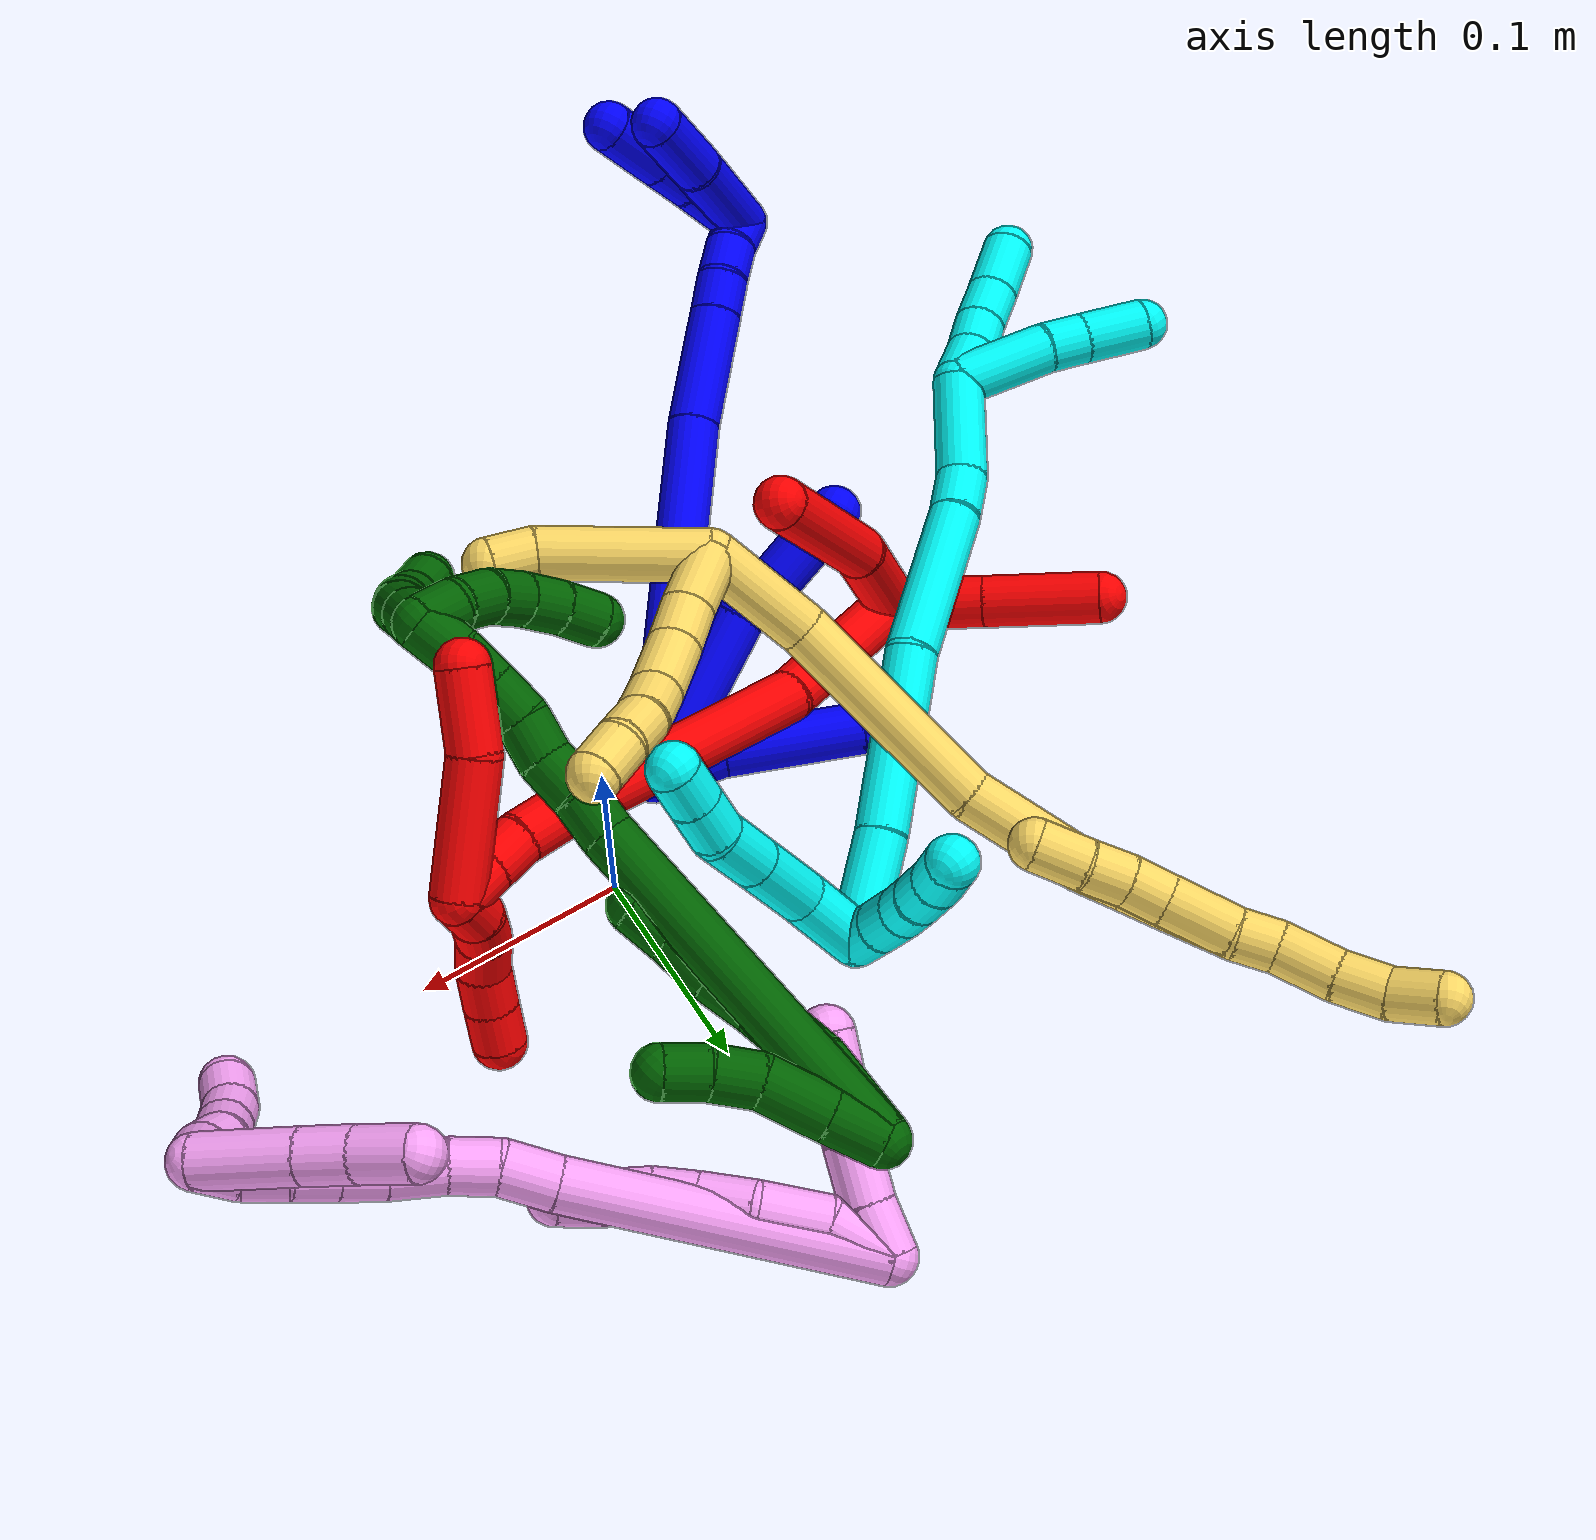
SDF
<sdf version="1.7">
 <world name="default">
  <plugin name="TubeGeneratorPlugin" filename="libtube_generator_plugin.so"/>
  <model name="photoneo_s_sensor">
   <static>1</static>
   <pose>0 0 2 1.57079 1.57079 3.14159</pose>
   <link name="link">
    <inertial><mass>0.1</mass></inertial>
    <sensor name="sensor" type="depth">
     <update_rate>30</update_rate>
     <camera>
      <horizontal_fov>1.22</horizontal_fov>
      <image><width>1920</width><height>1200</height><format>B8G8R8</format></image>
      <clip><near>0.1</near><far>4</far></clip>
      <depth_camera><output>points</output></depth_camera>
     </camera>
     <plugin name="camera_plugin" filename="libgazebo_ros_depth_camera.so">
      <baseline>0.2</baseline>
      <alwaysOn>1</alwaysOn>
      <updateRate>0.0</updateRate>
      <cameraName>camera_ir</cameraName>
      <imageTopicName>/camera/color/image_raw</imageTopicName>
      <cameraInfoTopicName>/camera/color/camera_info</cameraInfoTopicName>
      <depthImageTopicName>/camera/depth/image_raw</depthImageTopicName>
      <depthImageCameraInfoTopicName>/camera/depth/camera_info</depthImageCameraInfoTopicName>
      <pointCloudTopicName>/camera/depth/points</pointCloudTopicName>
      <frameName>fr_optical</frameName>
      <pointCloudCutoff>0.1</pointCloudCutoff>
      <pointCloudCutoffMax>2.0</pointCloudCutoffMax>
      <distortionK1>0</distortionK1>
      <distortionK2>0</distortionK2>
      <distortionK3>0</distortionK3>
      <distortionT1>0</distortionT1>
      <distortionT2>0</distortionT2>
      <CxPrime>0</CxPrime>
      <Cx>0</Cx>
      <Cy>0</Cy>
      <focalLength>0</focalLength>
      <hackBaseline>0</hackBaseline>
     </plugin>
    </sensor>
   </link>
  </model>
  <gravity>0 0 -9.8</gravity>
  <magnetic_field>6e-06 2.3e-05 -4.2e-05</magnetic_field>
  <atmosphere type="adiabatic"/>
  <physics name="default_physics" default="0" type="ode">
   <max_step_size>0.003</max_step_size>
   <real_time_factor>1</real_time_factor>
   <real_time_update_rate>1000</real_time_update_rate>
   <max_contacts>10000</max_contacts>
   <ode>
    <solver>
     <type>quick</type>
     <iters>100</iters>
     <sor>1.3</sor>
     <use_dynamic_moi_rescaling>0</use_dynamic_moi_rescaling>
    </solver>
    <constraints>
     <contact_max_correcting_vel>0</contact_max_correcting_vel>
     <contact_surface_layer>0.001</contact_surface_layer>
     <cfm>0</cfm>
     <erp>0.2</erp>
    </constraints>
   </ode>
  </physics>
  <scene><ambient>0.4 0.4 0.4 1</ambient><background>0.7 0.7 0.7 1</background><shadows>0</shadows></scene>
  <audio><device>default</device></audio>
  <spherical_coordinates>
   <surface_model>EARTH_WGS84</surface_model>
   <latitude_deg>0</latitude_deg>
   <longitude_deg>0</longitude_deg>
   <elevation>0</elevation>
   <heading_deg>0</heading_deg>
  </spherical_coordinates>
  <model name="bin">
   <static>1</static>
   <link name="bottom">
    <collision name="collision-bottom">
     <pose>0 0 -0.01 0 -0 0</pose>
     <geometry><box><size>0.8 0.6 0.02</size></box></geometry>
     <surface>
      <friction><ode><mu>100</mu><mu2>100</mu2></ode></friction>
      <contact><collide_bitmask>65535</collide_bitmask></contact>
     </surface>
    </collision>
   </link>
   <link name="west_wall">
    <collision name="collision-west_wall">
     <pose>-0.41 0 0.1 0 -0 0</pose>
     <geometry><box><size>0.02 0.6 0.2</size></box></geometry>
     <surface>
      <friction><ode><mu>100</mu><mu2>100</mu2></ode></friction>
      <contact><collide_bitmask>65535</collide_bitmask></contact>
     </surface>
    </collision>
   </link>
   <link name="east_wall">
    <collision name="collision-east_wall">
     <pose>0.41 0 0.1 0 -0 0</pose>
     <geometry><box><size>0.02 0.6 0.2</size></box></geometry>
     <surface>
      <friction><ode><mu>100</mu><mu2>100</mu2></ode></friction>
      <contact><collide_bitmask>65535</collide_bitmask></contact>
     </surface>
    </collision>
   </link>
   <link name="south_wall">
    <collision name="collision-south_wall">
     <pose>0 -0.31 0.1 0 -0 0</pose>
     <geometry><box><size>0.8 0.02 0.2</size></box></geometry>
     <surface>
      <friction><ode><mu>100</mu><mu2>100</mu2></ode></friction>
      <contact><collide_bitmask>65535</collide_bitmask></contact>
     </surface>
    </collision>
   </link>
   <link name="north_wall">
    <collision name="collision-north_wall">
     <pose>0 0.31 0.1 0 -0 0</pose>
     <geometry><box><size>0.8 0.02 0.2</size></box></geometry>
     <surface>
      <friction><ode><mu>100</mu><mu2>100</mu2></ode></friction>
      <contact><collide_bitmask>65535</collide_bitmask></contact>
     </surface>
    </collision>
   </link>
  </model>
  <model name="1">
   <static>0</static>
   <link name="1">
    <collision name="collision-cylinder-e_1_2_8">
     <pose>0.012233 -0.006646 0.039754 0.165645 0.294667 0.024638</pose>
     <geometry><cylinder><radius>0.0125</radius><length>0.084243</length></cylinder></geometry>
     <surface>
      <friction><ode><mu>1.16</mu><mu2>1.16</mu2><slip1>0</slip1><slip2>0</slip2></ode></friction>
      <contact><ode><kp>1e+06</kp><kd>1</kd><max_vel>0</max_vel><min_depth>0.001</min_depth></ode></contact>
     </surface>
    </collision>
    <visual name="visual-cylinder-e_1_2_8">
     <pose>0.012233 -0.006646 0.039754 0.165645 0.294667 0.024638</pose>
     <geometry><cylinder><radius>0.0125</radius><length>0.084243</length></cylinder></geometry>
     <material><ambient>0 0 1 1</ambient></material>
    </visual>
    <collision name="collision-cylinder-e_2_8_9">
     <pose>0.029155 -0.011856 0.090014 -0.13588 0.416326 -0.028743</pose>
     <geometry><cylinder><radius>0.0125</radius><length>0.023188</length></cylinder></geometry>
     <surface>
      <friction><ode><mu>1.16</mu><mu2>1.16</mu2><slip1>0</slip1><slip2>0</slip2></ode></friction>
      <contact><ode><kp>1e+06</kp><kd>1</kd><max_vel>0</max_vel><min_depth>0.001</min_depth></ode></contact>
     </surface>
    </collision>
    <visual name="visual-cylinder-e_2_8_9">
     <pose>0.029155 -0.011856 0.090014 -0.13588 0.416326 -0.028743</pose>
     <geometry><cylinder><radius>0.0125</radius><length>0.023188</length></cylinder></geometry>
     <material><ambient>0 0 1 1</ambient></material>
    </visual>
    <collision name="collision-cylinder-e_3_9_6">
     <pose>0.044313 -0.011082 0.11904 0.035797 0.514273 0.009414</pose>
     <geometry><cylinder><radius>0.0125</radius><length>0.042569</length></cylinder></geometry>
     <surface>
      <friction><ode><mu>1.16</mu><mu2>1.16</mu2><slip1>0</slip1><slip2>0</slip2></ode></friction>
      <contact><ode><kp>1e+06</kp><kd>1</kd><max_vel>0</max_vel><min_depth>0.001</min_depth></ode></contact>
     </surface>
    </collision>
    <visual name="visual-cylinder-e_3_9_6">
     <pose>0.044313 -0.011082 0.11904 0.035797 0.514273 0.009414</pose>
     <geometry><cylinder><radius>0.0125</radius><length>0.042569</length></cylinder></geometry>
     <material><ambient>0 0 1 1</ambient></material>
    </visual>
    <collision name="collision-cylinder-e_1_2_10">
     <pose>0.007656 0.008479 0.011892 -0.619407 0.482804 -0.157246</pose>
     <geometry><cylinder><radius>0.0125</radius><length>0.03298</length></cylinder></geometry>
     <surface>
      <friction><ode><mu>1.16</mu><mu2>1.16</mu2><slip1>0</slip1><slip2>0</slip2></ode></friction>
      <contact><ode><kp>1e+06</kp><kd>1</kd><max_vel>0</max_vel><min_depth>0.001</min_depth></ode></contact>
     </surface>
    </collision>
    <visual name="visual-cylinder-e_1_2_10">
     <pose>0.007656 0.008479 0.011892 -0.619407 0.482804 -0.157246</pose>
     <geometry><cylinder><radius>0.0125</radius><length>0.03298</length></cylinder></geometry>
     <material><ambient>0 0 1 1</ambient></material>
    </visual>
    <collision name="collision-cylinder-e_2_10_5">
     <pose>0.035173 0.036541 0.042356 -0.811864 0.634411 -0.28035</pose>
     <geometry><cylinder><radius>0.0125</radius><length>0.06702</length></cylinder></geometry>
     <surface>
      <friction><ode><mu>1.16</mu><mu2>1.16</mu2><slip1>0</slip1><slip2>0</slip2></ode></friction>
      <contact><ode><kp>1e+06</kp><kd>1</kd><max_vel>0</max_vel><min_depth>0.001</min_depth></ode></contact>
     </surface>
    </collision>
    <visual name="visual-cylinder-e_2_10_5">
     <pose>0.035173 0.036541 0.042356 -0.811864 0.634411 -0.28035</pose>
     <geometry><cylinder><radius>0.0125</radius><length>0.06702</length></cylinder></geometry>
     <material><ambient>0 0 1 1</ambient></material>
    </visual>
    <collision name="collision-cylinder-e_1_2_11">
     <pose>-0.018968 -0.020342 0.085897 0.232536 -0.211658 -0.024812</pose>
     <geometry><cylinder><radius>0.0125</radius><length>0.180576</length></cylinder></geometry>
     <surface>
      <friction><ode><mu>1.16</mu><mu2>1.16</mu2><slip1>0</slip1><slip2>0</slip2></ode></friction>
      <contact><ode><kp>1e+06</kp><kd>1</kd><max_vel>0</max_vel><min_depth>0.001</min_depth></ode></contact>
     </surface>
    </collision>
    <visual name="visual-cylinder-e_1_2_11">
     <pose>-0.018968 -0.020342 0.085897 0.232536 -0.211658 -0.024812</pose>
     <geometry><cylinder><radius>0.0125</radius><length>0.180576</length></cylinder></geometry>
     <material><ambient>0 0 1 1</ambient></material>
    </visual>
    <collision name="collision-cylinder-e_2_11_12">
     <pose>-0.042045 -0.046139 0.200549 0.187469 -0.139482 -0.013134</pose>
     <geometry><cylinder><radius>0.0125</radius><length>0.059108</length></cylinder></geometry>
     <surface>
      <friction><ode><mu>1.16</mu><mu2>1.16</mu2><slip1>0</slip1><slip2>0</slip2></ode></friction>
      <contact><ode><kp>1e+06</kp><kd>1</kd><max_vel>0</max_vel><min_depth>0.001</min_depth></ode></contact>
     </surface>
    </collision>
    <visual name="visual-cylinder-e_2_11_12">
     <pose>-0.042045 -0.046139 0.200549 0.187469 -0.139482 -0.013134</pose>
     <geometry><cylinder><radius>0.0125</radius><length>0.059108</length></cylinder></geometry>
     <material><ambient>0 0 1 1</ambient></material>
    </visual>
    <collision name="collision-cylinder-e_3_12_13">
     <pose>-0.047646 -0.053384 0.23907 0.181302 -0.149162 -0.013584</pose>
     <geometry><cylinder><radius>0.0125</radius><length>0.020082</length></cylinder></geometry>
     <surface>
      <friction><ode><mu>1.16</mu><mu2>1.16</mu2><slip1>0</slip1><slip2>0</slip2></ode></friction>
      <contact><ode><kp>1e+06</kp><kd>1</kd><max_vel>0</max_vel><min_depth>0.001</min_depth></ode></contact>
     </surface>
    </collision>
    <visual name="visual-cylinder-e_3_12_13">
     <pose>-0.047646 -0.053384 0.23907 0.181302 -0.149162 -0.013584</pose>
     <geometry><cylinder><radius>0.0125</radius><length>0.020082</length></cylinder></geometry>
     <material><ambient>0 0 1 1</ambient></material>
    </visual>
    <collision name="collision-cylinder-e_4_13_14">
     <pose>-0.051714 -0.055405 0.258543 0.023714 -0.259354 -0.003093</pose>
     <geometry><cylinder><radius>0.0125</radius><length>0.02009</length></cylinder></geometry>
     <surface>
      <friction><ode><mu>1.16</mu><mu2>1.16</mu2><slip1>0</slip1><slip2>0</slip2></ode></friction>
      <contact><ode><kp>1e+06</kp><kd>1</kd><max_vel>0</max_vel><min_depth>0.001</min_depth></ode></contact>
     </surface>
    </collision>
    <visual name="visual-cylinder-e_4_13_14">
     <pose>-0.051714 -0.055405 0.258543 0.023714 -0.259354 -0.003093</pose>
     <geometry><cylinder><radius>0.0125</radius><length>0.02009</length></cylinder></geometry>
     <material><ambient>0 0 1 1</ambient></material>
    </visual>
    <collision name="collision-cylinder-e_5_14_1">
     <pose>-0.05737 -0.053778 0.277657 -0.19483 -0.310809 0.030618</pose>
     <geometry><cylinder><radius>0.0125</radius><length>0.020143</length></cylinder></geometry>
     <surface>
      <friction><ode><mu>1.16</mu><mu2>1.16</mu2><slip1>0</slip1><slip2>0</slip2></ode></friction>
      <contact><ode><kp>1e+06</kp><kd>1</kd><max_vel>0</max_vel><min_depth>0.001</min_depth></ode></contact>
     </surface>
    </collision>
    <visual name="visual-cylinder-e_5_14_1">
     <pose>-0.05737 -0.053778 0.277657 -0.19483 -0.310809 0.030618</pose>
     <geometry><cylinder><radius>0.0125</radius><length>0.020143</length></cylinder></geometry>
     <material><ambient>0 0 1 1</ambient></material>
    </visual>
    <collision name="collision-cylinder-e_1_1_15">
     <pose>-0.048085 -0.079067 0.282079 1.75247 0.421225 0.50242</pose>
     <geometry><cylinder><radius>0.0125</radius><length>0.060486</length></cylinder></geometry>
     <surface>
      <friction><ode><mu>1.16</mu><mu2>1.16</mu2><slip1>0</slip1><slip2>0</slip2></ode></friction>
      <contact><ode><kp>1e+06</kp><kd>1</kd><max_vel>0</max_vel><min_depth>0.001</min_depth></ode></contact>
     </surface>
    </collision>
    <visual name="visual-cylinder-e_1_1_15">
     <pose>-0.048085 -0.079067 0.282079 1.75247 0.421225 0.50242</pose>
     <geometry><cylinder><radius>0.0125</radius><length>0.060486</length></cylinder></geometry>
     <material><ambient>0 0 1 1</ambient></material>
    </visual>
    <collision name="collision-cylinder-e_2_15_4">
     <pose>-0.030097 -0.12503 0.274936 1.68485 0.288556 0.322926</pose>
     <geometry><cylinder><radius>0.0125</radius><length>0.039514</length></cylinder></geometry>
     <surface>
      <friction><ode><mu>1.16</mu><mu2>1.16</mu2><slip1>0</slip1><slip2>0</slip2></ode></friction>
      <contact><ode><kp>1e+06</kp><kd>1</kd><max_vel>0</max_vel><min_depth>0.001</min_depth></ode></contact>
     </surface>
    </collision>
    <visual name="visual-cylinder-e_2_15_4">
     <pose>-0.030097 -0.12503 0.274936 1.68485 0.288556 0.322926</pose>
     <geometry><cylinder><radius>0.0125</radius><length>0.039514</length></cylinder></geometry>
     <material><ambient>0 0 1 1</ambient></material>
    </visual>
    <collision name="collision-cylinder-e_1_1_16">
     <pose>-0.056981 -0.073527 0.282757 1.76762 0.156202 0.190237</pose>
     <geometry><cylinder><radius>0.0125</radius><length>0.044603</length></cylinder></geometry>
     <surface>
      <friction><ode><mu>1.16</mu><mu2>1.16</mu2><slip1>0</slip1><slip2>0</slip2></ode></friction>
      <contact><ode><kp>1e+06</kp><kd>1</kd><max_vel>0</max_vel><min_depth>0.001</min_depth></ode></contact>
     </surface>
    </collision>
    <visual name="visual-cylinder-e_1_1_16">
     <pose>-0.056981 -0.073527 0.282757 1.76762 0.156202 0.190237</pose>
     <geometry><cylinder><radius>0.0125</radius><length>0.044603</length></cylinder></geometry>
     <material><ambient>0 0 1 1</ambient></material>
    </visual>
    <collision name="collision-cylinder-e_2_16_17">
     <pose>-0.053197 -0.105645 0.276756 1.73043 0.029514 0.034645</pose>
     <geometry><cylinder><radius>0.0125</radius><length>0.021308</length></cylinder></geometry>
     <surface>
      <friction><ode><mu>1.16</mu><mu2>1.16</mu2><slip1>0</slip1><slip2>0</slip2></ode></friction>
      <contact><ode><kp>1e+06</kp><kd>1</kd><max_vel>0</max_vel><min_depth>0.001</min_depth></ode></contact>
     </surface>
    </collision>
    <visual name="visual-cylinder-e_2_16_17">
     <pose>-0.053197 -0.105645 0.276756 1.73043 0.029514 0.034645</pose>
     <geometry><cylinder><radius>0.0125</radius><length>0.021308</length></cylinder></geometry>
     <material><ambient>0 0 1 1</ambient></material>
    </visual>
    <collision name="collision-cylinder-e_3_17_3">
     <pose>-0.05245 -0.133009 0.272534 1.71982 0.025424 0.029525</pose>
     <geometry><cylinder><radius>0.0125</radius><length>0.034089</length></cylinder></geometry>
     <surface>
      <friction><ode><mu>1.16</mu><mu2>1.16</mu2><slip1>0</slip1><slip2>0</slip2></ode></friction>
      <contact><ode><kp>1e+06</kp><kd>1</kd><max_vel>0</max_vel><min_depth>0.001</min_depth></ode></contact>
     </surface>
    </collision>
    <visual name="visual-cylinder-e_3_17_3">
     <pose>-0.05245 -0.133009 0.272534 1.71982 0.025424 0.029525</pose>
     <geometry><cylinder><radius>0.0125</radius><length>0.034089</length></cylinder></geometry>
     <material><ambient>0 0 1 1</ambient></material>
    </visual>
    <collision name="collision-sphere-3">
     <pose>-0.052016 -0.149859 0.270004 0 -0 0</pose>
     <geometry><sphere><radius>0.0125</radius></sphere></geometry>
     <surface>
      <friction><ode><mu>1.16</mu><mu2>1.16</mu2><slip1>0</slip1><slip2>0</slip2></ode></friction>
      <contact><ode><kp>1e+06</kp><kd>1</kd><max_vel>0</max_vel><min_depth>0.001</min_depth></ode></contact>
     </surface>
    </collision>
    <visual name="visual-sphere-3">
     <pose>-0.052016 -0.149859 0.270004 0 -0 0</pose>
     <geometry><sphere><radius>0.0125</radius></sphere></geometry>
     <material><ambient>0 0 1 1</ambient></material>
    </visual>
    <collision name="collision-sphere-17">
     <pose>-0.052883 -0.116159 0.275063 0 -0 0</pose>
     <geometry><sphere><radius>0.0125</radius></sphere></geometry>
     <surface>
      <friction><ode><mu>1.16</mu><mu2>1.16</mu2><slip1>0</slip1><slip2>0</slip2></ode></friction>
      <contact><ode><kp>1e+06</kp><kd>1</kd><max_vel>0</max_vel><min_depth>0.001</min_depth></ode></contact>
     </surface>
    </collision>
    <visual name="visual-sphere-17">
     <pose>-0.052883 -0.116159 0.275063 0 -0 0</pose>
     <geometry><sphere><radius>0.0125</radius></sphere></geometry>
     <material><ambient>0 0 1 1</ambient></material>
    </visual>
    <collision name="collision-sphere-16">
     <pose>-0.053512 -0.095131 0.278449 0 -0 0</pose>
     <geometry><sphere><radius>0.0125</radius></sphere></geometry>
     <surface>
      <friction><ode><mu>1.16</mu><mu2>1.16</mu2><slip1>0</slip1><slip2>0</slip2></ode></friction>
      <contact><ode><kp>1e+06</kp><kd>1</kd><max_vel>0</max_vel><min_depth>0.001</min_depth></ode></contact>
     </surface>
    </collision>
    <visual name="visual-sphere-16">
     <pose>-0.053512 -0.095131 0.278449 0 -0 0</pose>
     <geometry><sphere><radius>0.0125</radius></sphere></geometry>
     <material><ambient>0 0 1 1</ambient></material>
    </visual>
    <collision name="collision-sphere-4">
     <pose>-0.024475 -0.143847 0.272781 0 -0 0</pose>
     <geometry><sphere><radius>0.0125</radius></sphere></geometry>
     <surface>
      <friction><ode><mu>1.16</mu><mu2>1.16</mu2><slip1>0</slip1><slip2>0</slip2></ode></friction>
      <contact><ode><kp>1e+06</kp><kd>1</kd><max_vel>0</max_vel><min_depth>0.001</min_depth></ode></contact>
     </surface>
    </collision>
    <visual name="visual-sphere-4">
     <pose>-0.024475 -0.143847 0.272781 0 -0 0</pose>
     <geometry><sphere><radius>0.0125</radius></sphere></geometry>
     <material><ambient>0 0 1 1</ambient></material>
    </visual>
    <collision name="collision-sphere-15">
     <pose>-0.035719 -0.106213 0.277092 0 -0 0</pose>
     <geometry><sphere><radius>0.0125</radius></sphere></geometry>
     <surface>
      <friction><ode><mu>1.16</mu><mu2>1.16</mu2><slip1>0</slip1><slip2>0</slip2></ode></friction>
      <contact><ode><kp>1e+06</kp><kd>1</kd><max_vel>0</max_vel><min_depth>0.001</min_depth></ode></contact>
     </surface>
    </collision>
    <visual name="visual-sphere-15">
     <pose>-0.035719 -0.106213 0.277092 0 -0 0</pose>
     <geometry><sphere><radius>0.0125</radius></sphere></geometry>
     <material><ambient>0 0 1 1</ambient></material>
    </visual>
    <collision name="collision-sphere-1">
     <pose>-0.060451 -0.051922 0.287065 0 -0 0</pose>
     <geometry><sphere><radius>0.0125</radius></sphere></geometry>
     <surface>
      <friction><ode><mu>1.16</mu><mu2>1.16</mu2><slip1>0</slip1><slip2>0</slip2></ode></friction>
      <contact><ode><kp>1e+06</kp><kd>1</kd><max_vel>0</max_vel><min_depth>0.001</min_depth></ode></contact>
     </surface>
    </collision>
    <visual name="visual-sphere-1">
     <pose>-0.060451 -0.051922 0.287065 0 -0 0</pose>
     <geometry><sphere><radius>0.0125</radius></sphere></geometry>
     <material><ambient>0 0 1 1</ambient></material>
    </visual>
    <collision name="collision-sphere-14">
     <pose>-0.05429 -0.055635 0.26825 0 -0 0</pose>
     <geometry><sphere><radius>0.0125</radius></sphere></geometry>
     <surface>
      <friction><ode><mu>1.16</mu><mu2>1.16</mu2><slip1>0</slip1><slip2>0</slip2></ode></friction>
      <contact><ode><kp>1e+06</kp><kd>1</kd><max_vel>0</max_vel><min_depth>0.001</min_depth></ode></contact>
     </surface>
    </collision>
    <visual name="visual-sphere-14">
     <pose>-0.05429 -0.055635 0.26825 0 -0 0</pose>
     <geometry><sphere><radius>0.0125</radius></sphere></geometry>
     <material><ambient>0 0 1 1</ambient></material>
    </visual>
    <collision name="collision-sphere-13">
     <pose>-0.049138 -0.055174 0.248837 0 -0 0</pose>
     <geometry><sphere><radius>0.0125</radius></sphere></geometry>
     <surface>
      <friction><ode><mu>1.16</mu><mu2>1.16</mu2><slip1>0</slip1><slip2>0</slip2></ode></friction>
      <contact><ode><kp>1e+06</kp><kd>1</kd><max_vel>0</max_vel><min_depth>0.001</min_depth></ode></contact>
     </surface>
    </collision>
    <visual name="visual-sphere-13">
     <pose>-0.049138 -0.055174 0.248837 0 -0 0</pose>
     <geometry><sphere><radius>0.0125</radius></sphere></geometry>
     <material><ambient>0 0 1 1</ambient></material>
    </visual>
    <collision name="collision-sphere-12">
     <pose>-0.046153 -0.051594 0.229303 0 -0 0</pose>
     <geometry><sphere><radius>0.0125</radius></sphere></geometry>
     <surface>
      <friction><ode><mu>1.16</mu><mu2>1.16</mu2><slip1>0</slip1><slip2>0</slip2></ode></friction>
      <contact><ode><kp>1e+06</kp><kd>1</kd><max_vel>0</max_vel><min_depth>0.001</min_depth></ode></contact>
     </surface>
    </collision>
    <visual name="visual-sphere-12">
     <pose>-0.046153 -0.051594 0.229303 0 -0 0</pose>
     <geometry><sphere><radius>0.0125</radius></sphere></geometry>
     <material><ambient>0 0 1 1</ambient></material>
    </visual>
    <collision name="collision-sphere-11">
     <pose>-0.037936 -0.040684 0.171795 0 -0 0</pose>
     <geometry><sphere><radius>0.0125</radius></sphere></geometry>
     <surface>
      <friction><ode><mu>1.16</mu><mu2>1.16</mu2><slip1>0</slip1><slip2>0</slip2></ode></friction>
      <contact><ode><kp>1e+06</kp><kd>1</kd><max_vel>0</max_vel><min_depth>0.001</min_depth></ode></contact>
     </surface>
    </collision>
    <visual name="visual-sphere-11">
     <pose>-0.037936 -0.040684 0.171795 0 -0 0</pose>
     <geometry><sphere><radius>0.0125</radius></sphere></geometry>
     <material><ambient>0 0 1 1</ambient></material>
    </visual>
    <collision name="collision-sphere-8">
     <pose>0.024466 -0.013292 0.079508 0 -0 0</pose>
     <geometry><sphere><radius>0.0125</radius></sphere></geometry>
     <surface>
      <friction><ode><mu>1.16</mu><mu2>1.16</mu2><slip1>0</slip1><slip2>0</slip2></ode></friction>
      <contact><ode><kp>1e+06</kp><kd>1</kd><max_vel>0</max_vel><min_depth>0.001</min_depth></ode></contact>
     </surface>
    </collision>
    <visual name="visual-sphere-8">
     <pose>0.024466 -0.013292 0.079508 0 -0 0</pose>
     <geometry><sphere><radius>0.0125</radius></sphere></geometry>
     <material><ambient>0 0 1 1</ambient></material>
    </visual>
    <collision name="collision-sphere-2">
     <geometry><sphere><radius>0.0125</radius></sphere></geometry>
     <surface>
      <friction><ode><mu>1.16</mu><mu2>1.16</mu2><slip1>0</slip1><slip2>0</slip2></ode></friction>
      <contact><ode><kp>1e+06</kp><kd>1</kd><max_vel>0</max_vel><min_depth>0.001</min_depth></ode></contact>
     </surface>
    </collision>
    <visual name="visual-sphere-2">
     <geometry><sphere><radius>0.0125</radius></sphere></geometry>
     <material><ambient>0 0 1 1</ambient></material>
    </visual>
    <collision name="collision-sphere-9">
     <pose>0.033843 -0.010419 0.10052 0 -0 0</pose>
     <geometry><sphere><radius>0.0125</radius></sphere></geometry>
     <surface>
      <friction><ode><mu>1.16</mu><mu2>1.16</mu2><slip1>0</slip1><slip2>0</slip2></ode></friction>
      <contact><ode><kp>1e+06</kp><kd>1</kd><max_vel>0</max_vel><min_depth>0.001</min_depth></ode></contact>
     </surface>
    </collision>
    <visual name="visual-sphere-9">
     <pose>0.033843 -0.010419 0.10052 0 -0 0</pose>
     <geometry><sphere><radius>0.0125</radius></sphere></geometry>
     <material><ambient>0 0 1 1</ambient></material>
    </visual>
    <collision name="collision-sphere-6">
     <pose>0.054783 -0.011746 0.137559 0 -0 0</pose>
     <geometry><sphere><radius>0.0125</radius></sphere></geometry>
     <surface>
      <friction><ode><mu>1.16</mu><mu2>1.16</mu2><slip1>0</slip1><slip2>0</slip2></ode></friction>
      <contact><ode><kp>1e+06</kp><kd>1</kd><max_vel>0</max_vel><min_depth>0.001</min_depth></ode></contact>
     </surface>
    </collision>
    <visual name="visual-sphere-6">
     <pose>0.054783 -0.011746 0.137559 0 -0 0</pose>
     <geometry><sphere><radius>0.0125</radius></sphere></geometry>
     <material><ambient>0 0 1 1</ambient></material>
    </visual>
    <collision name="collision-sphere-10">
     <pose>0.015311 0.016958 0.023783 0 -0 0</pose>
     <geometry><sphere><radius>0.0125</radius></sphere></geometry>
     <surface>
      <friction><ode><mu>1.16</mu><mu2>1.16</mu2><slip1>0</slip1><slip2>0</slip2></ode></friction>
      <contact><ode><kp>1e+06</kp><kd>1</kd><max_vel>0</max_vel><min_depth>0.001</min_depth></ode></contact>
     </surface>
    </collision>
    <visual name="visual-sphere-10">
     <pose>0.015311 0.016958 0.023783 0 -0 0</pose>
     <geometry><sphere><radius>0.0125</radius></sphere></geometry>
     <material><ambient>0 0 1 1</ambient></material>
    </visual>
    <collision name="collision-sphere-5">
     <pose>0.055034 0.056124 0.060929 0 -0 0</pose>
     <geometry><sphere><radius>0.0125</radius></sphere></geometry>
     <surface>
      <friction><ode><mu>1.16</mu><mu2>1.16</mu2><slip1>0</slip1><slip2>0</slip2></ode></friction>
      <contact><ode><kp>1e+06</kp><kd>1</kd><max_vel>0</max_vel><min_depth>0.001</min_depth></ode></contact>
     </surface>
    </collision>
    <visual name="visual-sphere-5">
     <pose>0.055034 0.056124 0.060929 0 -0 0</pose>
     <geometry><sphere><radius>0.0125</radius></sphere></geometry>
     <material><ambient>0 0 1 1</ambient></material>
    </visual>
    <inertial>
     <pose>-0.01656 -0.037379 0.149884 0 -0 0</pose>
     <mass>0.75</mass>
     <inertia>
      <ixx>0.000635</ixx>
      <ixy>0</ixy>
      <ixz>0</ixz>
      <iyy>0.000574</iyy>
      <iyz>0</iyz>
      <izz>0.000239</izz>
     </inertia>
    </inertial>
   </link>
   <pose>-0.042941 -0.034523 0.012499 -1.36801 -0.659152 2.05088</pose>
  </model>
  <model name="2">
   <static>0</static>
   <link name="2">
    <collision name="collision-cylinder-e_1_2_8">
     <pose>0.021486 -0.024556 0.016529 0.978353 0.627865 0.342282</pose>
     <geometry><cylinder><radius>0.0125</radius><length>0.073152</length></cylinder></geometry>
     <surface>
      <friction><ode><mu>1.16</mu><mu2>1.16</mu2><slip1>0</slip1><slip2>0</slip2></ode></friction>
      <contact><ode><kp>1e+06</kp><kd>1</kd><max_vel>0</max_vel><min_depth>0.001</min_depth></ode></contact>
     </surface>
    </collision>
    <visual name="visual-cylinder-e_1_2_8">
     <pose>0.021486 -0.024556 0.016529 0.978353 0.627865 0.342282</pose>
     <geometry><cylinder><radius>0.0125</radius><length>0.073152</length></cylinder></geometry>
     <material><ambient>1 0 0 1</ambient></material>
    </visual>
    <collision name="collision-cylinder-e_2_8_6">
     <pose>0.069204 -0.075721 0.042009 1.24627 0.751496 0.552504</pose>
     <geometry><cylinder><radius>0.0125</radius><length>0.076848</length></cylinder></geometry>
     <surface>
      <friction><ode><mu>1.16</mu><mu2>1.16</mu2><slip1>0</slip1><slip2>0</slip2></ode></friction>
      <contact><ode><kp>1e+06</kp><kd>1</kd><max_vel>0</max_vel><min_depth>0.001</min_depth></ode></contact>
     </surface>
    </collision>
    <visual name="visual-cylinder-e_2_8_6">
     <pose>0.069204 -0.075721 0.042009 1.24627 0.751496 0.552504</pose>
     <geometry><cylinder><radius>0.0125</radius><length>0.076848</length></cylinder></geometry>
     <material><ambient>1 0 0 1</ambient></material>
    </visual>
    <collision name="collision-cylinder-e_1_2_9">
     <pose>-0.008827 0.007532 0.018691 -0.383097 -0.412848 0.081174</pose>
     <geometry><cylinder><radius>0.0125</radius><length>0.044</length></cylinder></geometry>
     <surface>
      <friction><ode><mu>1.16</mu><mu2>1.16</mu2><slip1>0</slip1><slip2>0</slip2></ode></friction>
      <contact><ode><kp>1e+06</kp><kd>1</kd><max_vel>0</max_vel><min_depth>0.001</min_depth></ode></contact>
     </surface>
    </collision>
    <visual name="visual-cylinder-e_1_2_9">
     <pose>-0.008827 0.007532 0.018691 -0.383097 -0.412848 0.081174</pose>
     <geometry><cylinder><radius>0.0125</radius><length>0.044</length></cylinder></geometry>
     <material><ambient>1 0 0 1</ambient></material>
    </visual>
    <collision name="collision-cylinder-e_2_9_5">
     <pose>-0.028693 0.024317 0.061393 -0.367797 -0.405259 0.07639</pose>
     <geometry><cylinder><radius>0.0125</radius><length>0.056</length></cylinder></geometry>
     <surface>
      <friction><ode><mu>1.16</mu><mu2>1.16</mu2><slip1>0</slip1><slip2>0</slip2></ode></friction>
      <contact><ode><kp>1e+06</kp><kd>1</kd><max_vel>0</max_vel><min_depth>0.001</min_depth></ode></contact>
     </surface>
    </collision>
    <visual name="visual-cylinder-e_2_9_5">
     <pose>-0.028693 0.024317 0.061393 -0.367797 -0.405259 0.07639</pose>
     <geometry><cylinder><radius>0.0125</radius><length>0.056</length></cylinder></geometry>
     <material><ambient>1 0 0 1</ambient></material>
    </visual>
    <collision name="collision-cylinder-e_1_2_10">
     <pose>0.045203 -0.00253 -0.001272 2.03662 1.50824 1.97993</pose>
     <geometry><cylinder><radius>0.0125</radius><length>0.090582</length></cylinder></geometry>
     <surface>
      <friction><ode><mu>1.16</mu><mu2>1.16</mu2><slip1>0</slip1><slip2>0</slip2></ode></friction>
      <contact><ode><kp>1e+06</kp><kd>1</kd><max_vel>0</max_vel><min_depth>0.001</min_depth></ode></contact>
     </surface>
    </collision>
    <visual name="visual-cylinder-e_1_2_10">
     <pose>0.045203 -0.00253 -0.001272 2.03662 1.50824 1.97993</pose>
     <geometry><cylinder><radius>0.0125</radius><length>0.090582</length></cylinder></geometry>
     <material><ambient>1 0 0 1</ambient></material>
    </visual>
    <collision name="collision-cylinder-e_2_10_11">
     <pose>0.160968 -0.020635 -0.012962 2.16036 1.31122 1.92747</pose>
     <geometry><cylinder><radius>0.0125</radius><length>0.146017</length></cylinder></geometry>
     <surface>
      <friction><ode><mu>1.16</mu><mu2>1.16</mu2><slip1>0</slip1><slip2>0</slip2></ode></friction>
      <contact><ode><kp>1e+06</kp><kd>1</kd><max_vel>0</max_vel><min_depth>0.001</min_depth></ode></contact>
     </surface>
    </collision>
    <visual name="visual-cylinder-e_2_10_11">
     <pose>0.160968 -0.020635 -0.012962 2.16036 1.31122 1.92747</pose>
     <geometry><cylinder><radius>0.0125</radius><length>0.146017</length></cylinder></geometry>
     <material><ambient>1 0 0 1</ambient></material>
    </visual>
    <collision name="collision-cylinder-e_3_11_12">
     <pose>0.242256 -0.037314 -0.026425 2.79369 1.2776 2.67691</pose>
     <geometry><cylinder><radius>0.0125</radius><length>0.022407</length></cylinder></geometry>
     <surface>
      <friction><ode><mu>1.16</mu><mu2>1.16</mu2><slip1>0</slip1><slip2>0</slip2></ode></friction>
      <contact><ode><kp>1e+06</kp><kd>1</kd><max_vel>0</max_vel><min_depth>0.001</min_depth></ode></contact>
     </surface>
    </collision>
    <visual name="visual-cylinder-e_3_11_12">
     <pose>0.242256 -0.037314 -0.026425 2.79369 1.2776 2.67691</pose>
     <geometry><cylinder><radius>0.0125</radius><length>0.022407</length></cylinder></geometry>
     <material><ambient>1 0 0 1</ambient></material>
    </visual>
    <collision name="collision-cylinder-e_4_12_13">
     <pose>0.263027 -0.037627 -0.031686 -2.79862 1.34062 -2.71143</pose>
     <geometry><cylinder><radius>0.0125</radius><length>0.020636</length></cylinder></geometry>
     <surface>
      <friction><ode><mu>1.16</mu><mu2>1.16</mu2><slip1>0</slip1><slip2>0</slip2></ode></friction>
      <contact><ode><kp>1e+06</kp><kd>1</kd><max_vel>0</max_vel><min_depth>0.001</min_depth></ode></contact>
     </surface>
    </collision>
    <visual name="visual-cylinder-e_4_12_13">
     <pose>0.263027 -0.037627 -0.031686 -2.79862 1.34062 -2.71143</pose>
     <geometry><cylinder><radius>0.0125</radius><length>0.020636</length></cylinder></geometry>
     <material><ambient>1 0 0 1</ambient></material>
    </visual>
    <collision name="collision-cylinder-e_5_13_1">
     <pose>0.283178 -0.036322 -0.035018 -2.71023 1.44992 -2.6567</pose>
     <geometry><cylinder><radius>0.0125</radius><length>0.020358</length></cylinder></geometry>
     <surface>
      <friction><ode><mu>1.16</mu><mu2>1.16</mu2><slip1>0</slip1><slip2>0</slip2></ode></friction>
      <contact><ode><kp>1e+06</kp><kd>1</kd><max_vel>0</max_vel><min_depth>0.001</min_depth></ode></contact>
     </surface>
    </collision>
    <visual name="visual-cylinder-e_5_13_1">
     <pose>0.283178 -0.036322 -0.035018 -2.71023 1.44992 -2.6567</pose>
     <geometry><cylinder><radius>0.0125</radius><length>0.020358</length></cylinder></geometry>
     <material><ambient>1 0 0 1</ambient></material>
    </visual>
    <collision name="collision-cylinder-e_1_1_14">
     <pose>0.277856 -0.061169 -0.026887 1.22118 -0.519197 -0.367527</pose>
     <geometry><cylinder><radius>0.0125</radius><length>0.06218</length></cylinder></geometry>
     <surface>
      <friction><ode><mu>1.16</mu><mu2>1.16</mu2><slip1>0</slip1><slip2>0</slip2></ode></friction>
      <contact><ode><kp>1e+06</kp><kd>1</kd><max_vel>0</max_vel><min_depth>0.001</min_depth></ode></contact>
     </surface>
    </collision>
    <visual name="visual-cylinder-e_1_1_14">
     <pose>0.277856 -0.061169 -0.026887 1.22118 -0.519197 -0.367527</pose>
     <geometry><cylinder><radius>0.0125</radius><length>0.06218</length></cylinder></geometry>
     <material><ambient>1 0 0 1</ambient></material>
    </visual>
    <collision name="collision-cylinder-e_2_14_4">
     <pose>0.25454 -0.103678 -0.016528 1.50602 -0.430384 -0.404125</pose>
     <geometry><cylinder><radius>0.0125</radius><length>0.03782</length></cylinder></geometry>
     <surface>
      <friction><ode><mu>1.16</mu><mu2>1.16</mu2><slip1>0</slip1><slip2>0</slip2></ode></friction>
      <contact><ode><kp>1e+06</kp><kd>1</kd><max_vel>0</max_vel><min_depth>0.001</min_depth></ode></contact>
     </surface>
    </collision>
    <visual name="visual-cylinder-e_2_14_4">
     <pose>0.25454 -0.103678 -0.016528 1.50602 -0.430384 -0.404125</pose>
     <geometry><cylinder><radius>0.0125</radius><length>0.03782</length></cylinder></geometry>
     <material><ambient>1 0 0 1</ambient></material>
    </visual>
    <collision name="collision-cylinder-e_1_1_15">
     <pose>0.288208 -0.027941 -0.039646 -1.99077 -0.532225 0.795659</pose>
     <geometry><cylinder><radius>0.0125</radius><length>0.02</length></cylinder></geometry>
     <surface>
      <friction><ode><mu>1.16</mu><mu2>1.16</mu2><slip1>0</slip1><slip2>0</slip2></ode></friction>
      <contact><ode><kp>1e+06</kp><kd>1</kd><max_vel>0</max_vel><min_depth>0.001</min_depth></ode></contact>
     </surface>
    </collision>
    <visual name="visual-cylinder-e_1_1_15">
     <pose>0.288208 -0.027941 -0.039646 -1.99077 -0.532225 0.795659</pose>
     <geometry><cylinder><radius>0.0125</radius><length>0.02</length></cylinder></geometry>
     <material><ambient>1 0 0 1</ambient></material>
    </visual>
    <collision name="collision-cylinder-e_2_15_16">
     <pose>0.279661 -0.012607 -0.048835 -2.22082 -0.35461 0.69344</pose>
     <geometry><cylinder><radius>0.0125</radius><length>0.02</length></cylinder></geometry>
     <surface>
      <friction><ode><mu>1.16</mu><mu2>1.16</mu2><slip1>0</slip1><slip2>0</slip2></ode></friction>
      <contact><ode><kp>1e+06</kp><kd>1</kd><max_vel>0</max_vel><min_depth>0.001</min_depth></ode></contact>
     </surface>
    </collision>
    <visual name="visual-cylinder-e_2_15_16">
     <pose>0.279661 -0.012607 -0.048835 -2.22082 -0.35461 0.69344</pose>
     <geometry><cylinder><radius>0.0125</radius><length>0.02</length></cylinder></geometry>
     <material><ambient>1 0 0 1</ambient></material>
    </visual>
    <collision name="collision-cylinder-e_3_16_17">
     <pose>0.275786 0.002991 -0.060316 -2.19077 -0.040316 0.078285</pose>
     <geometry><cylinder><radius>0.0125</radius><length>0.02</length></cylinder></geometry>
     <surface>
      <friction><ode><mu>1.16</mu><mu2>1.16</mu2><slip1>0</slip1><slip2>0</slip2></ode></friction>
      <contact><ode><kp>1e+06</kp><kd>1</kd><max_vel>0</max_vel><min_depth>0.001</min_depth></ode></contact>
     </surface>
    </collision>
    <visual name="visual-cylinder-e_3_16_17">
     <pose>0.275786 0.002991 -0.060316 -2.19077 -0.040316 0.078285</pose>
     <geometry><cylinder><radius>0.0125</radius><length>0.02</length></cylinder></geometry>
     <material><ambient>1 0 0 1</ambient></material>
    </visual>
    <collision name="collision-cylinder-e_4_17_18">
     <pose>0.275836 0.020545 -0.069441 -1.90951 0.045333 -0.064023</pose>
     <geometry><cylinder><radius>0.0125</radius><length>0.02</length></cylinder></geometry>
     <surface>
      <friction><ode><mu>1.16</mu><mu2>1.16</mu2><slip1>0</slip1><slip2>0</slip2></ode></friction>
      <contact><ode><kp>1e+06</kp><kd>1</kd><max_vel>0</max_vel><min_depth>0.001</min_depth></ode></contact>
     </surface>
    </collision>
    <visual name="visual-cylinder-e_4_17_18">
     <pose>0.275836 0.020545 -0.069441 -1.90951 0.045333 -0.064023</pose>
     <geometry><cylinder><radius>0.0125</radius><length>0.02</length></cylinder></geometry>
     <material><ambient>1 0 0 1</ambient></material>
    </visual>
    <collision name="collision-cylinder-e_5_18_3">
     <pose>0.277162 0.039539 -0.075521 -1.8516 0.087446 -0.116176</pose>
     <geometry><cylinder><radius>0.0125</radius><length>0.02</length></cylinder></geometry>
     <surface>
      <friction><ode><mu>1.16</mu><mu2>1.16</mu2><slip1>0</slip1><slip2>0</slip2></ode></friction>
      <contact><ode><kp>1e+06</kp><kd>1</kd><max_vel>0</max_vel><min_depth>0.001</min_depth></ode></contact>
     </surface>
    </collision>
    <visual name="visual-cylinder-e_5_18_3">
     <pose>0.277162 0.039539 -0.075521 -1.8516 0.087446 -0.116176</pose>
     <geometry><cylinder><radius>0.0125</radius><length>0.02</length></cylinder></geometry>
     <material><ambient>1 0 0 1</ambient></material>
    </visual>
    <collision name="collision-sphere-3">
     <pose>0.278036 0.04911 -0.078282 0 -0 0</pose>
     <geometry><sphere><radius>0.0125</radius></sphere></geometry>
     <surface>
      <friction><ode><mu>1.16</mu><mu2>1.16</mu2><slip1>0</slip1><slip2>0</slip2></ode></friction>
      <contact><ode><kp>1e+06</kp><kd>1</kd><max_vel>0</max_vel><min_depth>0.001</min_depth></ode></contact>
     </surface>
    </collision>
    <visual name="visual-sphere-3">
     <pose>0.278036 0.04911 -0.078282 0 -0 0</pose>
     <geometry><sphere><radius>0.0125</radius></sphere></geometry>
     <material><ambient>1 0 0 1</ambient></material>
    </visual>
    <collision name="collision-sphere-10">
     <pose>0.090405 -0.005059 -0.002543 0 -0 0</pose>
     <geometry><sphere><radius>0.0125</radius></sphere></geometry>
     <surface>
      <friction><ode><mu>1.16</mu><mu2>1.16</mu2><slip1>0</slip1><slip2>0</slip2></ode></friction>
      <contact><ode><kp>1e+06</kp><kd>1</kd><max_vel>0</max_vel><min_depth>0.001</min_depth></ode></contact>
     </surface>
    </collision>
    <visual name="visual-sphere-10">
     <pose>0.090405 -0.005059 -0.002543 0 -0 0</pose>
     <geometry><sphere><radius>0.0125</radius></sphere></geometry>
     <material><ambient>1 0 0 1</ambient></material>
    </visual>
    <collision name="collision-sphere-5">
     <pose>-0.039732 0.03357 0.085404 0 -0 0</pose>
     <geometry><sphere><radius>0.0125</radius></sphere></geometry>
     <surface>
      <friction><ode><mu>1.16</mu><mu2>1.16</mu2><slip1>0</slip1><slip2>0</slip2></ode></friction>
      <contact><ode><kp>1e+06</kp><kd>1</kd><max_vel>0</max_vel><min_depth>0.001</min_depth></ode></contact>
     </surface>
    </collision>
    <visual name="visual-sphere-5">
     <pose>-0.039732 0.03357 0.085404 0 -0 0</pose>
     <geometry><sphere><radius>0.0125</radius></sphere></geometry>
     <material><ambient>1 0 0 1</ambient></material>
    </visual>
    <collision name="collision-sphere-6">
     <pose>0.095437 -0.102331 0.050961 0 -0 0</pose>
     <geometry><sphere><radius>0.0125</radius></sphere></geometry>
     <surface>
      <friction><ode><mu>1.16</mu><mu2>1.16</mu2><slip1>0</slip1><slip2>0</slip2></ode></friction>
      <contact><ode><kp>1e+06</kp><kd>1</kd><max_vel>0</max_vel><min_depth>0.001</min_depth></ode></contact>
     </surface>
    </collision>
    <visual name="visual-sphere-6">
     <pose>0.095437 -0.102331 0.050961 0 -0 0</pose>
     <geometry><sphere><radius>0.0125</radius></sphere></geometry>
     <material><ambient>1 0 0 1</ambient></material>
    </visual>
    <collision name="collision-sphere-9">
     <pose>-0.017654 0.015065 0.037381 0 -0 0</pose>
     <geometry><sphere><radius>0.0125</radius></sphere></geometry>
     <surface>
      <friction><ode><mu>1.16</mu><mu2>1.16</mu2><slip1>0</slip1><slip2>0</slip2></ode></friction>
      <contact><ode><kp>1e+06</kp><kd>1</kd><max_vel>0</max_vel><min_depth>0.001</min_depth></ode></contact>
     </surface>
    </collision>
    <visual name="visual-sphere-9">
     <pose>-0.017654 0.015065 0.037381 0 -0 0</pose>
     <geometry><sphere><radius>0.0125</radius></sphere></geometry>
     <material><ambient>1 0 0 1</ambient></material>
    </visual>
    <collision name="collision-sphere-2">
     <geometry><sphere><radius>0.0125</radius></sphere></geometry>
     <surface>
      <friction><ode><mu>1.16</mu><mu2>1.16</mu2><slip1>0</slip1><slip2>0</slip2></ode></friction>
      <contact><ode><kp>1e+06</kp><kd>1</kd><max_vel>0</max_vel><min_depth>0.001</min_depth></ode></contact>
     </surface>
    </collision>
    <visual name="visual-sphere-2">
     <geometry><sphere><radius>0.0125</radius></sphere></geometry>
     <material><ambient>1 0 0 1</ambient></material>
    </visual>
    <collision name="collision-sphere-8">
     <pose>0.042971 -0.049112 0.033057 0 -0 0</pose>
     <geometry><sphere><radius>0.0125</radius></sphere></geometry>
     <surface>
      <friction><ode><mu>1.16</mu><mu2>1.16</mu2><slip1>0</slip1><slip2>0</slip2></ode></friction>
      <contact><ode><kp>1e+06</kp><kd>1</kd><max_vel>0</max_vel><min_depth>0.001</min_depth></ode></contact>
     </surface>
    </collision>
    <visual name="visual-sphere-8">
     <pose>0.042971 -0.049112 0.033057 0 -0 0</pose>
     <geometry><sphere><radius>0.0125</radius></sphere></geometry>
     <material><ambient>1 0 0 1</ambient></material>
    </visual>
    <collision name="collision-sphere-11">
     <pose>0.23153 -0.03621 -0.023381 0 -0 0</pose>
     <geometry><sphere><radius>0.0125</radius></sphere></geometry>
     <surface>
      <friction><ode><mu>1.16</mu><mu2>1.16</mu2><slip1>0</slip1><slip2>0</slip2></ode></friction>
      <contact><ode><kp>1e+06</kp><kd>1</kd><max_vel>0</max_vel><min_depth>0.001</min_depth></ode></contact>
     </surface>
    </collision>
    <visual name="visual-sphere-11">
     <pose>0.23153 -0.03621 -0.023381 0 -0 0</pose>
     <geometry><sphere><radius>0.0125</radius></sphere></geometry>
     <material><ambient>1 0 0 1</ambient></material>
    </visual>
    <collision name="collision-sphere-12">
     <pose>0.252981 -0.038418 -0.029469 0 -0 0</pose>
     <geometry><sphere><radius>0.0125</radius></sphere></geometry>
     <surface>
      <friction><ode><mu>1.16</mu><mu2>1.16</mu2><slip1>0</slip1><slip2>0</slip2></ode></friction>
      <contact><ode><kp>1e+06</kp><kd>1</kd><max_vel>0</max_vel><min_depth>0.001</min_depth></ode></contact>
     </surface>
    </collision>
    <visual name="visual-sphere-12">
     <pose>0.252981 -0.038418 -0.029469 0 -0 0</pose>
     <geometry><sphere><radius>0.0125</radius></sphere></geometry>
     <material><ambient>1 0 0 1</ambient></material>
    </visual>
    <collision name="collision-sphere-13">
     <pose>0.273073 -0.036835 -0.033903 0 -0 0</pose>
     <geometry><sphere><radius>0.0125</radius></sphere></geometry>
     <surface>
      <friction><ode><mu>1.16</mu><mu2>1.16</mu2><slip1>0</slip1><slip2>0</slip2></ode></friction>
      <contact><ode><kp>1e+06</kp><kd>1</kd><max_vel>0</max_vel><min_depth>0.001</min_depth></ode></contact>
     </surface>
    </collision>
    <visual name="visual-sphere-13">
     <pose>0.273073 -0.036835 -0.033903 0 -0 0</pose>
     <geometry><sphere><radius>0.0125</radius></sphere></geometry>
     <material><ambient>1 0 0 1</ambient></material>
    </visual>
    <collision name="collision-sphere-1">
     <pose>0.293282 -0.035809 -0.036133 0 -0 0</pose>
     <geometry><sphere><radius>0.0125</radius></sphere></geometry>
     <surface>
      <friction><ode><mu>1.16</mu><mu2>1.16</mu2><slip1>0</slip1><slip2>0</slip2></ode></friction>
      <contact><ode><kp>1e+06</kp><kd>1</kd><max_vel>0</max_vel><min_depth>0.001</min_depth></ode></contact>
     </surface>
    </collision>
    <visual name="visual-sphere-1">
     <pose>0.293282 -0.035809 -0.036133 0 -0 0</pose>
     <geometry><sphere><radius>0.0125</radius></sphere></geometry>
     <material><ambient>1 0 0 1</ambient></material>
    </visual>
    <collision name="collision-sphere-18">
     <pose>0.276289 0.029967 -0.07276 0 -0 0</pose>
     <geometry><sphere><radius>0.0125</radius></sphere></geometry>
     <surface>
      <friction><ode><mu>1.16</mu><mu2>1.16</mu2><slip1>0</slip1><slip2>0</slip2></ode></friction>
      <contact><ode><kp>1e+06</kp><kd>1</kd><max_vel>0</max_vel><min_depth>0.001</min_depth></ode></contact>
     </surface>
    </collision>
    <visual name="visual-sphere-18">
     <pose>0.276289 0.029967 -0.07276 0 -0 0</pose>
     <geometry><sphere><radius>0.0125</radius></sphere></geometry>
     <material><ambient>1 0 0 1</ambient></material>
    </visual>
    <collision name="collision-sphere-14">
     <pose>0.262429 -0.086529 -0.017641 0 -0 0</pose>
     <geometry><sphere><radius>0.0125</radius></sphere></geometry>
     <surface>
      <friction><ode><mu>1.16</mu><mu2>1.16</mu2><slip1>0</slip1><slip2>0</slip2></ode></friction>
      <contact><ode><kp>1e+06</kp><kd>1</kd><max_vel>0</max_vel><min_depth>0.001</min_depth></ode></contact>
     </surface>
    </collision>
    <visual name="visual-sphere-14">
     <pose>0.262429 -0.086529 -0.017641 0 -0 0</pose>
     <geometry><sphere><radius>0.0125</radius></sphere></geometry>
     <material><ambient>1 0 0 1</ambient></material>
    </visual>
    <collision name="collision-sphere-4">
     <pose>0.24665 -0.120827 -0.015416 0 -0 0</pose>
     <geometry><sphere><radius>0.0125</radius></sphere></geometry>
     <surface>
      <friction><ode><mu>1.16</mu><mu2>1.16</mu2><slip1>0</slip1><slip2>0</slip2></ode></friction>
      <contact><ode><kp>1e+06</kp><kd>1</kd><max_vel>0</max_vel><min_depth>0.001</min_depth></ode></contact>
     </surface>
    </collision>
    <visual name="visual-sphere-4">
     <pose>0.24665 -0.120827 -0.015416 0 -0 0</pose>
     <geometry><sphere><radius>0.0125</radius></sphere></geometry>
     <material><ambient>1 0 0 1</ambient></material>
    </visual>
    <collision name="collision-sphere-15">
     <pose>0.283133 -0.020073 -0.04316 0 -0 0</pose>
     <geometry><sphere><radius>0.0125</radius></sphere></geometry>
     <surface>
      <friction><ode><mu>1.16</mu><mu2>1.16</mu2><slip1>0</slip1><slip2>0</slip2></ode></friction>
      <contact><ode><kp>1e+06</kp><kd>1</kd><max_vel>0</max_vel><min_depth>0.001</min_depth></ode></contact>
     </surface>
    </collision>
    <visual name="visual-sphere-15">
     <pose>0.283133 -0.020073 -0.04316 0 -0 0</pose>
     <geometry><sphere><radius>0.0125</radius></sphere></geometry>
     <material><ambient>1 0 0 1</ambient></material>
    </visual>
    <collision name="collision-sphere-16">
     <pose>0.276189 -0.005142 -0.054511 0 -0 0</pose>
     <geometry><sphere><radius>0.0125</radius></sphere></geometry>
     <surface>
      <friction><ode><mu>1.16</mu><mu2>1.16</mu2><slip1>0</slip1><slip2>0</slip2></ode></friction>
      <contact><ode><kp>1e+06</kp><kd>1</kd><max_vel>0</max_vel><min_depth>0.001</min_depth></ode></contact>
     </surface>
    </collision>
    <visual name="visual-sphere-16">
     <pose>0.276189 -0.005142 -0.054511 0 -0 0</pose>
     <geometry><sphere><radius>0.0125</radius></sphere></geometry>
     <material><ambient>1 0 0 1</ambient></material>
    </visual>
    <collision name="collision-sphere-17">
     <pose>0.275382 0.011123 -0.066122 0 -0 0</pose>
     <geometry><sphere><radius>0.0125</radius></sphere></geometry>
     <surface>
      <friction><ode><mu>1.16</mu><mu2>1.16</mu2><slip1>0</slip1><slip2>0</slip2></ode></friction>
      <contact><ode><kp>1e+06</kp><kd>1</kd><max_vel>0</max_vel><min_depth>0.001</min_depth></ode></contact>
     </surface>
    </collision>
    <visual name="visual-sphere-17">
     <pose>0.275382 0.011123 -0.066122 0 -0 0</pose>
     <geometry><sphere><radius>0.0125</radius></sphere></geometry>
     <material><ambient>1 0 0 1</ambient></material>
    </visual>
    <inertial>
     <pose>0.138601 -0.025054 -0.004588 0 -0 0</pose>
     <mass>0.75</mass>
     <inertia>
      <ixx>0.000189</ixx>
      <ixy>0</ixy>
      <ixz>0</ixz>
      <iyy>0.000484</iyy>
      <iyz>0</iyz>
      <izz>-0.000223</izz>
     </inertia>
    </inertial>
   </link>
   <pose>-0.188773 -0.056805 0.011485 -0.885746 -0.305114 0.459296</pose>
  </model>
  <model name="3">
   <static>0</static>
   <link name="3">
    <collision name="collision-cylinder-e_1_2_8">
     <pose>-0.003177 -0.016571 0.008357 1.10369 -0.169563 -0.104547</pose>
     <geometry><cylinder><radius>0.0125</radius><length>0.037658</length></cylinder></geometry>
     <surface>
      <friction><ode><mu>1.16</mu><mu2>1.16</mu2><slip1>0</slip1><slip2>0</slip2></ode></friction>
      <contact><ode><kp>1e+06</kp><kd>1</kd><max_vel>0</max_vel><min_depth>0.001</min_depth></ode></contact>
     </surface>
    </collision>
    <visual name="visual-cylinder-e_1_2_8">
     <pose>-0.003177 -0.016571 0.008357 1.10369 -0.169563 -0.104547</pose>
     <geometry><cylinder><radius>0.0125</radius><length>0.037658</length></cylinder></geometry>
     <material><ambient>0.003922 1 0.996078 1</ambient></material>
    </visual>
    <collision name="collision-cylinder-e_2_8_9">
     <pose>-0.014237 -0.047386 0.028766 0.86859 -0.399707 -0.187354</pose>
     <geometry><cylinder><radius>0.0125</radius><length>0.040511</length></cylinder></geometry>
     <surface>
      <friction><ode><mu>1.16</mu><mu2>1.16</mu2><slip1>0</slip1><slip2>0</slip2></ode></friction>
      <contact><ode><kp>1e+06</kp><kd>1</kd><max_vel>0</max_vel><min_depth>0.001</min_depth></ode></contact>
     </surface>
    </collision>
    <visual name="visual-cylinder-e_2_8_9">
     <pose>-0.014237 -0.047386 0.028766 0.86859 -0.399707 -0.187354</pose>
     <geometry><cylinder><radius>0.0125</radius><length>0.040511</length></cylinder></geometry>
     <material><ambient>0.003922 1 0.996078 1</ambient></material>
    </visual>
    <collision name="collision-cylinder-e_3_9_10">
     <pose>-0.027793 -0.072215 0.049713 0.871901 -0.389376 -0.183201</pose>
     <geometry><cylinder><radius>0.0125</radius><length>0.029888</length></cylinder></geometry>
     <surface>
      <friction><ode><mu>1.16</mu><mu2>1.16</mu2><slip1>0</slip1><slip2>0</slip2></ode></friction>
      <contact><ode><kp>1e+06</kp><kd>1</kd><max_vel>0</max_vel><min_depth>0.001</min_depth></ode></contact>
     </surface>
    </collision>
    <visual name="visual-cylinder-e_3_9_10">
     <pose>-0.027793 -0.072215 0.049713 0.871901 -0.389376 -0.183201</pose>
     <geometry><cylinder><radius>0.0125</radius><length>0.029888</length></cylinder></geometry>
     <material><ambient>0.003922 1 0.996078 1</ambient></material>
    </visual>
    <collision name="collision-cylinder-e_4_10_11">
     <pose>-0.038171 -0.091916 0.062212 1.19436 -0.447522 -0.307066</pose>
     <geometry><cylinder><radius>0.0125</radius><length>0.021749</length></cylinder></geometry>
     <surface>
      <friction><ode><mu>1.16</mu><mu2>1.16</mu2><slip1>0</slip1><slip2>0</slip2></ode></friction>
      <contact><ode><kp>1e+06</kp><kd>1</kd><max_vel>0</max_vel><min_depth>0.001</min_depth></ode></contact>
     </surface>
    </collision>
    <visual name="visual-cylinder-e_4_10_11">
     <pose>-0.038171 -0.091916 0.062212 1.19436 -0.447522 -0.307066</pose>
     <geometry><cylinder><radius>0.0125</radius><length>0.021749</length></cylinder></geometry>
     <material><ambient>0.003922 1 0.996078 1</ambient></material>
    </visual>
    <collision name="collision-cylinder-e_5_11_6">
     <pose>-0.047333 -0.109445 0.069184 1.18986 -0.457034 -0.31222</pose>
     <geometry><cylinder><radius>0.0125</radius><length>0.020193</length></cylinder></geometry>
     <surface>
      <friction><ode><mu>1.16</mu><mu2>1.16</mu2><slip1>0</slip1><slip2>0</slip2></ode></friction>
      <contact><ode><kp>1e+06</kp><kd>1</kd><max_vel>0</max_vel><min_depth>0.001</min_depth></ode></contact>
     </surface>
    </collision>
    <visual name="visual-cylinder-e_5_11_6">
     <pose>-0.047333 -0.109445 0.069184 1.18986 -0.457034 -0.31222</pose>
     <geometry><cylinder><radius>0.0125</radius><length>0.020193</length></cylinder></geometry>
     <material><ambient>0.003922 1 0.996078 1</ambient></material>
    </visual>
    <collision name="collision-cylinder-e_1_2_12">
     <pose>-0.009963 -0.000508 0.000693 0.632947 -1.4848 -0.583761</pose>
     <geometry><cylinder><radius>0.0125</radius><length>0.02</length></cylinder></geometry>
     <surface>
      <friction><ode><mu>1.16</mu><mu2>1.16</mu2><slip1>0</slip1><slip2>0</slip2></ode></friction>
      <contact><ode><kp>1e+06</kp><kd>1</kd><max_vel>0</max_vel><min_depth>0.001</min_depth></ode></contact>
     </surface>
    </collision>
    <visual name="visual-cylinder-e_1_2_12">
     <pose>-0.009963 -0.000508 0.000693 0.632947 -1.4848 -0.583761</pose>
     <geometry><cylinder><radius>0.0125</radius><length>0.02</length></cylinder></geometry>
     <material><ambient>0.003922 1 0.996078 1</ambient></material>
    </visual>
    <collision name="collision-cylinder-e_2_12_13">
     <pose>-0.029871 -0.001778 0.0021 0.817145 -1.46606 -0.743385</pose>
     <geometry><cylinder><radius>0.0125</radius><length>0.02</length></cylinder></geometry>
     <surface>
      <friction><ode><mu>1.16</mu><mu2>1.16</mu2><slip1>0</slip1><slip2>0</slip2></ode></friction>
      <contact><ode><kp>1e+06</kp><kd>1</kd><max_vel>0</max_vel><min_depth>0.001</min_depth></ode></contact>
     </surface>
    </collision>
    <visual name="visual-cylinder-e_2_12_13">
     <pose>-0.029871 -0.001778 0.0021 0.817145 -1.46606 -0.743385</pose>
     <geometry><cylinder><radius>0.0125</radius><length>0.02</length></cylinder></geometry>
     <material><ambient>0.003922 1 0.996078 1</ambient></material>
    </visual>
    <collision name="collision-cylinder-e_3_13_14">
     <pose>-0.049356 -0.004073 0.005395 0.536238 -1.26611 -0.397868</pose>
     <geometry><cylinder><radius>0.0125</radius><length>0.02</length></cylinder></geometry>
     <surface>
      <friction><ode><mu>1.16</mu><mu2>1.16</mu2><slip1>0</slip1><slip2>0</slip2></ode></friction>
      <contact><ode><kp>1e+06</kp><kd>1</kd><max_vel>0</max_vel><min_depth>0.001</min_depth></ode></contact>
     </surface>
    </collision>
    <visual name="visual-cylinder-e_3_13_14">
     <pose>-0.049356 -0.004073 0.005395 0.536238 -1.26611 -0.397868</pose>
     <geometry><cylinder><radius>0.0125</radius><length>0.02</length></cylinder></geometry>
     <material><ambient>0.003922 1 0.996078 1</ambient></material>
    </visual>
    <collision name="collision-cylinder-e_4_14_15">
     <pose>-0.068567 -0.007346 0.009826 0.754039 -1.31381 -0.59271</pose>
     <geometry><cylinder><radius>0.0125</radius><length>0.02</length></cylinder></geometry>
     <surface>
      <friction><ode><mu>1.16</mu><mu2>1.16</mu2><slip1>0</slip1><slip2>0</slip2></ode></friction>
      <contact><ode><kp>1e+06</kp><kd>1</kd><max_vel>0</max_vel><min_depth>0.001</min_depth></ode></contact>
     </surface>
    </collision>
    <visual name="visual-cylinder-e_4_14_15">
     <pose>-0.068567 -0.007346 0.009826 0.754039 -1.31381 -0.59271</pose>
     <geometry><cylinder><radius>0.0125</radius><length>0.02</length></cylinder></geometry>
     <material><ambient>0.003922 1 0.996078 1</ambient></material>
    </visual>
    <collision name="collision-cylinder-e_5_15_5">
     <pose>-0.087614 -0.01182 0.013829 0.904514 -1.2156 -0.651843</pose>
     <geometry><cylinder><radius>0.0125</radius><length>0.02</length></cylinder></geometry>
     <surface>
      <friction><ode><mu>1.16</mu><mu2>1.16</mu2><slip1>0</slip1><slip2>0</slip2></ode></friction>
      <contact><ode><kp>1e+06</kp><kd>1</kd><max_vel>0</max_vel><min_depth>0.001</min_depth></ode></contact>
     </surface>
    </collision>
    <visual name="visual-cylinder-e_5_15_5">
     <pose>-0.087614 -0.01182 0.013829 0.904514 -1.2156 -0.651843</pose>
     <geometry><cylinder><radius>0.0125</radius><length>0.02</length></cylinder></geometry>
     <material><ambient>0.003922 1 0.996078 1</ambient></material>
    </visual>
    <collision name="collision-cylinder-e_1_2_16">
     <pose>-0.006104 -0.014777 -0.01978 2.49996 -0.242375 -0.702586</pose>
     <geometry><cylinder><radius>0.0125</radius><length>0.050867</length></cylinder></geometry>
     <surface>
      <friction><ode><mu>1.16</mu><mu2>1.16</mu2><slip1>0</slip1><slip2>0</slip2></ode></friction>
      <contact><ode><kp>1e+06</kp><kd>1</kd><max_vel>0</max_vel><min_depth>0.001</min_depth></ode></contact>
     </surface>
    </collision>
    <visual name="visual-cylinder-e_1_2_16">
     <pose>-0.006104 -0.014777 -0.01978 2.49996 -0.242375 -0.702586</pose>
     <geometry><cylinder><radius>0.0125</radius><length>0.050867</length></cylinder></geometry>
     <material><ambient>0.003922 1 0.996078 1</ambient></material>
    </visual>
    <collision name="collision-cylinder-e_2_16_17">
     <pose>-0.020007 -0.057528 -0.074441 2.46565 -0.172676 -0.482934</pose>
     <geometry><cylinder><radius>0.0125</radius><length>0.090775</length></cylinder></geometry>
     <surface>
      <friction><ode><mu>1.16</mu><mu2>1.16</mu2><slip1>0</slip1><slip2>0</slip2></ode></friction>
      <contact><ode><kp>1e+06</kp><kd>1</kd><max_vel>0</max_vel><min_depth>0.001</min_depth></ode></contact>
     </surface>
    </collision>
    <visual name="visual-cylinder-e_2_16_17">
     <pose>-0.020007 -0.057528 -0.074441 2.46565 -0.172676 -0.482934</pose>
     <geometry><cylinder><radius>0.0125</radius><length>0.090775</length></cylinder></geometry>
     <material><ambient>0.003922 1 0.996078 1</ambient></material>
    </visual>
    <collision name="collision-cylinder-e_3_17_18">
     <pose>-0.030735 -0.103927 -0.145714 2.67291 -0.071706 -0.298261</pose>
     <geometry><cylinder><radius>0.0125</radius><length>0.081791</length></cylinder></geometry>
     <surface>
      <friction><ode><mu>1.16</mu><mu2>1.16</mu2><slip1>0</slip1><slip2>0</slip2></ode></friction>
      <contact><ode><kp>1e+06</kp><kd>1</kd><max_vel>0</max_vel><min_depth>0.001</min_depth></ode></contact>
     </surface>
    </collision>
    <visual name="visual-cylinder-e_3_17_18">
     <pose>-0.030735 -0.103927 -0.145714 2.67291 -0.071706 -0.298261</pose>
     <geometry><cylinder><radius>0.0125</radius><length>0.081791</length></cylinder></geometry>
     <material><ambient>0.003922 1 0.996078 1</ambient></material>
    </visual>
    <collision name="collision-cylinder-e_4_18_19">
     <pose>-0.03304 -0.128282 -0.192891 2.63896 0.050804 0.197274</pose>
     <geometry><cylinder><radius>0.0125</radius><length>0.024647</length></cylinder></geometry>
     <surface>
      <friction><ode><mu>1.16</mu><mu2>1.16</mu2><slip1>0</slip1><slip2>0</slip2></ode></friction>
      <contact><ode><kp>1e+06</kp><kd>1</kd><max_vel>0</max_vel><min_depth>0.001</min_depth></ode></contact>
     </surface>
    </collision>
    <visual name="visual-cylinder-e_4_18_19">
     <pose>-0.03304 -0.128282 -0.192891 2.63896 0.050804 0.197274</pose>
     <geometry><cylinder><radius>0.0125</radius><length>0.024647</length></cylinder></geometry>
     <material><ambient>0.003922 1 0.996078 1</ambient></material>
    </visual>
    <collision name="collision-cylinder-e_5_19_1">
     <pose>-0.033967 -0.153109 -0.221406 2.32431 -0.059858 -0.138055</pose>
     <geometry><cylinder><radius>0.0125</radius><length>0.051919</length></cylinder></geometry>
     <surface>
      <friction><ode><mu>1.16</mu><mu2>1.16</mu2><slip1>0</slip1><slip2>0</slip2></ode></friction>
      <contact><ode><kp>1e+06</kp><kd>1</kd><max_vel>0</max_vel><min_depth>0.001</min_depth></ode></contact>
     </surface>
    </collision>
    <visual name="visual-cylinder-e_5_19_1">
     <pose>-0.033967 -0.153109 -0.221406 2.32431 -0.059858 -0.138055</pose>
     <geometry><cylinder><radius>0.0125</radius><length>0.051919</length></cylinder></geometry>
     <material><ambient>0.003922 1 0.996078 1</ambient></material>
    </visual>
    <collision name="collision-cylinder-e_1_1_20">
     <pose>-0.033467 -0.175482 -0.251536 2.86841 0.158104 1.04568</pose>
     <geometry><cylinder><radius>0.0125</radius><length>0.026079</length></cylinder></geometry>
     <surface>
      <friction><ode><mu>1.16</mu><mu2>1.16</mu2><slip1>0</slip1><slip2>0</slip2></ode></friction>
      <contact><ode><kp>1e+06</kp><kd>1</kd><max_vel>0</max_vel><min_depth>0.001</min_depth></ode></contact>
     </surface>
    </collision>
    <visual name="visual-cylinder-e_1_1_20">
     <pose>-0.033467 -0.175482 -0.251536 2.86841 0.158104 1.04568</pose>
     <geometry><cylinder><radius>0.0125</radius><length>0.026079</length></cylinder></geometry>
     <material><ambient>0.003922 1 0.996078 1</ambient></material>
    </visual>
    <collision name="collision-cylinder-e_2_20_21">
     <pose>-0.030851 -0.183241 -0.273475 2.71944 0.053713 0.249441</pose>
     <geometry><cylinder><radius>0.0125</radius><length>0.020946</length></cylinder></geometry>
     <surface>
      <friction><ode><mu>1.16</mu><mu2>1.16</mu2><slip1>0</slip1><slip2>0</slip2></ode></friction>
      <contact><ode><kp>1e+06</kp><kd>1</kd><max_vel>0</max_vel><min_depth>0.001</min_depth></ode></contact>
     </surface>
    </collision>
    <visual name="visual-cylinder-e_2_20_21">
     <pose>-0.030851 -0.183241 -0.273475 2.71944 0.053713 0.249441</pose>
     <geometry><cylinder><radius>0.0125</radius><length>0.020946</length></cylinder></geometry>
     <material><ambient>0.003922 1 0.996078 1</ambient></material>
    </visual>
    <collision name="collision-cylinder-e_3_21_22">
     <pose>-0.030861 -0.191824 -0.293132 2.73985 -0.051991 -0.254018</pose>
     <geometry><cylinder><radius>0.0125</radius><length>0.022015</length></cylinder></geometry>
     <surface>
      <friction><ode><mu>1.16</mu><mu2>1.16</mu2><slip1>0</slip1><slip2>0</slip2></ode></friction>
      <contact><ode><kp>1e+06</kp><kd>1</kd><max_vel>0</max_vel><min_depth>0.001</min_depth></ode></contact>
     </surface>
    </collision>
    <visual name="visual-cylinder-e_3_21_22">
     <pose>-0.030861 -0.191824 -0.293132 2.73985 -0.051991 -0.254018</pose>
     <geometry><cylinder><radius>0.0125</radius><length>0.022015</length></cylinder></geometry>
     <material><ambient>0.003922 1 0.996078 1</ambient></material>
    </visual>
    <collision name="collision-cylinder-e_4_22_4">
     <pose>-0.032368 -0.202589 -0.317283 2.70979 -0.060452 -0.273991</pose>
     <geometry><cylinder><radius>0.0125</radius><length>0.030959</length></cylinder></geometry>
     <surface>
      <friction><ode><mu>1.16</mu><mu2>1.16</mu2><slip1>0</slip1><slip2>0</slip2></ode></friction>
      <contact><ode><kp>1e+06</kp><kd>1</kd><max_vel>0</max_vel><min_depth>0.001</min_depth></ode></contact>
     </surface>
    </collision>
    <visual name="visual-cylinder-e_4_22_4">
     <pose>-0.032368 -0.202589 -0.317283 2.70979 -0.060452 -0.273991</pose>
     <geometry><cylinder><radius>0.0125</radius><length>0.030959</length></cylinder></geometry>
     <material><ambient>0.003922 1 0.996078 1</ambient></material>
    </visual>
    <collision name="collision-cylinder-e_1_1_23">
     <pose>-0.047398 -0.16589 -0.259159 -2.84507 -0.516071 2.11162</pose>
     <geometry><cylinder><radius>0.0125</radius><length>0.048144</length></cylinder></geometry>
     <surface>
      <friction><ode><mu>1.16</mu><mu2>1.16</mu2><slip1>0</slip1><slip2>0</slip2></ode></friction>
      <contact><ode><kp>1e+06</kp><kd>1</kd><max_vel>0</max_vel><min_depth>0.001</min_depth></ode></contact>
     </surface>
    </collision>
    <visual name="visual-cylinder-e_1_1_23">
     <pose>-0.047398 -0.16589 -0.259159 -2.84507 -0.516071 2.11162</pose>
     <geometry><cylinder><radius>0.0125</radius><length>0.048144</length></cylinder></geometry>
     <material><ambient>0.003922 1 0.996078 1</ambient></material>
    </visual>
    <collision name="collision-cylinder-e_2_23_24">
     <pose>-0.063731 -0.156149 -0.287469 -2.72943 -0.457648 1.67865</pose>
     <geometry><cylinder><radius>0.0125</radius><length>0.020162</length></cylinder></geometry>
     <surface>
      <friction><ode><mu>1.16</mu><mu2>1.16</mu2><slip1>0</slip1><slip2>0</slip2></ode></friction>
      <contact><ode><kp>1e+06</kp><kd>1</kd><max_vel>0</max_vel><min_depth>0.001</min_depth></ode></contact>
     </surface>
    </collision>
    <visual name="visual-cylinder-e_2_23_24">
     <pose>-0.063731 -0.156149 -0.287469 -2.72943 -0.457648 1.67865</pose>
     <geometry><cylinder><radius>0.0125</radius><length>0.020162</length></cylinder></geometry>
     <material><ambient>0.003922 1 0.996078 1</ambient></material>
    </visual>
    <collision name="collision-cylinder-e_3_24_3">
     <pose>-0.076172 -0.146559 -0.308073 -2.69045 -0.528206 1.73423</pose>
     <geometry><cylinder><radius>0.0125</radius><length>0.031693</length></cylinder></geometry>
     <surface>
      <friction><ode><mu>1.16</mu><mu2>1.16</mu2><slip1>0</slip1><slip2>0</slip2></ode></friction>
      <contact><ode><kp>1e+06</kp><kd>1</kd><max_vel>0</max_vel><min_depth>0.001</min_depth></ode></contact>
     </surface>
    </collision>
    <visual name="visual-cylinder-e_3_24_3">
     <pose>-0.076172 -0.146559 -0.308073 -2.69045 -0.528206 1.73423</pose>
     <geometry><cylinder><radius>0.0125</radius><length>0.031693</length></cylinder></geometry>
     <material><ambient>0.003922 1 0.996078 1</ambient></material>
    </visual>
    <collision name="collision-sphere-3">
     <pose>-0.084159 -0.140591 -0.320391 0 -0 0</pose>
     <geometry><sphere><radius>0.0125</radius></sphere></geometry>
     <surface>
      <friction><ode><mu>1.16</mu><mu2>1.16</mu2><slip1>0</slip1><slip2>0</slip2></ode></friction>
      <contact><ode><kp>1e+06</kp><kd>1</kd><max_vel>0</max_vel><min_depth>0.001</min_depth></ode></contact>
     </surface>
    </collision>
    <visual name="visual-sphere-3">
     <pose>-0.084159 -0.140591 -0.320391 0 -0 0</pose>
     <geometry><sphere><radius>0.0125</radius></sphere></geometry>
     <material><ambient>0.003922 1 0.996078 1</ambient></material>
    </visual>
    <collision name="collision-sphere-24">
     <pose>-0.068186 -0.152526 -0.295756 0 -0 0</pose>
     <geometry><sphere><radius>0.0125</radius></sphere></geometry>
     <surface>
      <friction><ode><mu>1.16</mu><mu2>1.16</mu2><slip1>0</slip1><slip2>0</slip2></ode></friction>
      <contact><ode><kp>1e+06</kp><kd>1</kd><max_vel>0</max_vel><min_depth>0.001</min_depth></ode></contact>
     </surface>
    </collision>
    <visual name="visual-sphere-24">
     <pose>-0.068186 -0.152526 -0.295756 0 -0 0</pose>
     <geometry><sphere><radius>0.0125</radius></sphere></geometry>
     <material><ambient>0.003922 1 0.996078 1</ambient></material>
    </visual>
    <collision name="collision-sphere-23">
     <pose>-0.059277 -0.159772 -0.279183 0 -0 0</pose>
     <geometry><sphere><radius>0.0125</radius></sphere></geometry>
     <surface>
      <friction><ode><mu>1.16</mu><mu2>1.16</mu2><slip1>0</slip1><slip2>0</slip2></ode></friction>
      <contact><ode><kp>1e+06</kp><kd>1</kd><max_vel>0</max_vel><min_depth>0.001</min_depth></ode></contact>
     </surface>
    </collision>
    <visual name="visual-sphere-23">
     <pose>-0.059277 -0.159772 -0.279183 0 -0 0</pose>
     <geometry><sphere><radius>0.0125</radius></sphere></geometry>
     <material><ambient>0.003922 1 0.996078 1</ambient></material>
    </visual>
    <collision name="collision-sphere-4">
     <pose>-0.033304 -0.209056 -0.331316 0 -0 0</pose>
     <geometry><sphere><radius>0.0125</radius></sphere></geometry>
     <surface>
      <friction><ode><mu>1.16</mu><mu2>1.16</mu2><slip1>0</slip1><slip2>0</slip2></ode></friction>
      <contact><ode><kp>1e+06</kp><kd>1</kd><max_vel>0</max_vel><min_depth>0.001</min_depth></ode></contact>
     </surface>
    </collision>
    <visual name="visual-sphere-4">
     <pose>-0.033304 -0.209056 -0.331316 0 -0 0</pose>
     <geometry><sphere><radius>0.0125</radius></sphere></geometry>
     <material><ambient>0.003922 1 0.996078 1</ambient></material>
    </visual>
    <collision name="collision-sphere-22">
     <pose>-0.031433 -0.196122 -0.30325 0 -0 0</pose>
     <geometry><sphere><radius>0.0125</radius></sphere></geometry>
     <surface>
      <friction><ode><mu>1.16</mu><mu2>1.16</mu2><slip1>0</slip1><slip2>0</slip2></ode></friction>
      <contact><ode><kp>1e+06</kp><kd>1</kd><max_vel>0</max_vel><min_depth>0.001</min_depth></ode></contact>
     </surface>
    </collision>
    <visual name="visual-sphere-22">
     <pose>-0.031433 -0.196122 -0.30325 0 -0 0</pose>
     <geometry><sphere><radius>0.0125</radius></sphere></geometry>
     <material><ambient>0.003922 1 0.996078 1</ambient></material>
    </visual>
    <collision name="collision-sphere-21">
     <pose>-0.030289 -0.187526 -0.283015 0 -0 0</pose>
     <geometry><sphere><radius>0.0125</radius></sphere></geometry>
     <surface>
      <friction><ode><mu>1.16</mu><mu2>1.16</mu2><slip1>0</slip1><slip2>0</slip2></ode></friction>
      <contact><ode><kp>1e+06</kp><kd>1</kd><max_vel>0</max_vel><min_depth>0.001</min_depth></ode></contact>
     </surface>
    </collision>
    <visual name="visual-sphere-21">
     <pose>-0.030289 -0.187526 -0.283015 0 -0 0</pose>
     <geometry><sphere><radius>0.0125</radius></sphere></geometry>
     <material><ambient>0.003922 1 0.996078 1</ambient></material>
    </visual>
    <collision name="collision-sphere-20">
     <pose>-0.031414 -0.178956 -0.263935 0 -0 0</pose>
     <geometry><sphere><radius>0.0125</radius></sphere></geometry>
     <surface>
      <friction><ode><mu>1.16</mu><mu2>1.16</mu2><slip1>0</slip1><slip2>0</slip2></ode></friction>
      <contact><ode><kp>1e+06</kp><kd>1</kd><max_vel>0</max_vel><min_depth>0.001</min_depth></ode></contact>
     </surface>
    </collision>
    <visual name="visual-sphere-20">
     <pose>-0.031414 -0.178956 -0.263935 0 -0 0</pose>
     <geometry><sphere><radius>0.0125</radius></sphere></geometry>
     <material><ambient>0.003922 1 0.996078 1</ambient></material>
    </visual>
    <collision name="collision-sphere-6">
     <pose>-0.051788 -0.117856 0.072553 0 -0 0</pose>
     <geometry><sphere><radius>0.0125</radius></sphere></geometry>
     <surface>
      <friction><ode><mu>1.16</mu><mu2>1.16</mu2><slip1>0</slip1><slip2>0</slip2></ode></friction>
      <contact><ode><kp>1e+06</kp><kd>1</kd><max_vel>0</max_vel><min_depth>0.001</min_depth></ode></contact>
     </surface>
    </collision>
    <visual name="visual-sphere-6">
     <pose>-0.051788 -0.117856 0.072553 0 -0 0</pose>
     <geometry><sphere><radius>0.0125</radius></sphere></geometry>
     <material><ambient>0.003922 1 0.996078 1</ambient></material>
    </visual>
    <collision name="collision-sphere-11">
     <pose>-0.042877 -0.101034 0.065816 0 -0 0</pose>
     <geometry><sphere><radius>0.0125</radius></sphere></geometry>
     <surface>
      <friction><ode><mu>1.16</mu><mu2>1.16</mu2><slip1>0</slip1><slip2>0</slip2></ode></friction>
      <contact><ode><kp>1e+06</kp><kd>1</kd><max_vel>0</max_vel><min_depth>0.001</min_depth></ode></contact>
     </surface>
    </collision>
    <visual name="visual-sphere-11">
     <pose>-0.042877 -0.101034 0.065816 0 -0 0</pose>
     <geometry><sphere><radius>0.0125</radius></sphere></geometry>
     <material><ambient>0.003922 1 0.996078 1</ambient></material>
    </visual>
    <collision name="collision-sphere-10">
     <pose>-0.033466 -0.082799 0.058608 0 -0 0</pose>
     <geometry><sphere><radius>0.0125</radius></sphere></geometry>
     <surface>
      <friction><ode><mu>1.16</mu><mu2>1.16</mu2><slip1>0</slip1><slip2>0</slip2></ode></friction>
      <contact><ode><kp>1e+06</kp><kd>1</kd><max_vel>0</max_vel><min_depth>0.001</min_depth></ode></contact>
     </surface>
    </collision>
    <visual name="visual-sphere-10">
     <pose>-0.033466 -0.082799 0.058608 0 -0 0</pose>
     <geometry><sphere><radius>0.0125</radius></sphere></geometry>
     <material><ambient>0.003922 1 0.996078 1</ambient></material>
    </visual>
    <collision name="collision-sphere-9">
     <pose>-0.02212 -0.061631 0.040818 0 -0 0</pose>
     <geometry><sphere><radius>0.0125</radius></sphere></geometry>
     <surface>
      <friction><ode><mu>1.16</mu><mu2>1.16</mu2><slip1>0</slip1><slip2>0</slip2></ode></friction>
      <contact><ode><kp>1e+06</kp><kd>1</kd><max_vel>0</max_vel><min_depth>0.001</min_depth></ode></contact>
     </surface>
    </collision>
    <visual name="visual-sphere-9">
     <pose>-0.02212 -0.061631 0.040818 0 -0 0</pose>
     <geometry><sphere><radius>0.0125</radius></sphere></geometry>
     <material><ambient>0.003922 1 0.996078 1</ambient></material>
    </visual>
    <collision name="collision-sphere-2">
     <geometry><sphere><radius>0.0125</radius></sphere></geometry>
     <surface>
      <friction><ode><mu>1.16</mu><mu2>1.16</mu2><slip1>0</slip1><slip2>0</slip2></ode></friction>
      <contact><ode><kp>1e+06</kp><kd>1</kd><max_vel>0</max_vel><min_depth>0.001</min_depth></ode></contact>
     </surface>
    </collision>
    <visual name="visual-sphere-2">
     <geometry><sphere><radius>0.0125</radius></sphere></geometry>
     <material><ambient>0.003922 1 0.996078 1</ambient></material>
    </visual>
    <collision name="collision-sphere-19">
     <pose>-0.032414 -0.134211 -0.203676 0 -0 0</pose>
     <geometry><sphere><radius>0.0125</radius></sphere></geometry>
     <surface>
      <friction><ode><mu>1.16</mu><mu2>1.16</mu2><slip1>0</slip1><slip2>0</slip2></ode></friction>
      <contact><ode><kp>1e+06</kp><kd>1</kd><max_vel>0</max_vel><min_depth>0.001</min_depth></ode></contact>
     </surface>
    </collision>
    <visual name="visual-sphere-19">
     <pose>-0.032414 -0.134211 -0.203676 0 -0 0</pose>
     <geometry><sphere><radius>0.0125</radius></sphere></geometry>
     <material><ambient>0.003922 1 0.996078 1</ambient></material>
    </visual>
    <collision name="collision-sphere-8">
     <pose>-0.006355 -0.033141 0.016714 0 -0 0</pose>
     <geometry><sphere><radius>0.0125</radius></sphere></geometry>
     <surface>
      <friction><ode><mu>1.16</mu><mu2>1.16</mu2><slip1>0</slip1><slip2>0</slip2></ode></friction>
      <contact><ode><kp>1e+06</kp><kd>1</kd><max_vel>0</max_vel><min_depth>0.001</min_depth></ode></contact>
     </surface>
    </collision>
    <visual name="visual-sphere-8">
     <pose>-0.006355 -0.033141 0.016714 0 -0 0</pose>
     <geometry><sphere><radius>0.0125</radius></sphere></geometry>
     <material><ambient>0.003922 1 0.996078 1</ambient></material>
    </visual>
    <collision name="collision-sphere-12">
     <pose>-0.019926 -0.001016 0.001385 0 -0 0</pose>
     <geometry><sphere><radius>0.0125</radius></sphere></geometry>
     <surface>
      <friction><ode><mu>1.16</mu><mu2>1.16</mu2><slip1>0</slip1><slip2>0</slip2></ode></friction>
      <contact><ode><kp>1e+06</kp><kd>1</kd><max_vel>0</max_vel><min_depth>0.001</min_depth></ode></contact>
     </surface>
    </collision>
    <visual name="visual-sphere-12">
     <pose>-0.019926 -0.001016 0.001385 0 -0 0</pose>
     <geometry><sphere><radius>0.0125</radius></sphere></geometry>
     <material><ambient>0.003922 1 0.996078 1</ambient></material>
    </visual>
    <collision name="collision-sphere-13">
     <pose>-0.039816 -0.002541 0.002816 0 -0 0</pose>
     <geometry><sphere><radius>0.0125</radius></sphere></geometry>
     <surface>
      <friction><ode><mu>1.16</mu><mu2>1.16</mu2><slip1>0</slip1><slip2>0</slip2></ode></friction>
      <contact><ode><kp>1e+06</kp><kd>1</kd><max_vel>0</max_vel><min_depth>0.001</min_depth></ode></contact>
     </surface>
    </collision>
    <visual name="visual-sphere-13">
     <pose>-0.039816 -0.002541 0.002816 0 -0 0</pose>
     <geometry><sphere><radius>0.0125</radius></sphere></geometry>
     <material><ambient>0.003922 1 0.996078 1</ambient></material>
    </visual>
    <collision name="collision-sphere-14">
     <pose>-0.058895 -0.005606 0.007974 0 -0 0</pose>
     <geometry><sphere><radius>0.0125</radius></sphere></geometry>
     <surface>
      <friction><ode><mu>1.16</mu><mu2>1.16</mu2><slip1>0</slip1><slip2>0</slip2></ode></friction>
      <contact><ode><kp>1e+06</kp><kd>1</kd><max_vel>0</max_vel><min_depth>0.001</min_depth></ode></contact>
     </surface>
    </collision>
    <visual name="visual-sphere-14">
     <pose>-0.058895 -0.005606 0.007974 0 -0 0</pose>
     <geometry><sphere><radius>0.0125</radius></sphere></geometry>
     <material><ambient>0.003922 1 0.996078 1</ambient></material>
    </visual>
    <collision name="collision-sphere-15">
     <pose>-0.078238 -0.009086 0.011679 0 -0 0</pose>
     <geometry><sphere><radius>0.0125</radius></sphere></geometry>
     <surface>
      <friction><ode><mu>1.16</mu><mu2>1.16</mu2><slip1>0</slip1><slip2>0</slip2></ode></friction>
      <contact><ode><kp>1e+06</kp><kd>1</kd><max_vel>0</max_vel><min_depth>0.001</min_depth></ode></contact>
     </surface>
    </collision>
    <visual name="visual-sphere-15">
     <pose>-0.078238 -0.009086 0.011679 0 -0 0</pose>
     <geometry><sphere><radius>0.0125</radius></sphere></geometry>
     <material><ambient>0.003922 1 0.996078 1</ambient></material>
    </visual>
    <collision name="collision-sphere-5">
     <pose>-0.09699 -0.014554 0.015978 0 -0 0</pose>
     <geometry><sphere><radius>0.0125</radius></sphere></geometry>
     <surface>
      <friction><ode><mu>1.16</mu><mu2>1.16</mu2><slip1>0</slip1><slip2>0</slip2></ode></friction>
      <contact><ode><kp>1e+06</kp><kd>1</kd><max_vel>0</max_vel><min_depth>0.001</min_depth></ode></contact>
     </surface>
    </collision>
    <visual name="visual-sphere-5">
     <pose>-0.09699 -0.014554 0.015978 0 -0 0</pose>
     <geometry><sphere><radius>0.0125</radius></sphere></geometry>
     <material><ambient>0.003922 1 0.996078 1</ambient></material>
    </visual>
    <collision name="collision-sphere-16">
     <pose>-0.012209 -0.029554 -0.03956 0 -0 0</pose>
     <geometry><sphere><radius>0.0125</radius></sphere></geometry>
     <surface>
      <friction><ode><mu>1.16</mu><mu2>1.16</mu2><slip1>0</slip1><slip2>0</slip2></ode></friction>
      <contact><ode><kp>1e+06</kp><kd>1</kd><max_vel>0</max_vel><min_depth>0.001</min_depth></ode></contact>
     </surface>
    </collision>
    <visual name="visual-sphere-16">
     <pose>-0.012209 -0.029554 -0.03956 0 -0 0</pose>
     <geometry><sphere><radius>0.0125</radius></sphere></geometry>
     <material><ambient>0.003922 1 0.996078 1</ambient></material>
    </visual>
    <collision name="collision-sphere-17">
     <pose>-0.027805 -0.085501 -0.109322 0 -0 0</pose>
     <geometry><sphere><radius>0.0125</radius></sphere></geometry>
     <surface>
      <friction><ode><mu>1.16</mu><mu2>1.16</mu2><slip1>0</slip1><slip2>0</slip2></ode></friction>
      <contact><ode><kp>1e+06</kp><kd>1</kd><max_vel>0</max_vel><min_depth>0.001</min_depth></ode></contact>
     </surface>
    </collision>
    <visual name="visual-sphere-17">
     <pose>-0.027805 -0.085501 -0.109322 0 -0 0</pose>
     <geometry><sphere><radius>0.0125</radius></sphere></geometry>
     <material><ambient>0.003922 1 0.996078 1</ambient></material>
    </visual>
    <collision name="collision-sphere-18">
     <pose>-0.033665 -0.122353 -0.182105 0 -0 0</pose>
     <geometry><sphere><radius>0.0125</radius></sphere></geometry>
     <surface>
      <friction><ode><mu>1.16</mu><mu2>1.16</mu2><slip1>0</slip1><slip2>0</slip2></ode></friction>
      <contact><ode><kp>1e+06</kp><kd>1</kd><max_vel>0</max_vel><min_depth>0.001</min_depth></ode></contact>
     </surface>
    </collision>
    <visual name="visual-sphere-18">
     <pose>-0.033665 -0.122353 -0.182105 0 -0 0</pose>
     <geometry><sphere><radius>0.0125</radius></sphere></geometry>
     <material><ambient>0.003922 1 0.996078 1</ambient></material>
    </visual>
    <collision name="collision-sphere-1">
     <pose>-0.03552 -0.172007 -0.239136 0 -0 0</pose>
     <geometry><sphere><radius>0.0125</radius></sphere></geometry>
     <surface>
      <friction><ode><mu>1.16</mu><mu2>1.16</mu2><slip1>0</slip1><slip2>0</slip2></ode></friction>
      <contact><ode><kp>1e+06</kp><kd>1</kd><max_vel>0</max_vel><min_depth>0.001</min_depth></ode></contact>
     </surface>
    </collision>
    <visual name="visual-sphere-1">
     <pose>-0.03552 -0.172007 -0.239136 0 -0 0</pose>
     <geometry><sphere><radius>0.0125</radius></sphere></geometry>
     <material><ambient>0.003922 1 0.996078 1</ambient></material>
    </visual>
    <inertial>
     <pose>-0.032827 -0.092929 -0.114906 0 -0 0</pose>
     <mass>0.75</mass>
     <inertia>
      <ixx>8.9e-05</ixx>
      <ixy>0</ixy>
      <ixz>0</ixz>
      <iyy>-0.000149</iyy>
      <iyz>0</iyz>
      <izz>0.000111</izz>
     </inertia>
    </inertial>
   </link>
   <pose>-0.07601 0.087482 0.011493 -0.975609 0.925868 -0.686998</pose>
  </model>
  <model name="4">
   <static>0</static>
   <link name="4">
    <collision name="collision-cylinder-e_1_2_8">
     <pose>0.007924 -0.003938 0.012539 0.304307 0.542568 0.085248</pose>
     <geometry><cylinder><radius>0.0125</radius><length>0.030695</length></cylinder></geometry>
     <surface>
      <friction><ode><mu>1.16</mu><mu2>1.16</mu2><slip1>0</slip1><slip2>0</slip2></ode></friction>
      <contact><ode><kp>1e+06</kp><kd>1</kd><max_vel>0</max_vel><min_depth>0.001</min_depth></ode></contact>
     </surface>
    </collision>
    <visual name="visual-cylinder-e_1_2_8">
     <pose>0.007924 -0.003938 0.012539 0.304307 0.542568 0.085248</pose>
     <geometry><cylinder><radius>0.0125</radius><length>0.030695</length></cylinder></geometry>
     <material><ambient>1 0.65098 0.996078 1</ambient></material>
    </visual>
    <collision name="collision-cylinder-e_2_8_9">
     <pose>0.024287 -0.007247 0.038697 -0.046167 0.554264 -0.013134</pose>
     <geometry><cylinder><radius>0.0125</radius><length>0.032065</length></cylinder></geometry>
     <surface>
      <friction><ode><mu>1.16</mu><mu2>1.16</mu2><slip1>0</slip1><slip2>0</slip2></ode></friction>
      <contact><ode><kp>1e+06</kp><kd>1</kd><max_vel>0</max_vel><min_depth>0.001</min_depth></ode></contact>
     </surface>
    </collision>
    <visual name="visual-cylinder-e_2_8_9">
     <pose>0.024287 -0.007247 0.038697 -0.046167 0.554264 -0.013134</pose>
     <geometry><cylinder><radius>0.0125</radius><length>0.032065</length></cylinder></geometry>
     <material><ambient>1 0.65098 0.996078 1</ambient></material>
    </visual>
    <collision name="collision-cylinder-e_3_9_10">
     <pose>0.042171 -0.005565 0.060418 -0.129204 0.857644 -0.059136</pose>
     <geometry><cylinder><radius>0.0125</radius><length>0.024979</length></cylinder></geometry>
     <surface>
      <friction><ode><mu>1.16</mu><mu2>1.16</mu2><slip1>0</slip1><slip2>0</slip2></ode></friction>
      <contact><ode><kp>1e+06</kp><kd>1</kd><max_vel>0</max_vel><min_depth>0.001</min_depth></ode></contact>
     </surface>
    </collision>
    <visual name="visual-cylinder-e_3_9_10">
     <pose>0.042171 -0.005565 0.060418 -0.129204 0.857644 -0.059136</pose>
     <geometry><cylinder><radius>0.0125</radius><length>0.024979</length></cylinder></geometry>
     <material><ambient>1 0.65098 0.996078 1</ambient></material>
    </visual>
    <collision name="collision-cylinder-e_4_10_11">
     <pose>0.05901 -0.003227 0.075477 -0.182772 0.807366 -0.078248</pose>
     <geometry><cylinder><radius>0.0125</radius><length>0.020465</length></cylinder></geometry>
     <surface>
      <friction><ode><mu>1.16</mu><mu2>1.16</mu2><slip1>0</slip1><slip2>0</slip2></ode></friction>
      <contact><ode><kp>1e+06</kp><kd>1</kd><max_vel>0</max_vel><min_depth>0.001</min_depth></ode></contact>
     </surface>
    </collision>
    <visual name="visual-cylinder-e_4_10_11">
     <pose>0.05901 -0.003227 0.075477 -0.182772 0.807366 -0.078248</pose>
     <geometry><cylinder><radius>0.0125</radius><length>0.020465</length></cylinder></geometry>
     <material><ambient>1 0.65098 0.996078 1</ambient></material>
    </visual>
    <collision name="collision-cylinder-e_5_11_12">
     <pose>0.071676 0.001206 0.091283 -0.341664 0.511672 -0.090187</pose>
     <geometry><cylinder><radius>0.0125</radius><length>0.021541</length></cylinder></geometry>
     <surface>
      <friction><ode><mu>1.16</mu><mu2>1.16</mu2><slip1>0</slip1><slip2>0</slip2></ode></friction>
      <contact><ode><kp>1e+06</kp><kd>1</kd><max_vel>0</max_vel><min_depth>0.001</min_depth></ode></contact>
     </surface>
    </collision>
    <visual name="visual-cylinder-e_5_11_12">
     <pose>0.071676 0.001206 0.091283 -0.341664 0.511672 -0.090187</pose>
     <geometry><cylinder><radius>0.0125</radius><length>0.021541</length></cylinder></geometry>
     <material><ambient>1 0.65098 0.996078 1</ambient></material>
    </visual>
    <collision name="collision-cylinder-e_6_12_6">
     <pose>0.081335 0.006529 0.108996 -0.240727 0.447808 -0.055071</pose>
     <geometry><cylinder><radius>0.0125</radius><length>0.020254</length></cylinder></geometry>
     <surface>
      <friction><ode><mu>1.16</mu><mu2>1.16</mu2><slip1>0</slip1><slip2>0</slip2></ode></friction>
      <contact><ode><kp>1e+06</kp><kd>1</kd><max_vel>0</max_vel><min_depth>0.001</min_depth></ode></contact>
     </surface>
    </collision>
    <visual name="visual-cylinder-e_6_12_6">
     <pose>0.081335 0.006529 0.108996 -0.240727 0.447808 -0.055071</pose>
     <geometry><cylinder><radius>0.0125</radius><length>0.020254</length></cylinder></geometry>
     <material><ambient>1 0.65098 0.996078 1</ambient></material>
    </visual>
    <collision name="collision-cylinder-e_1_2_13">
     <pose>0.004255 -0.009838 0.005936 1.02791 0.354675 0.201675</pose>
     <geometry><cylinder><radius>0.0125</radius><length>0.024506</length></cylinder></geometry>
     <surface>
      <friction><ode><mu>1.16</mu><mu2>1.16</mu2><slip1>0</slip1><slip2>0</slip2></ode></friction>
      <contact><ode><kp>1e+06</kp><kd>1</kd><max_vel>0</max_vel><min_depth>0.001</min_depth></ode></contact>
     </surface>
    </collision>
    <visual name="visual-cylinder-e_1_2_13">
     <pose>0.004255 -0.009838 0.005936 1.02791 0.354675 0.201675</pose>
     <geometry><cylinder><radius>0.0125</radius><length>0.024506</length></cylinder></geometry>
     <material><ambient>1 0.65098 0.996078 1</ambient></material>
    </visual>
    <collision name="collision-cylinder-e_2_13_14">
     <pose>0.012377 -0.031673 0.017359 1.1418 0.28514 0.183859</pose>
     <geometry><cylinder><radius>0.0125</radius><length>0.027494</length></cylinder></geometry>
     <surface>
      <friction><ode><mu>1.16</mu><mu2>1.16</mu2><slip1>0</slip1><slip2>0</slip2></ode></friction>
      <contact><ode><kp>1e+06</kp><kd>1</kd><max_vel>0</max_vel><min_depth>0.001</min_depth></ode></contact>
     </surface>
    </collision>
    <visual name="visual-cylinder-e_2_13_14">
     <pose>0.012377 -0.031673 0.017359 1.1418 0.28514 0.183859</pose>
     <geometry><cylinder><radius>0.0125</radius><length>0.027494</length></cylinder></geometry>
     <material><ambient>1 0.65098 0.996078 1</ambient></material>
    </visual>
    <collision name="collision-cylinder-e_3_14_5">
     <pose>0.02192 -0.065247 0.031689 1.18185 0.238747 0.160594</pose>
     <geometry><cylinder><radius>0.0125</radius><length>0.048001</length></cylinder></geometry>
     <surface>
      <friction><ode><mu>1.16</mu><mu2>1.16</mu2><slip1>0</slip1><slip2>0</slip2></ode></friction>
      <contact><ode><kp>1e+06</kp><kd>1</kd><max_vel>0</max_vel><min_depth>0.001</min_depth></ode></contact>
     </surface>
    </collision>
    <visual name="visual-cylinder-e_3_14_5">
     <pose>0.02192 -0.065247 0.031689 1.18185 0.238747 0.160594</pose>
     <geometry><cylinder><radius>0.0125</radius><length>0.048001</length></cylinder></geometry>
     <material><ambient>1 0.65098 0.996078 1</ambient></material>
    </visual>
    <collision name="collision-cylinder-e_1_2_15">
     <pose>0.039034 0.001482 0.061894 -0.02394 0.562537 -0.006917</pose>
     <geometry><cylinder><radius>0.0125</radius><length>0.146379</length></cylinder></geometry>
     <surface>
      <friction><ode><mu>1.16</mu><mu2>1.16</mu2><slip1>0</slip1><slip2>0</slip2></ode></friction>
      <contact><ode><kp>1e+06</kp><kd>1</kd><max_vel>0</max_vel><min_depth>0.001</min_depth></ode></contact>
     </surface>
    </collision>
    <visual name="visual-cylinder-e_1_2_15">
     <pose>0.039034 0.001482 0.061894 -0.02394 0.562537 -0.006917</pose>
     <geometry><cylinder><radius>0.0125</radius><length>0.146379</length></cylinder></geometry>
     <material><ambient>1 0.65098 0.996078 1</ambient></material>
    </visual>
    <collision name="collision-cylinder-e_2_15_16">
     <pose>0.084555 0.002356 0.134689 0.055744 0.53599 0.015311</pose>
     <geometry><cylinder><radius>0.0125</radius><length>0.025399</length></cylinder></geometry>
     <surface>
      <friction><ode><mu>1.16</mu><mu2>1.16</mu2><slip1>0</slip1><slip2>0</slip2></ode></friction>
      <contact><ode><kp>1e+06</kp><kd>1</kd><max_vel>0</max_vel><min_depth>0.001</min_depth></ode></contact>
     </surface>
    </collision>
    <visual name="visual-cylinder-e_2_15_16">
     <pose>0.084555 0.002356 0.134689 0.055744 0.53599 0.015311</pose>
     <geometry><cylinder><radius>0.0125</radius><length>0.025399</length></cylinder></geometry>
     <material><ambient>1 0.65098 0.996078 1</ambient></material>
    </visual>
    <collision name="collision-cylinder-e_3_16_17">
     <pose>0.096997 0.004095 0.154752 -0.250914 0.562106 -0.072788</pose>
     <geometry><cylinder><radius>0.0125</radius><length>0.022353</length></cylinder></geometry>
     <surface>
      <friction><ode><mu>1.16</mu><mu2>1.16</mu2><slip1>0</slip1><slip2>0</slip2></ode></friction>
      <contact><ode><kp>1e+06</kp><kd>1</kd><max_vel>0</max_vel><min_depth>0.001</min_depth></ode></contact>
     </surface>
    </collision>
    <visual name="visual-cylinder-e_3_16_17">
     <pose>0.096997 0.004095 0.154752 -0.250914 0.562106 -0.072788</pose>
     <geometry><cylinder><radius>0.0125</radius><length>0.022353</length></cylinder></geometry>
     <material><ambient>1 0.65098 0.996078 1</ambient></material>
    </visual>
    <collision name="collision-cylinder-e_4_17_18">
     <pose>0.108809 0.01067 0.174636 -0.37547 0.470039 -0.090913</pose>
     <geometry><cylinder><radius>0.0125</radius><length>0.025858</length></cylinder></geometry>
     <surface>
      <friction><ode><mu>1.16</mu><mu2>1.16</mu2><slip1>0</slip1><slip2>0</slip2></ode></friction>
      <contact><ode><kp>1e+06</kp><kd>1</kd><max_vel>0</max_vel><min_depth>0.001</min_depth></ode></contact>
     </surface>
    </collision>
    <visual name="visual-cylinder-e_4_17_18">
     <pose>0.108809 0.01067 0.174636 -0.37547 0.470039 -0.090913</pose>
     <geometry><cylinder><radius>0.0125</radius><length>0.025858</length></cylinder></geometry>
     <material><ambient>1 0.65098 0.996078 1</ambient></material>
    </visual>
    <collision name="collision-cylinder-e_5_18_19">
     <pose>0.118371 0.017294 0.194335 -0.260927 0.379639 -0.050408</pose>
     <geometry><cylinder><radius>0.0125</radius><length>0.020003</length></cylinder></geometry>
     <surface>
      <friction><ode><mu>1.16</mu><mu2>1.16</mu2><slip1>0</slip1><slip2>0</slip2></ode></friction>
      <contact><ode><kp>1e+06</kp><kd>1</kd><max_vel>0</max_vel><min_depth>0.001</min_depth></ode></contact>
     </surface>
    </collision>
    <visual name="visual-cylinder-e_5_18_19">
     <pose>0.118371 0.017294 0.194335 -0.260927 0.379639 -0.050408</pose>
     <geometry><cylinder><radius>0.0125</radius><length>0.020003</length></cylinder></geometry>
     <material><ambient>1 0.65098 0.996078 1</ambient></material>
    </visual>
    <collision name="collision-cylinder-e_6_19_20">
     <pose>0.125623 0.021984 0.212378 -0.247763 0.362242 -0.045598</pose>
     <geometry><cylinder><radius>0.0125</radius><length>0.020007</length></cylinder></geometry>
     <surface>
      <friction><ode><mu>1.16</mu><mu2>1.16</mu2><slip1>0</slip1><slip2>0</slip2></ode></friction>
      <contact><ode><kp>1e+06</kp><kd>1</kd><max_vel>0</max_vel><min_depth>0.001</min_depth></ode></contact>
     </surface>
    </collision>
    <visual name="visual-cylinder-e_6_19_20">
     <pose>0.125623 0.021984 0.212378 -0.247763 0.362242 -0.045598</pose>
     <geometry><cylinder><radius>0.0125</radius><length>0.020007</length></cylinder></geometry>
     <material><ambient>1 0.65098 0.996078 1</ambient></material>
    </visual>
    <collision name="collision-cylinder-e_7_20_21">
     <pose>0.134437 0.026524 0.229644 -0.267356 0.555003 -0.076576</pose>
     <geometry><cylinder><radius>0.0125</radius><length>0.02</length></cylinder></geometry>
     <surface>
      <friction><ode><mu>1.16</mu><mu2>1.16</mu2><slip1>0</slip1><slip2>0</slip2></ode></friction>
      <contact><ode><kp>1e+06</kp><kd>1</kd><max_vel>0</max_vel><min_depth>0.001</min_depth></ode></contact>
     </surface>
    </collision>
    <visual name="visual-cylinder-e_7_20_21">
     <pose>0.134437 0.026524 0.229644 -0.267356 0.555003 -0.076576</pose>
     <geometry><cylinder><radius>0.0125</radius><length>0.02</length></cylinder></geometry>
     <material><ambient>1 0.65098 0.996078 1</ambient></material>
    </visual>
    <collision name="collision-cylinder-e_8_21_1">
     <pose>0.143538 0.028903 0.247078 -0.014473 0.39319 -0.002883</pose>
     <geometry><cylinder><radius>0.0125</radius><length>0.02</length></cylinder></geometry>
     <surface>
      <friction><ode><mu>1.16</mu><mu2>1.16</mu2><slip1>0</slip1><slip2>0</slip2></ode></friction>
      <contact><ode><kp>1e+06</kp><kd>1</kd><max_vel>0</max_vel><min_depth>0.001</min_depth></ode></contact>
     </surface>
    </collision>
    <visual name="visual-cylinder-e_8_21_1">
     <pose>0.143538 0.028903 0.247078 -0.014473 0.39319 -0.002883</pose>
     <geometry><cylinder><radius>0.0125</radius><length>0.02</length></cylinder></geometry>
     <material><ambient>1 0.65098 0.996078 1</ambient></material>
    </visual>
    <collision name="collision-cylinder-e_1_1_22">
     <pose>0.127946 0.022853 0.243739 2.68461 -0.945857 -2.2884</pose>
     <geometry><cylinder><radius>0.0125</radius><length>0.047902</length></cylinder></geometry>
     <surface>
      <friction><ode><mu>1.16</mu><mu2>1.16</mu2><slip1>0</slip1><slip2>0</slip2></ode></friction>
      <contact><ode><kp>1e+06</kp><kd>1</kd><max_vel>0</max_vel><min_depth>0.001</min_depth></ode></contact>
     </surface>
    </collision>
    <visual name="visual-cylinder-e_1_1_22">
     <pose>0.127946 0.022853 0.243739 2.68461 -0.945857 -2.2884</pose>
     <geometry><cylinder><radius>0.0125</radius><length>0.047902</length></cylinder></geometry>
     <material><ambient>1 0.65098 0.996078 1</ambient></material>
    </visual>
    <collision name="collision-cylinder-e_2_22_23">
     <pose>0.098394 0.013631 0.224729 2.7004 -0.95822 -2.32658</pose>
     <geometry><cylinder><radius>0.0125</radius><length>0.024756</length></cylinder></geometry>
     <surface>
      <friction><ode><mu>1.16</mu><mu2>1.16</mu2><slip1>0</slip1><slip2>0</slip2></ode></friction>
      <contact><ode><kp>1e+06</kp><kd>1</kd><max_vel>0</max_vel><min_depth>0.001</min_depth></ode></contact>
     </surface>
    </collision>
    <visual name="visual-cylinder-e_2_22_23">
     <pose>0.098394 0.013631 0.224729 2.7004 -0.95822 -2.32658</pose>
     <geometry><cylinder><radius>0.0125</radius><length>0.024756</length></cylinder></geometry>
     <material><ambient>1 0.65098 0.996078 1</ambient></material>
    </visual>
    <collision name="collision-cylinder-e_3_23_4">
     <pose>0.076401 0.007676 0.212162 2.69766 -1.0511 -2.39937</pose>
     <geometry><cylinder><radius>0.0125</radius><length>0.027342</length></cylinder></geometry>
     <surface>
      <friction><ode><mu>1.16</mu><mu2>1.16</mu2><slip1>0</slip1><slip2>0</slip2></ode></friction>
      <contact><ode><kp>1e+06</kp><kd>1</kd><max_vel>0</max_vel><min_depth>0.001</min_depth></ode></contact>
     </surface>
    </collision>
    <visual name="visual-cylinder-e_3_23_4">
     <pose>0.076401 0.007676 0.212162 2.69766 -1.0511 -2.39937</pose>
     <geometry><cylinder><radius>0.0125</radius><length>0.027342</length></cylinder></geometry>
     <material><ambient>1 0.65098 0.996078 1</ambient></material>
    </visual>
    <collision name="collision-cylinder-e_1_1_24">
     <pose>0.155297 0.026668 0.250696 2.7426 0.915195 2.36244</pose>
     <geometry><cylinder><radius>0.0125</radius><length>0.02</length></cylinder></geometry>
     <surface>
      <friction><ode><mu>1.16</mu><mu2>1.16</mu2><slip1>0</slip1><slip2>0</slip2></ode></friction>
      <contact><ode><kp>1e+06</kp><kd>1</kd><max_vel>0</max_vel><min_depth>0.001</min_depth></ode></contact>
     </surface>
    </collision>
    <visual name="visual-cylinder-e_1_1_24">
     <pose>0.155297 0.026668 0.250696 2.7426 0.915195 2.36244</pose>
     <geometry><cylinder><radius>0.0125</radius><length>0.02</length></cylinder></geometry>
     <material><ambient>1 0.65098 0.996078 1</ambient></material>
    </visual>
    <collision name="collision-cylinder-e_2_24_25">
     <pose>0.16915 0.021179 0.237653 2.7438 0.634358 2.04025</pose>
     <geometry><cylinder><radius>0.0125</radius><length>0.02</length></cylinder></geometry>
     <surface>
      <friction><ode><mu>1.16</mu><mu2>1.16</mu2><slip1>0</slip1><slip2>0</slip2></ode></friction>
      <contact><ode><kp>1e+06</kp><kd>1</kd><max_vel>0</max_vel><min_depth>0.001</min_depth></ode></contact>
     </surface>
    </collision>
    <visual name="visual-cylinder-e_2_24_25">
     <pose>0.16915 0.021179 0.237653 2.7438 0.634358 2.04025</pose>
     <geometry><cylinder><radius>0.0125</radius><length>0.02</length></cylinder></geometry>
     <material><ambient>1 0.65098 0.996078 1</ambient></material>
    </visual>
    <collision name="collision-cylinder-e_3_25_26">
     <pose>0.183259 0.015118 0.225288 2.60452 0.958333 2.16742</pose>
     <geometry><cylinder><radius>0.0125</radius><length>0.02</length></cylinder></geometry>
     <surface>
      <friction><ode><mu>1.16</mu><mu2>1.16</mu2><slip1>0</slip1><slip2>0</slip2></ode></friction>
      <contact><ode><kp>1e+06</kp><kd>1</kd><max_vel>0</max_vel><min_depth>0.001</min_depth></ode></contact>
     </surface>
    </collision>
    <visual name="visual-cylinder-e_3_25_26">
     <pose>0.183259 0.015118 0.225288 2.60452 0.958333 2.16742</pose>
     <geometry><cylinder><radius>0.0125</radius><length>0.02</length></cylinder></geometry>
     <material><ambient>1 0.65098 0.996078 1</ambient></material>
    </visual>
    <collision name="collision-cylinder-e_4_26_27">
     <pose>0.19916 0.008153 0.215426 2.45637 0.881761 1.84705</pose>
     <geometry><cylinder><radius>0.0125</radius><length>0.02</length></cylinder></geometry>
     <surface>
      <friction><ode><mu>1.16</mu><mu2>1.16</mu2><slip1>0</slip1><slip2>0</slip2></ode></friction>
      <contact><ode><kp>1e+06</kp><kd>1</kd><max_vel>0</max_vel><min_depth>0.001</min_depth></ode></contact>
     </surface>
    </collision>
    <visual name="visual-cylinder-e_4_26_27">
     <pose>0.19916 0.008153 0.215426 2.45637 0.881761 1.84705</pose>
     <geometry><cylinder><radius>0.0125</radius><length>0.02</length></cylinder></geometry>
     <material><ambient>1 0.65098 0.996078 1</ambient></material>
    </visual>
    <collision name="collision-cylinder-e_5_27_3">
     <pose>0.215093 -0.001019 0.208051 2.01527 0.963908 1.38378</pose>
     <geometry><cylinder><radius>0.0125</radius><length>0.02</length></cylinder></geometry>
     <surface>
      <friction><ode><mu>1.16</mu><mu2>1.16</mu2><slip1>0</slip1><slip2>0</slip2></ode></friction>
      <contact><ode><kp>1e+06</kp><kd>1</kd><max_vel>0</max_vel><min_depth>0.001</min_depth></ode></contact>
     </surface>
    </collision>
    <visual name="visual-cylinder-e_5_27_3">
     <pose>0.215093 -0.001019 0.208051 2.01527 0.963908 1.38378</pose>
     <geometry><cylinder><radius>0.0125</radius><length>0.02</length></cylinder></geometry>
     <material><ambient>1 0.65098 0.996078 1</ambient></material>
    </visual>
    <collision name="collision-sphere-3">
     <pose>0.223307 -0.006168 0.205598 0 -0 0</pose>
     <geometry><sphere><radius>0.0125</radius></sphere></geometry>
     <surface>
      <friction><ode><mu>1.16</mu><mu2>1.16</mu2><slip1>0</slip1><slip2>0</slip2></ode></friction>
      <contact><ode><kp>1e+06</kp><kd>1</kd><max_vel>0</max_vel><min_depth>0.001</min_depth></ode></contact>
     </surface>
    </collision>
    <visual name="visual-sphere-3">
     <pose>0.223307 -0.006168 0.205598 0 -0 0</pose>
     <geometry><sphere><radius>0.0125</radius></sphere></geometry>
     <material><ambient>1 0.65098 0.996078 1</ambient></material>
    </visual>
    <collision name="collision-sphere-27">
     <pose>0.206879 0.00413 0.210503 0 -0 0</pose>
     <geometry><sphere><radius>0.0125</radius></sphere></geometry>
     <surface>
      <friction><ode><mu>1.16</mu><mu2>1.16</mu2><slip1>0</slip1><slip2>0</slip2></ode></friction>
      <contact><ode><kp>1e+06</kp><kd>1</kd><max_vel>0</max_vel><min_depth>0.001</min_depth></ode></contact>
     </surface>
    </collision>
    <visual name="visual-sphere-27">
     <pose>0.206879 0.00413 0.210503 0 -0 0</pose>
     <geometry><sphere><radius>0.0125</radius></sphere></geometry>
     <material><ambient>1 0.65098 0.996078 1</ambient></material>
    </visual>
    <collision name="collision-sphere-26">
     <pose>0.191441 0.012177 0.220348 0 -0 0</pose>
     <geometry><sphere><radius>0.0125</radius></sphere></geometry>
     <surface>
      <friction><ode><mu>1.16</mu><mu2>1.16</mu2><slip1>0</slip1><slip2>0</slip2></ode></friction>
      <contact><ode><kp>1e+06</kp><kd>1</kd><max_vel>0</max_vel><min_depth>0.001</min_depth></ode></contact>
     </surface>
    </collision>
    <visual name="visual-sphere-26">
     <pose>0.191441 0.012177 0.220348 0 -0 0</pose>
     <geometry><sphere><radius>0.0125</radius></sphere></geometry>
     <material><ambient>1 0.65098 0.996078 1</ambient></material>
    </visual>
    <collision name="collision-sphere-25">
     <pose>0.175077 0.018059 0.230227 0 -0 0</pose>
     <geometry><sphere><radius>0.0125</radius></sphere></geometry>
     <surface>
      <friction><ode><mu>1.16</mu><mu2>1.16</mu2><slip1>0</slip1><slip2>0</slip2></ode></friction>
      <contact><ode><kp>1e+06</kp><kd>1</kd><max_vel>0</max_vel><min_depth>0.001</min_depth></ode></contact>
     </surface>
    </collision>
    <visual name="visual-sphere-25">
     <pose>0.175077 0.018059 0.230227 0 -0 0</pose>
     <geometry><sphere><radius>0.0125</radius></sphere></geometry>
     <material><ambient>1 0.65098 0.996078 1</ambient></material>
    </visual>
    <collision name="collision-sphere-24">
     <pose>0.163223 0.0243 0.245079 0 -0 0</pose>
     <geometry><sphere><radius>0.0125</radius></sphere></geometry>
     <surface>
      <friction><ode><mu>1.16</mu><mu2>1.16</mu2><slip1>0</slip1><slip2>0</slip2></ode></friction>
      <contact><ode><kp>1e+06</kp><kd>1</kd><max_vel>0</max_vel><min_depth>0.001</min_depth></ode></contact>
     </surface>
    </collision>
    <visual name="visual-sphere-24">
     <pose>0.163223 0.0243 0.245079 0 -0 0</pose>
     <geometry><sphere><radius>0.0125</radius></sphere></geometry>
     <material><ambient>1 0.65098 0.996078 1</ambient></material>
    </visual>
    <collision name="collision-sphere-4">
     <pose>0.064535 0.00476 0.206031 0 -0 0</pose>
     <geometry><sphere><radius>0.0125</radius></sphere></geometry>
     <surface>
      <friction><ode><mu>1.16</mu><mu2>1.16</mu2><slip1>0</slip1><slip2>0</slip2></ode></friction>
      <contact><ode><kp>1e+06</kp><kd>1</kd><max_vel>0</max_vel><min_depth>0.001</min_depth></ode></contact>
     </surface>
    </collision>
    <visual name="visual-sphere-4">
     <pose>0.064535 0.00476 0.206031 0 -0 0</pose>
     <geometry><sphere><radius>0.0125</radius></sphere></geometry>
     <material><ambient>1 0.65098 0.996078 1</ambient></material>
    </visual>
    <collision name="collision-sphere-23">
     <pose>0.088267 0.010592 0.218293 0 -0 0</pose>
     <geometry><sphere><radius>0.0125</radius></sphere></geometry>
     <surface>
      <friction><ode><mu>1.16</mu><mu2>1.16</mu2><slip1>0</slip1><slip2>0</slip2></ode></friction>
      <contact><ode><kp>1e+06</kp><kd>1</kd><max_vel>0</max_vel><min_depth>0.001</min_depth></ode></contact>
     </surface>
    </collision>
    <visual name="visual-sphere-23">
     <pose>0.088267 0.010592 0.218293 0 -0 0</pose>
     <geometry><sphere><radius>0.0125</radius></sphere></geometry>
     <material><ambient>1 0.65098 0.996078 1</ambient></material>
    </visual>
    <collision name="collision-sphere-22">
     <pose>0.108522 0.016671 0.231165 0 -0 0</pose>
     <geometry><sphere><radius>0.0125</radius></sphere></geometry>
     <surface>
      <friction><ode><mu>1.16</mu><mu2>1.16</mu2><slip1>0</slip1><slip2>0</slip2></ode></friction>
      <contact><ode><kp>1e+06</kp><kd>1</kd><max_vel>0</max_vel><min_depth>0.001</min_depth></ode></contact>
     </surface>
    </collision>
    <visual name="visual-sphere-22">
     <pose>0.108522 0.016671 0.231165 0 -0 0</pose>
     <geometry><sphere><radius>0.0125</radius></sphere></geometry>
     <material><ambient>1 0.65098 0.996078 1</ambient></material>
    </visual>
    <collision name="collision-sphere-1">
     <pose>0.14737 0.029036 0.256314 0 -0 0</pose>
     <geometry><sphere><radius>0.0125</radius></sphere></geometry>
     <surface>
      <friction><ode><mu>1.16</mu><mu2>1.16</mu2><slip1>0</slip1><slip2>0</slip2></ode></friction>
      <contact><ode><kp>1e+06</kp><kd>1</kd><max_vel>0</max_vel><min_depth>0.001</min_depth></ode></contact>
     </surface>
    </collision>
    <visual name="visual-sphere-1">
     <pose>0.14737 0.029036 0.256314 0 -0 0</pose>
     <geometry><sphere><radius>0.0125</radius></sphere></geometry>
     <material><ambient>1 0.65098 0.996078 1</ambient></material>
    </visual>
    <collision name="collision-sphere-21">
     <pose>0.139707 0.028769 0.237842 0 -0 0</pose>
     <geometry><sphere><radius>0.0125</radius></sphere></geometry>
     <surface>
      <friction><ode><mu>1.16</mu><mu2>1.16</mu2><slip1>0</slip1><slip2>0</slip2></ode></friction>
      <contact><ode><kp>1e+06</kp><kd>1</kd><max_vel>0</max_vel><min_depth>0.001</min_depth></ode></contact>
     </surface>
    </collision>
    <visual name="visual-sphere-21">
     <pose>0.139707 0.028769 0.237842 0 -0 0</pose>
     <geometry><sphere><radius>0.0125</radius></sphere></geometry>
     <material><ambient>1 0.65098 0.996078 1</ambient></material>
    </visual>
    <collision name="collision-sphere-12">
     <pose>0.07695 0.004352 0.100131 0 -0 0</pose>
     <geometry><sphere><radius>0.0125</radius></sphere></geometry>
     <surface>
      <friction><ode><mu>1.16</mu><mu2>1.16</mu2><slip1>0</slip1><slip2>0</slip2></ode></friction>
      <contact><ode><kp>1e+06</kp><kd>1</kd><max_vel>0</max_vel><min_depth>0.001</min_depth></ode></contact>
     </surface>
    </collision>
    <visual name="visual-sphere-12">
     <pose>0.07695 0.004352 0.100131 0 -0 0</pose>
     <geometry><sphere><radius>0.0125</radius></sphere></geometry>
     <material><ambient>1 0.65098 0.996078 1</ambient></material>
    </visual>
    <collision name="collision-sphere-11">
     <pose>0.066403 -0.001941 0.082434 0 -0 0</pose>
     <geometry><sphere><radius>0.0125</radius></sphere></geometry>
     <surface>
      <friction><ode><mu>1.16</mu><mu2>1.16</mu2><slip1>0</slip1><slip2>0</slip2></ode></friction>
      <contact><ode><kp>1e+06</kp><kd>1</kd><max_vel>0</max_vel><min_depth>0.001</min_depth></ode></contact>
     </surface>
    </collision>
    <visual name="visual-sphere-11">
     <pose>0.066403 -0.001941 0.082434 0 -0 0</pose>
     <geometry><sphere><radius>0.0125</radius></sphere></geometry>
     <material><ambient>1 0.65098 0.996078 1</ambient></material>
    </visual>
    <collision name="collision-sphere-10">
     <pose>0.051617 -0.004512 0.06852 0 -0 0</pose>
     <geometry><sphere><radius>0.0125</radius></sphere></geometry>
     <surface>
      <friction><ode><mu>1.16</mu><mu2>1.16</mu2><slip1>0</slip1><slip2>0</slip2></ode></friction>
      <contact><ode><kp>1e+06</kp><kd>1</kd><max_vel>0</max_vel><min_depth>0.001</min_depth></ode></contact>
     </surface>
    </collision>
    <visual name="visual-sphere-10">
     <pose>0.051617 -0.004512 0.06852 0 -0 0</pose>
     <geometry><sphere><radius>0.0125</radius></sphere></geometry>
     <material><ambient>1 0.65098 0.996078 1</ambient></material>
    </visual>
    <collision name="collision-sphere-9">
     <pose>0.032725 -0.006618 0.052315 0 -0 0</pose>
     <geometry><sphere><radius>0.0125</radius></sphere></geometry>
     <surface>
      <friction><ode><mu>1.16</mu><mu2>1.16</mu2><slip1>0</slip1><slip2>0</slip2></ode></friction>
      <contact><ode><kp>1e+06</kp><kd>1</kd><max_vel>0</max_vel><min_depth>0.001</min_depth></ode></contact>
     </surface>
    </collision>
    <visual name="visual-sphere-9">
     <pose>0.032725 -0.006618 0.052315 0 -0 0</pose>
     <geometry><sphere><radius>0.0125</radius></sphere></geometry>
     <material><ambient>1 0.65098 0.996078 1</ambient></material>
    </visual>
    <collision name="collision-sphere-2">
     <geometry><sphere><radius>0.0125</radius></sphere></geometry>
     <surface>
      <friction><ode><mu>1.16</mu><mu2>1.16</mu2><slip1>0</slip1><slip2>0</slip2></ode></friction>
      <contact><ode><kp>1e+06</kp><kd>1</kd><max_vel>0</max_vel><min_depth>0.001</min_depth></ode></contact>
     </surface>
    </collision>
    <visual name="visual-sphere-2">
     <geometry><sphere><radius>0.0125</radius></sphere></geometry>
     <material><ambient>1 0.65098 0.996078 1</ambient></material>
    </visual>
    <collision name="collision-sphere-19">
     <pose>0.122078 0.01969 0.203309 0 -0 0</pose>
     <geometry><sphere><radius>0.0125</radius></sphere></geometry>
     <surface>
      <friction><ode><mu>1.16</mu><mu2>1.16</mu2><slip1>0</slip1><slip2>0</slip2></ode></friction>
      <contact><ode><kp>1e+06</kp><kd>1</kd><max_vel>0</max_vel><min_depth>0.001</min_depth></ode></contact>
     </surface>
    </collision>
    <visual name="visual-sphere-19">
     <pose>0.122078 0.01969 0.203309 0 -0 0</pose>
     <geometry><sphere><radius>0.0125</radius></sphere></geometry>
     <material><ambient>1 0.65098 0.996078 1</ambient></material>
    </visual>
    <collision name="collision-sphere-8">
     <pose>0.015849 -0.007876 0.025079 0 -0 0</pose>
     <geometry><sphere><radius>0.0125</radius></sphere></geometry>
     <surface>
      <friction><ode><mu>1.16</mu><mu2>1.16</mu2><slip1>0</slip1><slip2>0</slip2></ode></friction>
      <contact><ode><kp>1e+06</kp><kd>1</kd><max_vel>0</max_vel><min_depth>0.001</min_depth></ode></contact>
     </surface>
    </collision>
    <visual name="visual-sphere-8">
     <pose>0.015849 -0.007876 0.025079 0 -0 0</pose>
     <geometry><sphere><radius>0.0125</radius></sphere></geometry>
     <material><ambient>1 0.65098 0.996078 1</ambient></material>
    </visual>
    <collision name="collision-sphere-6">
     <pose>0.08572 0.008705 0.117862 0 -0 0</pose>
     <geometry><sphere><radius>0.0125</radius></sphere></geometry>
     <surface>
      <friction><ode><mu>1.16</mu><mu2>1.16</mu2><slip1>0</slip1><slip2>0</slip2></ode></friction>
      <contact><ode><kp>1e+06</kp><kd>1</kd><max_vel>0</max_vel><min_depth>0.001</min_depth></ode></contact>
     </surface>
    </collision>
    <visual name="visual-sphere-6">
     <pose>0.08572 0.008705 0.117862 0 -0 0</pose>
     <geometry><sphere><radius>0.0125</radius></sphere></geometry>
     <material><ambient>1 0.65098 0.996078 1</ambient></material>
    </visual>
    <collision name="collision-sphere-13">
     <pose>0.00851 -0.019676 0.011872 0 -0 0</pose>
     <geometry><sphere><radius>0.0125</radius></sphere></geometry>
     <surface>
      <friction><ode><mu>1.16</mu><mu2>1.16</mu2><slip1>0</slip1><slip2>0</slip2></ode></friction>
      <contact><ode><kp>1e+06</kp><kd>1</kd><max_vel>0</max_vel><min_depth>0.001</min_depth></ode></contact>
     </surface>
    </collision>
    <visual name="visual-sphere-13">
     <pose>0.00851 -0.019676 0.011872 0 -0 0</pose>
     <geometry><sphere><radius>0.0125</radius></sphere></geometry>
     <material><ambient>1 0.65098 0.996078 1</ambient></material>
    </visual>
    <collision name="collision-sphere-14">
     <pose>0.016244 -0.043669 0.022846 0 -0 0</pose>
     <geometry><sphere><radius>0.0125</radius></sphere></geometry>
     <surface>
      <friction><ode><mu>1.16</mu><mu2>1.16</mu2><slip1>0</slip1><slip2>0</slip2></ode></friction>
      <contact><ode><kp>1e+06</kp><kd>1</kd><max_vel>0</max_vel><min_depth>0.001</min_depth></ode></contact>
     </surface>
    </collision>
    <visual name="visual-sphere-14">
     <pose>0.016244 -0.043669 0.022846 0 -0 0</pose>
     <geometry><sphere><radius>0.0125</radius></sphere></geometry>
     <material><ambient>1 0.65098 0.996078 1</ambient></material>
    </visual>
    <collision name="collision-sphere-5">
     <pose>0.027596 -0.086825 0.040533 0 -0 0</pose>
     <geometry><sphere><radius>0.0125</radius></sphere></geometry>
     <surface>
      <friction><ode><mu>1.16</mu><mu2>1.16</mu2><slip1>0</slip1><slip2>0</slip2></ode></friction>
      <contact><ode><kp>1e+06</kp><kd>1</kd><max_vel>0</max_vel><min_depth>0.001</min_depth></ode></contact>
     </surface>
    </collision>
    <visual name="visual-sphere-5">
     <pose>0.027596 -0.086825 0.040533 0 -0 0</pose>
     <geometry><sphere><radius>0.0125</radius></sphere></geometry>
     <material><ambient>1 0.65098 0.996078 1</ambient></material>
    </visual>
    <collision name="collision-sphere-15">
     <pose>0.078069 0.002964 0.123787 0 -0 0</pose>
     <geometry><sphere><radius>0.0125</radius></sphere></geometry>
     <surface>
      <friction><ode><mu>1.16</mu><mu2>1.16</mu2><slip1>0</slip1><slip2>0</slip2></ode></friction>
      <contact><ode><kp>1e+06</kp><kd>1</kd><max_vel>0</max_vel><min_depth>0.001</min_depth></ode></contact>
     </surface>
    </collision>
    <visual name="visual-sphere-15">
     <pose>0.078069 0.002964 0.123787 0 -0 0</pose>
     <geometry><sphere><radius>0.0125</radius></sphere></geometry>
     <material><ambient>1 0.65098 0.996078 1</ambient></material>
    </visual>
    <collision name="collision-sphere-16">
     <pose>0.09104 0.001747 0.145591 0 -0 0</pose>
     <geometry><sphere><radius>0.0125</radius></sphere></geometry>
     <surface>
      <friction><ode><mu>1.16</mu><mu2>1.16</mu2><slip1>0</slip1><slip2>0</slip2></ode></friction>
      <contact><ode><kp>1e+06</kp><kd>1</kd><max_vel>0</max_vel><min_depth>0.001</min_depth></ode></contact>
     </surface>
    </collision>
    <visual name="visual-sphere-16">
     <pose>0.09104 0.001747 0.145591 0 -0 0</pose>
     <geometry><sphere><radius>0.0125</radius></sphere></geometry>
     <material><ambient>1 0.65098 0.996078 1</ambient></material>
    </visual>
    <collision name="collision-sphere-17">
     <pose>0.102954 0.006443 0.163912 0 -0 0</pose>
     <geometry><sphere><radius>0.0125</radius></sphere></geometry>
     <surface>
      <friction><ode><mu>1.16</mu><mu2>1.16</mu2><slip1>0</slip1><slip2>0</slip2></ode></friction>
      <contact><ode><kp>1e+06</kp><kd>1</kd><max_vel>0</max_vel><min_depth>0.001</min_depth></ode></contact>
     </surface>
    </collision>
    <visual name="visual-sphere-17">
     <pose>0.102954 0.006443 0.163912 0 -0 0</pose>
     <geometry><sphere><radius>0.0125</radius></sphere></geometry>
     <material><ambient>1 0.65098 0.996078 1</ambient></material>
    </visual>
    <collision name="collision-sphere-18">
     <pose>0.114665 0.014897 0.18536 0 -0 0</pose>
     <geometry><sphere><radius>0.0125</radius></sphere></geometry>
     <surface>
      <friction><ode><mu>1.16</mu><mu2>1.16</mu2><slip1>0</slip1><slip2>0</slip2></ode></friction>
      <contact><ode><kp>1e+06</kp><kd>1</kd><max_vel>0</max_vel><min_depth>0.001</min_depth></ode></contact>
     </surface>
    </collision>
    <visual name="visual-sphere-18">
     <pose>0.114665 0.014897 0.18536 0 -0 0</pose>
     <geometry><sphere><radius>0.0125</radius></sphere></geometry>
     <material><ambient>1 0.65098 0.996078 1</ambient></material>
    </visual>
    <collision name="collision-sphere-20">
     <pose>0.129168 0.024278 0.221447 0 -0 0</pose>
     <geometry><sphere><radius>0.0125</radius></sphere></geometry>
     <surface>
      <friction><ode><mu>1.16</mu><mu2>1.16</mu2><slip1>0</slip1><slip2>0</slip2></ode></friction>
      <contact><ode><kp>1e+06</kp><kd>1</kd><max_vel>0</max_vel><min_depth>0.001</min_depth></ode></contact>
     </surface>
    </collision>
    <visual name="visual-sphere-20">
     <pose>0.129168 0.024278 0.221447 0 -0 0</pose>
     <geometry><sphere><radius>0.0125</radius></sphere></geometry>
     <material><ambient>1 0.65098 0.996078 1</ambient></material>
    </visual>
    <inertial>
     <pose>0.080464 0.001252 0.126542 0 -0 0</pose>
     <mass>0.75</mass>
     <inertia>
      <ixx>0.000274</ixx>
      <ixy>0</ixy>
      <ixz>0</ixz>
      <iyy>0.000309</iyy>
      <iyz>0</iyz>
      <izz>-0.000116</izz>
     </inertia>
    </inertial>
   </link>
   <pose>-0.00569 0.224888 0.011737 -0.498349 0.688807 -1.14907</pose>
  </model>
  <model name="5">
   <static>0</static>
   <link name="5">
    <collision name="collision-cylinder-e_1_2_8">
     <pose>0.003328 -0.001445 0.014878 0.096834 0.219062 0.010657</pose>
     <geometry><cylinder><radius>0.0125</radius><length>0.030628</length></cylinder></geometry>
     <surface>
      <friction><ode><mu>1.16</mu><mu2>1.16</mu2><slip1>0</slip1><slip2>0</slip2></ode></friction>
      <contact><ode><kp>1e+06</kp><kd>1</kd><max_vel>0</max_vel><min_depth>0.001</min_depth></ode></contact>
     </surface>
    </collision>
    <visual name="visual-cylinder-e_1_2_8">
     <pose>0.003328 -0.001445 0.014878 0.096834 0.219062 0.010657</pose>
     <geometry><cylinder><radius>0.0125</radius><length>0.030628</length></cylinder></geometry>
     <material><ambient>1 0.858824 0.4 1</ambient></material>
    </visual>
    <collision name="collision-cylinder-e_2_8_9">
     <pose>0.007239 -0.003988 0.041217 0.095436 0.050581 0.002416</pose>
     <geometry><cylinder><radius>0.0125</radius><length>0.023057</length></cylinder></geometry>
     <surface>
      <friction><ode><mu>1.16</mu><mu2>1.16</mu2><slip1>0</slip1><slip2>0</slip2></ode></friction>
      <contact><ode><kp>1e+06</kp><kd>1</kd><max_vel>0</max_vel><min_depth>0.001</min_depth></ode></contact>
     </surface>
    </collision>
    <visual name="visual-cylinder-e_2_8_9">
     <pose>0.007239 -0.003988 0.041217 0.095436 0.050581 0.002416</pose>
     <geometry><cylinder><radius>0.0125</radius><length>0.023057</length></cylinder></geometry>
     <material><ambient>1 0.858824 0.4 1</ambient></material>
    </visual>
    <collision name="collision-cylinder-e_3_9_10">
     <pose>0.007654 -0.007415 0.067494 0.156025 -0.01114 -0.000871</pose>
     <geometry><cylinder><radius>0.0125</radius><length>0.029999</length></cylinder></geometry>
     <surface>
      <friction><ode><mu>1.16</mu><mu2>1.16</mu2><slip1>0</slip1><slip2>0</slip2></ode></friction>
      <contact><ode><kp>1e+06</kp><kd>1</kd><max_vel>0</max_vel><min_depth>0.001</min_depth></ode></contact>
     </surface>
    </collision>
    <visual name="visual-cylinder-e_3_9_10">
     <pose>0.007654 -0.007415 0.067494 0.156025 -0.01114 -0.000871</pose>
     <geometry><cylinder><radius>0.0125</radius><length>0.029999</length></cylinder></geometry>
     <material><ambient>1 0.858824 0.4 1</ambient></material>
    </visual>
    <collision name="collision-cylinder-e_4_10_11">
     <pose>0.004565 -0.01292 0.093324 0.280554 -0.249674 -0.035436</pose>
     <geometry><cylinder><radius>0.0125</radius><length>0.023656</length></cylinder></geometry>
     <surface>
      <friction><ode><mu>1.16</mu><mu2>1.16</mu2><slip1>0</slip1><slip2>0</slip2></ode></friction>
      <contact><ode><kp>1e+06</kp><kd>1</kd><max_vel>0</max_vel><min_depth>0.001</min_depth></ode></contact>
     </surface>
    </collision>
    <visual name="visual-cylinder-e_4_10_11">
     <pose>0.004565 -0.01292 0.093324 0.280554 -0.249674 -0.035436</pose>
     <geometry><cylinder><radius>0.0125</radius><length>0.023656</length></cylinder></geometry>
     <material><ambient>1 0.858824 0.4 1</ambient></material>
    </visual>
    <collision name="collision-cylinder-e_5_11_12">
     <pose>0.000322 -0.020473 0.114135 0.420385 -0.122424 -0.02615</pose>
     <geometry><cylinder><radius>0.0125</radius><length>0.021627</length></cylinder></geometry>
     <surface>
      <friction><ode><mu>1.16</mu><mu2>1.16</mu2><slip1>0</slip1><slip2>0</slip2></ode></friction>
      <contact><ode><kp>1e+06</kp><kd>1</kd><max_vel>0</max_vel><min_depth>0.001</min_depth></ode></contact>
     </surface>
    </collision>
    <visual name="visual-cylinder-e_5_11_12">
     <pose>0.000322 -0.020473 0.114135 0.420385 -0.122424 -0.02615</pose>
     <geometry><cylinder><radius>0.0125</radius><length>0.021627</length></cylinder></geometry>
     <material><ambient>1 0.858824 0.4 1</ambient></material>
    </visual>
    <collision name="collision-cylinder-e_6_12_6">
     <pose>0.00043 -0.028602 0.133655 0.368034 0.136266 0.0254</pose>
     <geometry><cylinder><radius>0.0125</radius><length>0.021034</length></cylinder></geometry>
     <surface>
      <friction><ode><mu>1.16</mu><mu2>1.16</mu2><slip1>0</slip1><slip2>0</slip2></ode></friction>
      <contact><ode><kp>1e+06</kp><kd>1</kd><max_vel>0</max_vel><min_depth>0.001</min_depth></ode></contact>
     </surface>
    </collision>
    <visual name="visual-cylinder-e_6_12_6">
     <pose>0.00043 -0.028602 0.133655 0.368034 0.136266 0.0254</pose>
     <geometry><cylinder><radius>0.0125</radius><length>0.021034</length></cylinder></geometry>
     <material><ambient>1 0.858824 0.4 1</ambient></material>
    </visual>
    <collision name="collision-cylinder-e_1_2_13">
     <pose>0.021167 -0.032554 0.005584 1.40092 0.569932 0.484247</pose>
     <geometry><cylinder><radius>0.0125</radius><length>0.07846</length></cylinder></geometry>
     <surface>
      <friction><ode><mu>1.16</mu><mu2>1.16</mu2><slip1>0</slip1><slip2>0</slip2></ode></friction>
      <contact><ode><kp>1e+06</kp><kd>1</kd><max_vel>0</max_vel><min_depth>0.001</min_depth></ode></contact>
     </surface>
    </collision>
    <visual name="visual-cylinder-e_1_2_13">
     <pose>0.021167 -0.032554 0.005584 1.40092 0.569932 0.484247</pose>
     <geometry><cylinder><radius>0.0125</radius><length>0.07846</length></cylinder></geometry>
     <material><ambient>1 0.858824 0.4 1</ambient></material>
    </visual>
    <collision name="collision-cylinder-e_2_13_5">
     <pose>0.047529 -0.073118 0.016153 1.01413 0.503228 0.283685</pose>
     <geometry><cylinder><radius>0.0125</radius><length>0.02154</length></cylinder></geometry>
     <surface>
      <friction><ode><mu>1.16</mu><mu2>1.16</mu2><slip1>0</slip1><slip2>0</slip2></ode></friction>
      <contact><ode><kp>1e+06</kp><kd>1</kd><max_vel>0</max_vel><min_depth>0.001</min_depth></ode></contact>
     </surface>
    </collision>
    <visual name="visual-cylinder-e_2_13_5">
     <pose>0.047529 -0.073118 0.016153 1.01413 0.503228 0.283685</pose>
     <geometry><cylinder><radius>0.0125</radius><length>0.02154</length></cylinder></geometry>
     <material><ambient>1 0.858824 0.4 1</ambient></material>
    </visual>
    <collision name="collision-cylinder-e_1_2_14">
     <pose>0.002721 0.027853 0.003269 -1.45398 0.096711 -0.086039</pose>
     <geometry><cylinder><radius>0.0125</radius><length>0.056351</length></cylinder></geometry>
     <surface>
      <friction><ode><mu>1.16</mu><mu2>1.16</mu2><slip1>0</slip1><slip2>0</slip2></ode></friction>
      <contact><ode><kp>1e+06</kp><kd>1</kd><max_vel>0</max_vel><min_depth>0.001</min_depth></ode></contact>
     </surface>
    </collision>
    <visual name="visual-cylinder-e_1_2_14">
     <pose>0.002721 0.027853 0.003269 -1.45398 0.096711 -0.086039</pose>
     <geometry><cylinder><radius>0.0125</radius><length>0.056351</length></cylinder></geometry>
     <material><ambient>1 0.858824 0.4 1</ambient></material>
    </visual>
    <collision name="collision-cylinder-e_2_14_15">
     <pose>0.003045 0.104444 0.028899 -1.14063 -0.044652 0.028643</pose>
     <geometry><cylinder><radius>0.0125</radius><length>0.107354</length></cylinder></geometry>
     <surface>
      <friction><ode><mu>1.16</mu><mu2>1.16</mu2><slip1>0</slip1><slip2>0</slip2></ode></friction>
      <contact><ode><kp>1e+06</kp><kd>1</kd><max_vel>0</max_vel><min_depth>0.001</min_depth></ode></contact>
     </surface>
    </collision>
    <visual name="visual-cylinder-e_2_14_15">
     <pose>0.003045 0.104444 0.028899 -1.14063 -0.044652 0.028643</pose>
     <geometry><cylinder><radius>0.0125</radius><length>0.107354</length></cylinder></geometry>
     <material><ambient>1 0.858824 0.4 1</ambient></material>
    </visual>
    <collision name="collision-cylinder-e_3_15_16">
     <pose>-0.00656 0.18025 0.060414 -1.2447 -0.247138 0.17775</pose>
     <geometry><cylinder><radius>0.0125</radius><length>0.058937</length></cylinder></geometry>
     <surface>
      <friction><ode><mu>1.16</mu><mu2>1.16</mu2><slip1>0</slip1><slip2>0</slip2></ode></friction>
      <contact><ode><kp>1e+06</kp><kd>1</kd><max_vel>0</max_vel><min_depth>0.001</min_depth></ode></contact>
     </surface>
    </collision>
    <visual name="visual-cylinder-e_3_15_16">
     <pose>-0.00656 0.18025 0.060414 -1.2447 -0.247138 0.17775</pose>
     <geometry><cylinder><radius>0.0125</radius><length>0.058937</length></cylinder></geometry>
     <material><ambient>1 0.858824 0.4 1</ambient></material>
    </visual>
    <collision name="collision-cylinder-e_4_16_17">
     <pose>-0.018686 0.217325 0.072784 -1.25988 -0.437533 0.321364</pose>
     <geometry><cylinder><radius>0.0125</radius><length>0.023211</length></cylinder></geometry>
     <surface>
      <friction><ode><mu>1.16</mu><mu2>1.16</mu2><slip1>0</slip1><slip2>0</slip2></ode></friction>
      <contact><ode><kp>1e+06</kp><kd>1</kd><max_vel>0</max_vel><min_depth>0.001</min_depth></ode></contact>
     </surface>
    </collision>
    <visual name="visual-cylinder-e_4_16_17">
     <pose>-0.018686 0.217325 0.072784 -1.25988 -0.437533 0.321364</pose>
     <geometry><cylinder><radius>0.0125</radius><length>0.023211</length></cylinder></geometry>
     <material><ambient>1 0.858824 0.4 1</ambient></material>
    </visual>
    <collision name="collision-cylinder-e_5_17_18">
     <pose>-0.028252 0.236757 0.079172 -1.24606 -0.437355 0.316671</pose>
     <geometry><cylinder><radius>0.0125</radius><length>0.021952</length></cylinder></geometry>
     <surface>
      <friction><ode><mu>1.16</mu><mu2>1.16</mu2><slip1>0</slip1><slip2>0</slip2></ode></friction>
      <contact><ode><kp>1e+06</kp><kd>1</kd><max_vel>0</max_vel><min_depth>0.001</min_depth></ode></contact>
     </surface>
    </collision>
    <visual name="visual-cylinder-e_5_17_18">
     <pose>-0.028252 0.236757 0.079172 -1.24606 -0.437355 0.316671</pose>
     <geometry><cylinder><radius>0.0125</radius><length>0.021952</length></cylinder></geometry>
     <material><ambient>1 0.858824 0.4 1</ambient></material>
    </visual>
    <collision name="collision-cylinder-e_6_18_1">
     <pose>-0.041116 0.258814 0.088003 -1.14972 -0.535573 0.351831</pose>
     <geometry><cylinder><radius>0.0125</radius><length>0.032194</length></cylinder></geometry>
     <surface>
      <friction><ode><mu>1.16</mu><mu2>1.16</mu2><slip1>0</slip1><slip2>0</slip2></ode></friction>
      <contact><ode><kp>1e+06</kp><kd>1</kd><max_vel>0</max_vel><min_depth>0.001</min_depth></ode></contact>
     </surface>
    </collision>
    <visual name="visual-cylinder-e_6_18_1">
     <pose>-0.041116 0.258814 0.088003 -1.14972 -0.535573 0.351831</pose>
     <geometry><cylinder><radius>0.0125</radius><length>0.032194</length></cylinder></geometry>
     <material><ambient>1 0.858824 0.4 1</ambient></material>
    </visual>
    <collision name="collision-cylinder-e_1_1_19">
     <pose>-0.042639 0.256542 0.088601 1.89808 0.401956 0.554005</pose>
     <geometry><cylinder><radius>0.0125</radius><length>0.034211</length></cylinder></geometry>
     <surface>
      <friction><ode><mu>1.16</mu><mu2>1.16</mu2><slip1>0</slip1><slip2>0</slip2></ode></friction>
      <contact><ode><kp>1e+06</kp><kd>1</kd><max_vel>0</max_vel><min_depth>0.001</min_depth></ode></contact>
     </surface>
    </collision>
    <visual name="visual-cylinder-e_1_1_19">
     <pose>-0.042639 0.256542 0.088601 1.89808 0.401956 0.554005</pose>
     <geometry><cylinder><radius>0.0125</radius><length>0.034211</length></cylinder></geometry>
     <material><ambient>1 0.858824 0.4 1</ambient></material>
    </visual>
    <collision name="collision-cylinder-e_2_19_20">
     <pose>-0.03354 0.231987 0.081908 1.7384 0.241159 0.28484</pose>
     <geometry><cylinder><radius>0.0125</radius><length>0.020154</length></cylinder></geometry>
     <surface>
      <friction><ode><mu>1.16</mu><mu2>1.16</mu2><slip1>0</slip1><slip2>0</slip2></ode></friction>
      <contact><ode><kp>1e+06</kp><kd>1</kd><max_vel>0</max_vel><min_depth>0.001</min_depth></ode></contact>
     </surface>
    </collision>
    <visual name="visual-cylinder-e_2_19_20">
     <pose>-0.03354 0.231987 0.081908 1.7384 0.241159 0.28484</pose>
     <geometry><cylinder><radius>0.0125</radius><length>0.020154</length></cylinder></geometry>
     <material><ambient>1 0.858824 0.4 1</ambient></material>
    </visual>
    <collision name="collision-cylinder-e_3_20_21">
     <pose>-0.028537 0.212568 0.079818 1.61755 0.259469 0.271744</pose>
     <geometry><cylinder><radius>0.0125</radius><length>0.020242</length></cylinder></geometry>
     <surface>
      <friction><ode><mu>1.16</mu><mu2>1.16</mu2><slip1>0</slip1><slip2>0</slip2></ode></friction>
      <contact><ode><kp>1e+06</kp><kd>1</kd><max_vel>0</max_vel><min_depth>0.001</min_depth></ode></contact>
     </surface>
    </collision>
    <visual name="visual-cylinder-e_3_20_21">
     <pose>-0.028537 0.212568 0.079818 1.61755 0.259469 0.271744</pose>
     <geometry><cylinder><radius>0.0125</radius><length>0.020242</length></cylinder></geometry>
     <material><ambient>1 0.858824 0.4 1</ambient></material>
    </visual>
    <collision name="collision-cylinder-e_4_21_4">
     <pose>-0.021753 0.190953 0.077509 1.72593 0.336042 0.391346</pose>
     <geometry><cylinder><radius>0.0125</radius><length>0.025394</length></cylinder></geometry>
     <surface>
      <friction><ode><mu>1.16</mu><mu2>1.16</mu2><slip1>0</slip1><slip2>0</slip2></ode></friction>
      <contact><ode><kp>1e+06</kp><kd>1</kd><max_vel>0</max_vel><min_depth>0.001</min_depth></ode></contact>
     </surface>
    </collision>
    <visual name="visual-cylinder-e_4_21_4">
     <pose>-0.021753 0.190953 0.077509 1.72593 0.336042 0.391346</pose>
     <geometry><cylinder><radius>0.0125</radius><length>0.025394</length></cylinder></geometry>
     <material><ambient>1 0.858824 0.4 1</ambient></material>
    </visual>
    <collision name="collision-cylinder-e_1_1_22">
     <pose>-0.053346 0.280591 0.094659 -1.46212 -0.411616 0.370167</pose>
     <geometry><cylinder><radius>0.0125</radius><length>0.02007</length></cylinder></geometry>
     <surface>
      <friction><ode><mu>1.16</mu><mu2>1.16</mu2><slip1>0</slip1><slip2>0</slip2></ode></friction>
      <contact><ode><kp>1e+06</kp><kd>1</kd><max_vel>0</max_vel><min_depth>0.001</min_depth></ode></contact>
     </surface>
    </collision>
    <visual name="visual-cylinder-e_1_1_22">
     <pose>-0.053346 0.280591 0.094659 -1.46212 -0.411616 0.370167</pose>
     <geometry><cylinder><radius>0.0125</radius><length>0.02007</length></cylinder></geometry>
     <material><ambient>1 0.858824 0.4 1</ambient></material>
    </visual>
    <collision name="collision-cylinder-e_2_22_23">
     <pose>-0.064203 0.301742 0.100936 -1.1566 -0.480804 0.317339</pose>
     <geometry><cylinder><radius>0.0125</radius><length>0.02959</length></cylinder></geometry>
     <surface>
      <friction><ode><mu>1.16</mu><mu2>1.16</mu2><slip1>0</slip1><slip2>0</slip2></ode></friction>
      <contact><ode><kp>1e+06</kp><kd>1</kd><max_vel>0</max_vel><min_depth>0.001</min_depth></ode></contact>
     </surface>
    </collision>
    <visual name="visual-cylinder-e_2_22_23">
     <pose>-0.064203 0.301742 0.100936 -1.1566 -0.480804 0.317339</pose>
     <geometry><cylinder><radius>0.0125</radius><length>0.02959</length></cylinder></geometry>
     <material><ambient>1 0.858824 0.4 1</ambient></material>
    </visual>
    <collision name="collision-cylinder-e_3_23_24">
     <pose>-0.078088 0.323437 0.109756 -1.22028 -0.599068 0.425289</pose>
     <geometry><cylinder><radius>0.0125</radius><length>0.024976</length></cylinder></geometry>
     <surface>
      <friction><ode><mu>1.16</mu><mu2>1.16</mu2><slip1>0</slip1><slip2>0</slip2></ode></friction>
      <contact><ode><kp>1e+06</kp><kd>1</kd><max_vel>0</max_vel><min_depth>0.001</min_depth></ode></contact>
     </surface>
    </collision>
    <visual name="visual-cylinder-e_3_23_24">
     <pose>-0.078088 0.323437 0.109756 -1.22028 -0.599068 0.425289</pose>
     <geometry><cylinder><radius>0.0125</radius><length>0.024976</length></cylinder></geometry>
     <material><ambient>1 0.858824 0.4 1</ambient></material>
    </visual>
    <collision name="collision-cylinder-e_4_24_3">
     <pose>-0.095324 0.340141 0.116063 -1.19538 -0.933792 0.661107</pose>
     <geometry><cylinder><radius>0.0125</radius><length>0.025363</length></cylinder></geometry>
     <surface>
      <friction><ode><mu>1.16</mu><mu2>1.16</mu2><slip1>0</slip1><slip2>0</slip2></ode></friction>
      <contact><ode><kp>1e+06</kp><kd>1</kd><max_vel>0</max_vel><min_depth>0.001</min_depth></ode></contact>
     </surface>
    </collision>
    <visual name="visual-cylinder-e_4_24_3">
     <pose>-0.095324 0.340141 0.116063 -1.19538 -0.933792 0.661107</pose>
     <geometry><cylinder><radius>0.0125</radius><length>0.025363</length></cylinder></geometry>
     <material><ambient>1 0.858824 0.4 1</ambient></material>
    </visual>
    <collision name="collision-sphere-3">
     <pose>-0.105518 0.347158 0.118829 0 -0 0</pose>
     <geometry><sphere><radius>0.0125</radius></sphere></geometry>
     <surface>
      <friction><ode><mu>1.16</mu><mu2>1.16</mu2><slip1>0</slip1><slip2>0</slip2></ode></friction>
      <contact><ode><kp>1e+06</kp><kd>1</kd><max_vel>0</max_vel><min_depth>0.001</min_depth></ode></contact>
     </surface>
    </collision>
    <visual name="visual-sphere-3">
     <pose>-0.105518 0.347158 0.118829 0 -0 0</pose>
     <geometry><sphere><radius>0.0125</radius></sphere></geometry>
     <material><ambient>1 0.858824 0.4 1</ambient></material>
    </visual>
    <collision name="collision-sphere-24">
     <pose>-0.085129 0.333123 0.113298 0 -0 0</pose>
     <geometry><sphere><radius>0.0125</radius></sphere></geometry>
     <surface>
      <friction><ode><mu>1.16</mu><mu2>1.16</mu2><slip1>0</slip1><slip2>0</slip2></ode></friction>
      <contact><ode><kp>1e+06</kp><kd>1</kd><max_vel>0</max_vel><min_depth>0.001</min_depth></ode></contact>
     </surface>
    </collision>
    <visual name="visual-sphere-24">
     <pose>-0.085129 0.333123 0.113298 0 -0 0</pose>
     <geometry><sphere><radius>0.0125</radius></sphere></geometry>
     <material><ambient>1 0.858824 0.4 1</ambient></material>
    </visual>
    <collision name="collision-sphere-23">
     <pose>-0.071046 0.31375 0.106215 0 -0 0</pose>
     <geometry><sphere><radius>0.0125</radius></sphere></geometry>
     <surface>
      <friction><ode><mu>1.16</mu><mu2>1.16</mu2><slip1>0</slip1><slip2>0</slip2></ode></friction>
      <contact><ode><kp>1e+06</kp><kd>1</kd><max_vel>0</max_vel><min_depth>0.001</min_depth></ode></contact>
     </surface>
    </collision>
    <visual name="visual-sphere-23">
     <pose>-0.071046 0.31375 0.106215 0 -0 0</pose>
     <geometry><sphere><radius>0.0125</radius></sphere></geometry>
     <material><ambient>1 0.858824 0.4 1</ambient></material>
    </visual>
    <collision name="collision-sphere-22">
     <pose>-0.057361 0.289734 0.095656 0 -0 0</pose>
     <geometry><sphere><radius>0.0125</radius></sphere></geometry>
     <surface>
      <friction><ode><mu>1.16</mu><mu2>1.16</mu2><slip1>0</slip1><slip2>0</slip2></ode></friction>
      <contact><ode><kp>1e+06</kp><kd>1</kd><max_vel>0</max_vel><min_depth>0.001</min_depth></ode></contact>
     </surface>
    </collision>
    <visual name="visual-sphere-22">
     <pose>-0.057361 0.289734 0.095656 0 -0 0</pose>
     <geometry><sphere><radius>0.0125</radius></sphere></geometry>
     <material><ambient>1 0.858824 0.4 1</ambient></material>
    </visual>
    <collision name="collision-sphere-4">
     <pose>-0.017566 0.179111 0.075657 0 -0 0</pose>
     <geometry><sphere><radius>0.0125</radius></sphere></geometry>
     <surface>
      <friction><ode><mu>1.16</mu><mu2>1.16</mu2><slip1>0</slip1><slip2>0</slip2></ode></friction>
      <contact><ode><kp>1e+06</kp><kd>1</kd><max_vel>0</max_vel><min_depth>0.001</min_depth></ode></contact>
     </surface>
    </collision>
    <visual name="visual-sphere-4">
     <pose>-0.017566 0.179111 0.075657 0 -0 0</pose>
     <geometry><sphere><radius>0.0125</radius></sphere></geometry>
     <material><ambient>1 0.858824 0.4 1</ambient></material>
    </visual>
    <collision name="collision-sphere-21">
     <pose>-0.02594 0.202796 0.079361 0 -0 0</pose>
     <geometry><sphere><radius>0.0125</radius></sphere></geometry>
     <surface>
      <friction><ode><mu>1.16</mu><mu2>1.16</mu2><slip1>0</slip1><slip2>0</slip2></ode></friction>
      <contact><ode><kp>1e+06</kp><kd>1</kd><max_vel>0</max_vel><min_depth>0.001</min_depth></ode></contact>
     </surface>
    </collision>
    <visual name="visual-sphere-21">
     <pose>-0.02594 0.202796 0.079361 0 -0 0</pose>
     <geometry><sphere><radius>0.0125</radius></sphere></geometry>
     <material><ambient>1 0.858824 0.4 1</ambient></material>
    </visual>
    <collision name="collision-sphere-20">
     <pose>-0.031134 0.222339 0.080275 0 -0 0</pose>
     <geometry><sphere><radius>0.0125</radius></sphere></geometry>
     <surface>
      <friction><ode><mu>1.16</mu><mu2>1.16</mu2><slip1>0</slip1><slip2>0</slip2></ode></friction>
      <contact><ode><kp>1e+06</kp><kd>1</kd><max_vel>0</max_vel><min_depth>0.001</min_depth></ode></contact>
     </surface>
    </collision>
    <visual name="visual-sphere-20">
     <pose>-0.031134 0.222339 0.080275 0 -0 0</pose>
     <geometry><sphere><radius>0.0125</radius></sphere></geometry>
     <material><ambient>1 0.858824 0.4 1</ambient></material>
    </visual>
    <collision name="collision-sphere-12">
     <pose>-0.000999 -0.024853 0.123933 0 -0 0</pose>
     <geometry><sphere><radius>0.0125</radius></sphere></geometry>
     <surface>
      <friction><ode><mu>1.16</mu><mu2>1.16</mu2><slip1>0</slip1><slip2>0</slip2></ode></friction>
      <contact><ode><kp>1e+06</kp><kd>1</kd><max_vel>0</max_vel><min_depth>0.001</min_depth></ode></contact>
     </surface>
    </collision>
    <visual name="visual-sphere-12">
     <pose>-0.000999 -0.024853 0.123933 0 -0 0</pose>
     <geometry><sphere><radius>0.0125</radius></sphere></geometry>
     <material><ambient>1 0.858824 0.4 1</ambient></material>
    </visual>
    <collision name="collision-sphere-11">
     <pose>0.001642 -0.016093 0.104337 0 -0 0</pose>
     <geometry><sphere><radius>0.0125</radius></sphere></geometry>
     <surface>
      <friction><ode><mu>1.16</mu><mu2>1.16</mu2><slip1>0</slip1><slip2>0</slip2></ode></friction>
      <contact><ode><kp>1e+06</kp><kd>1</kd><max_vel>0</max_vel><min_depth>0.001</min_depth></ode></contact>
     </surface>
    </collision>
    <visual name="visual-sphere-11">
     <pose>0.001642 -0.016093 0.104337 0 -0 0</pose>
     <geometry><sphere><radius>0.0125</radius></sphere></geometry>
     <material><ambient>1 0.858824 0.4 1</ambient></material>
    </visual>
    <collision name="collision-sphere-10">
     <pose>0.007487 -0.009746 0.082311 0 -0 0</pose>
     <geometry><sphere><radius>0.0125</radius></sphere></geometry>
     <surface>
      <friction><ode><mu>1.16</mu><mu2>1.16</mu2><slip1>0</slip1><slip2>0</slip2></ode></friction>
      <contact><ode><kp>1e+06</kp><kd>1</kd><max_vel>0</max_vel><min_depth>0.001</min_depth></ode></contact>
     </surface>
    </collision>
    <visual name="visual-sphere-10">
     <pose>0.007487 -0.009746 0.082311 0 -0 0</pose>
     <geometry><sphere><radius>0.0125</radius></sphere></geometry>
     <material><ambient>1 0.858824 0.4 1</ambient></material>
    </visual>
    <collision name="collision-sphere-9">
     <pose>0.007822 -0.005085 0.052678 0 -0 0</pose>
     <geometry><sphere><radius>0.0125</radius></sphere></geometry>
     <surface>
      <friction><ode><mu>1.16</mu><mu2>1.16</mu2><slip1>0</slip1><slip2>0</slip2></ode></friction>
      <contact><ode><kp>1e+06</kp><kd>1</kd><max_vel>0</max_vel><min_depth>0.001</min_depth></ode></contact>
     </surface>
    </collision>
    <visual name="visual-sphere-9">
     <pose>0.007822 -0.005085 0.052678 0 -0 0</pose>
     <geometry><sphere><radius>0.0125</radius></sphere></geometry>
     <material><ambient>1 0.858824 0.4 1</ambient></material>
    </visual>
    <collision name="collision-sphere-2">
     <geometry><sphere><radius>0.0125</radius></sphere></geometry>
     <surface>
      <friction><ode><mu>1.16</mu><mu2>1.16</mu2><slip1>0</slip1><slip2>0</slip2></ode></friction>
      <contact><ode><kp>1e+06</kp><kd>1</kd><max_vel>0</max_vel><min_depth>0.001</min_depth></ode></contact>
     </surface>
    </collision>
    <visual name="visual-sphere-2">
     <geometry><sphere><radius>0.0125</radius></sphere></geometry>
     <material><ambient>1 0.858824 0.4 1</ambient></material>
    </visual>
    <collision name="collision-sphere-19">
     <pose>-0.035947 0.241635 0.08354 0 -0 0</pose>
     <geometry><sphere><radius>0.0125</radius></sphere></geometry>
     <surface>
      <friction><ode><mu>1.16</mu><mu2>1.16</mu2><slip1>0</slip1><slip2>0</slip2></ode></friction>
      <contact><ode><kp>1e+06</kp><kd>1</kd><max_vel>0</max_vel><min_depth>0.001</min_depth></ode></contact>
     </surface>
    </collision>
    <visual name="visual-sphere-19">
     <pose>-0.035947 0.241635 0.08354 0 -0 0</pose>
     <geometry><sphere><radius>0.0125</radius></sphere></geometry>
     <material><ambient>1 0.858824 0.4 1</ambient></material>
    </visual>
    <collision name="collision-sphere-8">
     <pose>0.006656 -0.00289 0.029756 0 -0 0</pose>
     <geometry><sphere><radius>0.0125</radius></sphere></geometry>
     <surface>
      <friction><ode><mu>1.16</mu><mu2>1.16</mu2><slip1>0</slip1><slip2>0</slip2></ode></friction>
      <contact><ode><kp>1e+06</kp><kd>1</kd><max_vel>0</max_vel><min_depth>0.001</min_depth></ode></contact>
     </surface>
    </collision>
    <visual name="visual-sphere-8">
     <pose>0.006656 -0.00289 0.029756 0 -0 0</pose>
     <geometry><sphere><radius>0.0125</radius></sphere></geometry>
     <material><ambient>1 0.858824 0.4 1</ambient></material>
    </visual>
    <collision name="collision-sphere-6">
     <pose>0.001859 -0.03235 0.143377 0 -0 0</pose>
     <geometry><sphere><radius>0.0125</radius></sphere></geometry>
     <surface>
      <friction><ode><mu>1.16</mu><mu2>1.16</mu2><slip1>0</slip1><slip2>0</slip2></ode></friction>
      <contact><ode><kp>1e+06</kp><kd>1</kd><max_vel>0</max_vel><min_depth>0.001</min_depth></ode></contact>
     </surface>
    </collision>
    <visual name="visual-sphere-6">
     <pose>0.001859 -0.03235 0.143377 0 -0 0</pose>
     <geometry><sphere><radius>0.0125</radius></sphere></geometry>
     <material><ambient>1 0.858824 0.4 1</ambient></material>
    </visual>
    <collision name="collision-sphere-13">
     <pose>0.042335 -0.065107 0.011168 0 -0 0</pose>
     <geometry><sphere><radius>0.0125</radius></sphere></geometry>
     <surface>
      <friction><ode><mu>1.16</mu><mu2>1.16</mu2><slip1>0</slip1><slip2>0</slip2></ode></friction>
      <contact><ode><kp>1e+06</kp><kd>1</kd><max_vel>0</max_vel><min_depth>0.001</min_depth></ode></contact>
     </surface>
    </collision>
    <visual name="visual-sphere-13">
     <pose>0.042335 -0.065107 0.011168 0 -0 0</pose>
     <geometry><sphere><radius>0.0125</radius></sphere></geometry>
     <material><ambient>1 0.858824 0.4 1</ambient></material>
    </visual>
    <collision name="collision-sphere-5">
     <pose>0.052723 -0.081128 0.021138 0 -0 0</pose>
     <geometry><sphere><radius>0.0125</radius></sphere></geometry>
     <surface>
      <friction><ode><mu>1.16</mu><mu2>1.16</mu2><slip1>0</slip1><slip2>0</slip2></ode></friction>
      <contact><ode><kp>1e+06</kp><kd>1</kd><max_vel>0</max_vel><min_depth>0.001</min_depth></ode></contact>
     </surface>
    </collision>
    <visual name="visual-sphere-5">
     <pose>0.052723 -0.081128 0.021138 0 -0 0</pose>
     <geometry><sphere><radius>0.0125</radius></sphere></geometry>
     <material><ambient>1 0.858824 0.4 1</ambient></material>
    </visual>
    <collision name="collision-sphere-14">
     <pose>0.005441 0.055706 0.006537 0 -0 0</pose>
     <geometry><sphere><radius>0.0125</radius></sphere></geometry>
     <surface>
      <friction><ode><mu>1.16</mu><mu2>1.16</mu2><slip1>0</slip1><slip2>0</slip2></ode></friction>
      <contact><ode><kp>1e+06</kp><kd>1</kd><max_vel>0</max_vel><min_depth>0.001</min_depth></ode></contact>
     </surface>
    </collision>
    <visual name="visual-sphere-14">
     <pose>0.005441 0.055706 0.006537 0 -0 0</pose>
     <geometry><sphere><radius>0.0125</radius></sphere></geometry>
     <material><ambient>1 0.858824 0.4 1</ambient></material>
    </visual>
    <collision name="collision-sphere-15">
     <pose>0.000649 0.153182 0.051261 0 -0 0</pose>
     <geometry><sphere><radius>0.0125</radius></sphere></geometry>
     <surface>
      <friction><ode><mu>1.16</mu><mu2>1.16</mu2><slip1>0</slip1><slip2>0</slip2></ode></friction>
      <contact><ode><kp>1e+06</kp><kd>1</kd><max_vel>0</max_vel><min_depth>0.001</min_depth></ode></contact>
     </surface>
    </collision>
    <visual name="visual-sphere-15">
     <pose>0.000649 0.153182 0.051261 0 -0 0</pose>
     <geometry><sphere><radius>0.0125</radius></sphere></geometry>
     <material><ambient>1 0.858824 0.4 1</ambient></material>
    </visual>
    <collision name="collision-sphere-16">
     <pose>-0.013768 0.207317 0.069568 0 -0 0</pose>
     <geometry><sphere><radius>0.0125</radius></sphere></geometry>
     <surface>
      <friction><ode><mu>1.16</mu><mu2>1.16</mu2><slip1>0</slip1><slip2>0</slip2></ode></friction>
      <contact><ode><kp>1e+06</kp><kd>1</kd><max_vel>0</max_vel><min_depth>0.001</min_depth></ode></contact>
     </surface>
    </collision>
    <visual name="visual-sphere-16">
     <pose>-0.013768 0.207317 0.069568 0 -0 0</pose>
     <geometry><sphere><radius>0.0125</radius></sphere></geometry>
     <material><ambient>1 0.858824 0.4 1</ambient></material>
    </visual>
    <collision name="collision-sphere-17">
     <pose>-0.023603 0.227334 0.076 0 -0 0</pose>
     <geometry><sphere><radius>0.0125</radius></sphere></geometry>
     <surface>
      <friction><ode><mu>1.16</mu><mu2>1.16</mu2><slip1>0</slip1><slip2>0</slip2></ode></friction>
      <contact><ode><kp>1e+06</kp><kd>1</kd><max_vel>0</max_vel><min_depth>0.001</min_depth></ode></contact>
     </surface>
    </collision>
    <visual name="visual-sphere-17">
     <pose>-0.023603 0.227334 0.076 0 -0 0</pose>
     <geometry><sphere><radius>0.0125</radius></sphere></geometry>
     <material><ambient>1 0.858824 0.4 1</ambient></material>
    </visual>
    <collision name="collision-sphere-18">
     <pose>-0.032901 0.24618 0.082345 0 -0 0</pose>
     <geometry><sphere><radius>0.0125</radius></sphere></geometry>
     <surface>
      <friction><ode><mu>1.16</mu><mu2>1.16</mu2><slip1>0</slip1><slip2>0</slip2></ode></friction>
      <contact><ode><kp>1e+06</kp><kd>1</kd><max_vel>0</max_vel><min_depth>0.001</min_depth></ode></contact>
     </surface>
    </collision>
    <visual name="visual-sphere-18">
     <pose>-0.032901 0.24618 0.082345 0 -0 0</pose>
     <geometry><sphere><radius>0.0125</radius></sphere></geometry>
     <material><ambient>1 0.858824 0.4 1</ambient></material>
    </visual>
    <collision name="collision-sphere-1">
     <pose>-0.049331 0.271448 0.093661 0 -0 0</pose>
     <geometry><sphere><radius>0.0125</radius></sphere></geometry>
     <surface>
      <friction><ode><mu>1.16</mu><mu2>1.16</mu2><slip1>0</slip1><slip2>0</slip2></ode></friction>
      <contact><ode><kp>1e+06</kp><kd>1</kd><max_vel>0</max_vel><min_depth>0.001</min_depth></ode></contact>
     </surface>
    </collision>
    <visual name="visual-sphere-1">
     <pose>-0.049331 0.271448 0.093661 0 -0 0</pose>
     <geometry><sphere><radius>0.0125</radius></sphere></geometry>
     <material><ambient>1 0.858824 0.4 1</ambient></material>
    </visual>
    <inertial>
     <pose>-0.012774 0.120014 0.058199 0 -0 0</pose>
     <mass>0.75</mass>
     <inertia>
      <ixx>0.000242</ixx>
      <ixy>0</ixy>
      <ixz>0</ixz>
      <iyy>0.000137</iyy>
      <iyz>0</iyz>
      <izz>-8.7e-05</izz>
     </inertia>
    </inertial>
   </link>
   <pose>-0.09525 -0.064731 0.11642 -1.33677 0.955607 -0.497219</pose>
  </model>
  <model name="6">
   <static>0</static>
   <link name="6">
    <collision name="collision-cylinder-e_1_2_8">
     <pose>-0.002704 1.8e-05 -0.022442 -3.1408 -0.119914 3.12847</pose>
     <geometry><cylinder><radius>0.0125</radius><length>0.045209</length></cylinder></geometry>
     <surface>
      <friction><ode><mu>1.16</mu><mu2>1.16</mu2><slip1>0</slip1><slip2>0</slip2></ode></friction>
      <contact><ode><kp>1e+06</kp><kd>1</kd><max_vel>0</max_vel><min_depth>0.001</min_depth></ode></contact>
     </surface>
    </collision>
    <visual name="visual-cylinder-e_1_2_8">
     <pose>-0.002704 1.8e-05 -0.022442 -3.1408 -0.119914 3.12847</pose>
     <geometry><cylinder><radius>0.0125</radius><length>0.045209</length></cylinder></geometry>
     <material><ambient>0 0.392157 0.003922 1</ambient></material>
    </visual>
    <collision name="collision-cylinder-e_2_8_9">
     <pose>-0.004043 0.001089 -0.062827 -3.08294 0.075802 -1.82475</pose>
     <geometry><cylinder><radius>0.0125</radius><length>0.036052</length></cylinder></geometry>
     <surface>
      <friction><ode><mu>1.16</mu><mu2>1.16</mu2><slip1>0</slip1><slip2>0</slip2></ode></friction>
      <contact><ode><kp>1e+06</kp><kd>1</kd><max_vel>0</max_vel><min_depth>0.001</min_depth></ode></contact>
     </surface>
    </collision>
    <visual name="visual-cylinder-e_2_8_9">
     <pose>-0.004043 0.001089 -0.062827 -3.08294 0.075802 -1.82475</pose>
     <geometry><cylinder><radius>0.0125</radius><length>0.036052</length></cylinder></geometry>
     <material><ambient>0 0.392157 0.003922 1</ambient></material>
    </visual>
    <collision name="collision-cylinder-e_3_9_10">
     <pose>0.000223 0.001311 -0.092172 3.0688 0.248506 2.57426</pose>
     <geometry><cylinder><radius>0.0125</radius><length>0.023589</length></cylinder></geometry>
     <surface>
      <friction><ode><mu>1.16</mu><mu2>1.16</mu2><slip1>0</slip1><slip2>0</slip2></ode></friction>
      <contact><ode><kp>1e+06</kp><kd>1</kd><max_vel>0</max_vel><min_depth>0.001</min_depth></ode></contact>
     </surface>
    </collision>
    <visual name="visual-cylinder-e_3_9_10">
     <pose>0.000223 0.001311 -0.092172 3.0688 0.248506 2.57426</pose>
     <geometry><cylinder><radius>0.0125</radius><length>0.023589</length></cylinder></geometry>
     <material><ambient>0 0.392157 0.003922 1</ambient></material>
    </visual>
    <collision name="collision-cylinder-e_4_10_11">
     <pose>0.005358 -0.002019 -0.115148 2.929 0.186528 1.43949</pose>
     <geometry><cylinder><radius>0.0125</radius><length>0.024098</length></cylinder></geometry>
     <surface>
      <friction><ode><mu>1.16</mu><mu2>1.16</mu2><slip1>0</slip1><slip2>0</slip2></ode></friction>
      <contact><ode><kp>1e+06</kp><kd>1</kd><max_vel>0</max_vel><min_depth>0.001</min_depth></ode></contact>
     </surface>
    </collision>
    <visual name="visual-cylinder-e_4_10_11">
     <pose>0.005358 -0.002019 -0.115148 2.929 0.186528 1.43949</pose>
     <geometry><cylinder><radius>0.0125</radius><length>0.024098</length></cylinder></geometry>
     <material><ambient>0 0.392157 0.003922 1</ambient></material>
    </visual>
    <collision name="collision-cylinder-e_5_11_6">
     <pose>0.010086 -0.00629 -0.136793 2.96733 0.239172 1.88439</pose>
     <geometry><cylinder><radius>0.0125</radius><length>0.021053</length></cylinder></geometry>
     <surface>
      <friction><ode><mu>1.16</mu><mu2>1.16</mu2><slip1>0</slip1><slip2>0</slip2></ode></friction>
      <contact><ode><kp>1e+06</kp><kd>1</kd><max_vel>0</max_vel><min_depth>0.001</min_depth></ode></contact>
     </surface>
    </collision>
    <visual name="visual-cylinder-e_5_11_6">
     <pose>0.010086 -0.00629 -0.136793 2.96733 0.239172 1.88439</pose>
     <geometry><cylinder><radius>0.0125</radius><length>0.021053</length></cylinder></geometry>
     <material><ambient>0 0.392157 0.003922 1</ambient></material>
    </visual>
    <collision name="collision-cylinder-e_1_2_12">
     <pose>0.006441 -0.001669 -0.01075 2.98753 0.53458 2.59213</pose>
     <geometry><cylinder><radius>0.0125</radius><length>0.025285</length></cylinder></geometry>
     <surface>
      <friction><ode><mu>1.16</mu><mu2>1.16</mu2><slip1>0</slip1><slip2>0</slip2></ode></friction>
      <contact><ode><kp>1e+06</kp><kd>1</kd><max_vel>0</max_vel><min_depth>0.001</min_depth></ode></contact>
     </surface>
    </collision>
    <visual name="visual-cylinder-e_1_2_12">
     <pose>0.006441 -0.001669 -0.01075 2.98753 0.53458 2.59213</pose>
     <geometry><cylinder><radius>0.0125</radius><length>0.025285</length></cylinder></geometry>
     <material><ambient>0 0.392157 0.003922 1</ambient></material>
    </visual>
    <collision name="collision-cylinder-e_2_12_13">
     <pose>0.02082 -0.005748 -0.035229 2.96791 0.517662 2.50623</pose>
     <geometry><cylinder><radius>0.0125</radius><length>0.03208</length></cylinder></geometry>
     <surface>
      <friction><ode><mu>1.16</mu><mu2>1.16</mu2><slip1>0</slip1><slip2>0</slip2></ode></friction>
      <contact><ode><kp>1e+06</kp><kd>1</kd><max_vel>0</max_vel><min_depth>0.001</min_depth></ode></contact>
     </surface>
    </collision>
    <visual name="visual-cylinder-e_2_12_13">
     <pose>0.02082 -0.005748 -0.035229 2.96791 0.517662 2.50623</pose>
     <geometry><cylinder><radius>0.0125</radius><length>0.03208</length></cylinder></geometry>
     <material><ambient>0 0.392157 0.003922 1</ambient></material>
    </visual>
    <collision name="collision-cylinder-e_3_13_14">
     <pose>0.036712 -0.008703 -0.056498 3.06919 0.810789 2.97321</pose>
     <geometry><cylinder><radius>0.0125</radius><length>0.021949</length></cylinder></geometry>
     <surface>
      <friction><ode><mu>1.16</mu><mu2>1.16</mu2><slip1>0</slip1><slip2>0</slip2></ode></friction>
      <contact><ode><kp>1e+06</kp><kd>1</kd><max_vel>0</max_vel><min_depth>0.001</min_depth></ode></contact>
     </surface>
    </collision>
    <visual name="visual-cylinder-e_3_13_14">
     <pose>0.036712 -0.008703 -0.056498 3.06919 0.810789 2.97321</pose>
     <geometry><cylinder><radius>0.0125</radius><length>0.021949</length></cylinder></geometry>
     <material><ambient>0 0.392157 0.003922 1</ambient></material>
    </visual>
    <collision name="collision-cylinder-e_4_14_5">
     <pose>0.052794 -0.00845 -0.070385 -3.01612 0.904012 -2.88425</pose>
     <geometry><cylinder><radius>0.0125</radius><length>0.020686</length></cylinder></geometry>
     <surface>
      <friction><ode><mu>1.16</mu><mu2>1.16</mu2><slip1>0</slip1><slip2>0</slip2></ode></friction>
      <contact><ode><kp>1e+06</kp><kd>1</kd><max_vel>0</max_vel><min_depth>0.001</min_depth></ode></contact>
     </surface>
    </collision>
    <visual name="visual-cylinder-e_4_14_5">
     <pose>0.052794 -0.00845 -0.070385 -3.01612 0.904012 -2.88425</pose>
     <geometry><cylinder><radius>0.0125</radius><length>0.020686</length></cylinder></geometry>
     <material><ambient>0 0.392157 0.003922 1</ambient></material>
    </visual>
    <collision name="collision-cylinder-e_1_2_15">
     <pose>0.003021 -0.010975 -0.087776 3.01721 0.034134 0.53504</pose>
     <geometry><cylinder><radius>0.0125</radius><length>0.177023</length></cylinder></geometry>
     <surface>
      <friction><ode><mu>1.16</mu><mu2>1.16</mu2><slip1>0</slip1><slip2>0</slip2></ode></friction>
      <contact><ode><kp>1e+06</kp><kd>1</kd><max_vel>0</max_vel><min_depth>0.001</min_depth></ode></contact>
     </surface>
    </collision>
    <visual name="visual-cylinder-e_1_2_15">
     <pose>0.003021 -0.010975 -0.087776 3.01721 0.034134 0.53504</pose>
     <geometry><cylinder><radius>0.0125</radius><length>0.177023</length></cylinder></geometry>
     <material><ambient>0 0.392157 0.003922 1</ambient></material>
    </visual>
    <collision name="collision-cylinder-e_2_15_16">
     <pose>0.007124 -0.026228 -0.185338 2.72939 0.101037 0.474568</pose>
     <geometry><cylinder><radius>0.0125</radius><length>0.021469</length></cylinder></geometry>
     <surface>
      <friction><ode><mu>1.16</mu><mu2>1.16</mu2><slip1>0</slip1><slip2>0</slip2></ode></friction>
      <contact><ode><kp>1e+06</kp><kd>1</kd><max_vel>0</max_vel><min_depth>0.001</min_depth></ode></contact>
     </surface>
    </collision>
    <visual name="visual-cylinder-e_2_15_16">
     <pose>0.007124 -0.026228 -0.185338 2.72939 0.101037 0.474568</pose>
     <geometry><cylinder><radius>0.0125</radius><length>0.021469</length></cylinder></geometry>
     <material><ambient>0 0.392157 0.003922 1</ambient></material>
    </visual>
    <collision name="collision-cylinder-e_3_16_17">
     <pose>0.009115 -0.032295 -0.205417 2.96961 0.08668 0.932225</pose>
     <geometry><cylinder><radius>0.0125</radius><length>0.020974</length></cylinder></geometry>
     <surface>
      <friction><ode><mu>1.16</mu><mu2>1.16</mu2><slip1>0</slip1><slip2>0</slip2></ode></friction>
      <contact><ode><kp>1e+06</kp><kd>1</kd><max_vel>0</max_vel><min_depth>0.001</min_depth></ode></contact>
     </surface>
    </collision>
    <visual name="visual-cylinder-e_3_16_17">
     <pose>0.009115 -0.032295 -0.205417 2.96961 0.08668 0.932225</pose>
     <geometry><cylinder><radius>0.0125</radius><length>0.020974</length></cylinder></geometry>
     <material><ambient>0 0.392157 0.003922 1</ambient></material>
    </visual>
    <collision name="collision-cylinder-e_4_17_18">
     <pose>0.009993 -0.038701 -0.224779 2.67061 -0.002857 -0.011907</pose>
     <geometry><cylinder><radius>0.0125</radius><length>0.020354</length></cylinder></geometry>
     <surface>
      <friction><ode><mu>1.16</mu><mu2>1.16</mu2><slip1>0</slip1><slip2>0</slip2></ode></friction>
      <contact><ode><kp>1e+06</kp><kd>1</kd><max_vel>0</max_vel><min_depth>0.001</min_depth></ode></contact>
     </surface>
    </collision>
    <visual name="visual-cylinder-e_4_17_18">
     <pose>0.009993 -0.038701 -0.224779 2.67061 -0.002857 -0.011907</pose>
     <geometry><cylinder><radius>0.0125</radius><length>0.020354</length></cylinder></geometry>
     <material><ambient>0 0.392157 0.003922 1</ambient></material>
    </visual>
    <collision name="collision-cylinder-e_5_18_19">
     <pose>0.012326 -0.046988 -0.24294 2.75802 0.236379 1.09771</pose>
     <geometry><cylinder><radius>0.0125</radius><length>0.02017</length></cylinder></geometry>
     <surface>
      <friction><ode><mu>1.16</mu><mu2>1.16</mu2><slip1>0</slip1><slip2>0</slip2></ode></friction>
      <contact><ode><kp>1e+06</kp><kd>1</kd><max_vel>0</max_vel><min_depth>0.001</min_depth></ode></contact>
     </surface>
    </collision>
    <visual name="visual-cylinder-e_5_18_19">
     <pose>0.012326 -0.046988 -0.24294 2.75802 0.236379 1.09771</pose>
     <geometry><cylinder><radius>0.0125</radius><length>0.02017</length></cylinder></geometry>
     <material><ambient>0 0.392157 0.003922 1</ambient></material>
    </visual>
    <collision name="collision-cylinder-e_6_19_20">
     <pose>0.017586 -0.054563 -0.26077 2.72123 0.294004 1.21349</pose>
     <geometry><cylinder><radius>0.0125</radius><length>0.020002</length></cylinder></geometry>
     <surface>
      <friction><ode><mu>1.16</mu><mu2>1.16</mu2><slip1>0</slip1><slip2>0</slip2></ode></friction>
      <contact><ode><kp>1e+06</kp><kd>1</kd><max_vel>0</max_vel><min_depth>0.001</min_depth></ode></contact>
     </surface>
    </collision>
    <visual name="visual-cylinder-e_6_19_20">
     <pose>0.017586 -0.054563 -0.26077 2.72123 0.294004 1.21349</pose>
     <geometry><cylinder><radius>0.0125</radius><length>0.020002</length></cylinder></geometry>
     <material><ambient>0 0.392157 0.003922 1</ambient></material>
    </visual>
    <collision name="collision-cylinder-e_7_20_1">
     <pose>0.023844 -0.061183 -0.278533 2.84947 0.342485 1.73186</pose>
     <geometry><cylinder><radius>0.0125</radius><length>0.020009</length></cylinder></geometry>
     <surface>
      <friction><ode><mu>1.16</mu><mu2>1.16</mu2><slip1>0</slip1><slip2>0</slip2></ode></friction>
      <contact><ode><kp>1e+06</kp><kd>1</kd><max_vel>0</max_vel><min_depth>0.001</min_depth></ode></contact>
     </surface>
    </collision>
    <visual name="visual-cylinder-e_7_20_1">
     <pose>0.023844 -0.061183 -0.278533 2.84947 0.342485 1.73186</pose>
     <geometry><cylinder><radius>0.0125</radius><length>0.020009</length></cylinder></geometry>
     <material><ambient>0 0.392157 0.003922 1</ambient></material>
    </visual>
    <collision name="collision-cylinder-e_1_1_21">
     <pose>0.01721 -0.064151 -0.287298 0.775581 -1.53451 -0.750497</pose>
     <geometry><cylinder><radius>0.0125</radius><length>0.02</length></cylinder></geometry>
     <surface>
      <friction><ode><mu>1.16</mu><mu2>1.16</mu2><slip1>0</slip1><slip2>0</slip2></ode></friction>
      <contact><ode><kp>1e+06</kp><kd>1</kd><max_vel>0</max_vel><min_depth>0.001</min_depth></ode></contact>
     </surface>
    </collision>
    <visual name="visual-cylinder-e_1_1_21">
     <pose>0.01721 -0.064151 -0.287298 0.775581 -1.53451 -0.750497</pose>
     <geometry><cylinder><radius>0.0125</radius><length>0.02</length></cylinder></geometry>
     <material><ambient>0 0.392157 0.003922 1</ambient></material>
    </visual>
    <collision name="collision-cylinder-e_2_21_22">
     <pose>-0.002433 -0.061798 -0.286753 -1.46148 -1.30546 1.20146</pose>
     <geometry><cylinder><radius>0.0125</radius><length>0.02</length></cylinder></geometry>
     <surface>
      <friction><ode><mu>1.16</mu><mu2>1.16</mu2><slip1>0</slip1><slip2>0</slip2></ode></friction>
      <contact><ode><kp>1e+06</kp><kd>1</kd><max_vel>0</max_vel><min_depth>0.001</min_depth></ode></contact>
     </surface>
    </collision>
    <visual name="visual-cylinder-e_2_21_22">
     <pose>-0.002433 -0.061798 -0.286753 -1.46148 -1.30546 1.20146</pose>
     <geometry><cylinder><radius>0.0125</radius><length>0.02</length></cylinder></geometry>
     <material><ambient>0 0.392157 0.003922 1</ambient></material>
    </visual>
    <collision name="collision-cylinder-e_3_22_23">
     <pose>-0.020883 -0.054793 -0.284674 -1.18378 -1.07588 0.762932</pose>
     <geometry><cylinder><radius>0.0125</radius><length>0.02</length></cylinder></geometry>
     <surface>
      <friction><ode><mu>1.16</mu><mu2>1.16</mu2><slip1>0</slip1><slip2>0</slip2></ode></friction>
      <contact><ode><kp>1e+06</kp><kd>1</kd><max_vel>0</max_vel><min_depth>0.001</min_depth></ode></contact>
     </surface>
    </collision>
    <visual name="visual-cylinder-e_3_22_23">
     <pose>-0.020883 -0.054793 -0.284674 -1.18378 -1.07588 0.762932</pose>
     <geometry><cylinder><radius>0.0125</radius><length>0.02</length></cylinder></geometry>
     <material><ambient>0 0.392157 0.003922 1</ambient></material>
    </visual>
    <collision name="collision-cylinder-e_4_23_24">
     <pose>-0.037963 -0.047051 -0.278379 -0.638735 -0.975408 0.347289</pose>
     <geometry><cylinder><radius>0.0125</radius><length>0.02</length></cylinder></geometry>
     <surface>
      <friction><ode><mu>1.16</mu><mu2>1.16</mu2><slip1>0</slip1><slip2>0</slip2></ode></friction>
      <contact><ode><kp>1e+06</kp><kd>1</kd><max_vel>0</max_vel><min_depth>0.001</min_depth></ode></contact>
     </surface>
    </collision>
    <visual name="visual-cylinder-e_4_23_24">
     <pose>-0.037963 -0.047051 -0.278379 -0.638735 -0.975408 0.347289</pose>
     <geometry><cylinder><radius>0.0125</radius><length>0.02</length></cylinder></geometry>
     <material><ambient>0 0.392157 0.003922 1</ambient></material>
    </visual>
    <collision name="collision-cylinder-e_5_24_4">
     <pose>-0.05393 -0.039893 -0.268744 -0.63907 -0.876956 0.307854</pose>
     <geometry><cylinder><radius>0.0125</radius><length>0.02</length></cylinder></geometry>
     <surface>
      <friction><ode><mu>1.16</mu><mu2>1.16</mu2><slip1>0</slip1><slip2>0</slip2></ode></friction>
      <contact><ode><kp>1e+06</kp><kd>1</kd><max_vel>0</max_vel><min_depth>0.001</min_depth></ode></contact>
     </surface>
    </collision>
    <visual name="visual-cylinder-e_5_24_4">
     <pose>-0.05393 -0.039893 -0.268744 -0.63907 -0.876956 0.307854</pose>
     <geometry><cylinder><radius>0.0125</radius><length>0.02</length></cylinder></geometry>
     <material><ambient>0 0.392157 0.003922 1</ambient></material>
    </visual>
    <collision name="collision-cylinder-e_1_1_25">
     <pose>0.023164 -0.057683 -0.294271 -2.39487 -0.415798 0.987932</pose>
     <geometry><cylinder><radius>0.0125</radius><length>0.02</length></cylinder></geometry>
     <surface>
      <friction><ode><mu>1.16</mu><mu2>1.16</mu2><slip1>0</slip1><slip2>0</slip2></ode></friction>
      <contact><ode><kp>1e+06</kp><kd>1</kd><max_vel>0</max_vel><min_depth>0.001</min_depth></ode></contact>
     </surface>
    </collision>
    <visual name="visual-cylinder-e_1_1_25">
     <pose>0.023164 -0.057683 -0.294271 -2.39487 -0.415798 0.987932</pose>
     <geometry><cylinder><radius>0.0125</radius><length>0.02</length></cylinder></geometry>
     <material><ambient>0 0.392157 0.003922 1</ambient></material>
    </visual>
    <collision name="collision-cylinder-e_2_25_26">
     <pose>0.015251 -0.045076 -0.307627 -2.37521 -0.397806 0.92733</pose>
     <geometry><cylinder><radius>0.0125</radius><length>0.02</length></cylinder></geometry>
     <surface>
      <friction><ode><mu>1.16</mu><mu2>1.16</mu2><slip1>0</slip1><slip2>0</slip2></ode></friction>
      <contact><ode><kp>1e+06</kp><kd>1</kd><max_vel>0</max_vel><min_depth>0.001</min_depth></ode></contact>
     </surface>
    </collision>
    <visual name="visual-cylinder-e_2_25_26">
     <pose>0.015251 -0.045076 -0.307627 -2.37521 -0.397806 0.92733</pose>
     <geometry><cylinder><radius>0.0125</radius><length>0.02</length></cylinder></geometry>
     <material><ambient>0 0.392157 0.003922 1</ambient></material>
    </visual>
    <collision name="collision-cylinder-e_3_26_27">
     <pose>0.005604 -0.032229 -0.319271 -2.23035 -0.615487 1.15084</pose>
     <geometry><cylinder><radius>0.0125</radius><length>0.02</length></cylinder></geometry>
     <surface>
      <friction><ode><mu>1.16</mu><mu2>1.16</mu2><slip1>0</slip1><slip2>0</slip2></ode></friction>
      <contact><ode><kp>1e+06</kp><kd>1</kd><max_vel>0</max_vel><min_depth>0.001</min_depth></ode></contact>
     </surface>
    </collision>
    <visual name="visual-cylinder-e_3_26_27">
     <pose>0.005604 -0.032229 -0.319271 -2.23035 -0.615487 1.15084</pose>
     <geometry><cylinder><radius>0.0125</radius><length>0.02</length></cylinder></geometry>
     <material><ambient>0 0.392157 0.003922 1</ambient></material>
    </visual>
    <collision name="collision-cylinder-e_4_27_28">
     <pose>-0.007324 -0.019858 -0.327987 -2.13095 -0.797253 1.30138</pose>
     <geometry><cylinder><radius>0.0125</radius><length>0.02</length></cylinder></geometry>
     <surface>
      <friction><ode><mu>1.16</mu><mu2>1.16</mu2><slip1>0</slip1><slip2>0</slip2></ode></friction>
      <contact><ode><kp>1e+06</kp><kd>1</kd><max_vel>0</max_vel><min_depth>0.001</min_depth></ode></contact>
     </surface>
    </collision>
    <visual name="visual-cylinder-e_4_27_28">
     <pose>-0.007324 -0.019858 -0.327987 -2.13095 -0.797253 1.30138</pose>
     <geometry><cylinder><radius>0.0125</radius><length>0.02</length></cylinder></geometry>
     <material><ambient>0 0.392157 0.003922 1</ambient></material>
    </visual>
    <collision name="collision-cylinder-e_5_28_3">
     <pose>-0.023071 -0.010982 -0.335874 -2.52547 -1.03372 2.12093</pose>
     <geometry><cylinder><radius>0.0125</radius><length>0.02</length></cylinder></geometry>
     <surface>
      <friction><ode><mu>1.16</mu><mu2>1.16</mu2><slip1>0</slip1><slip2>0</slip2></ode></friction>
      <contact><ode><kp>1e+06</kp><kd>1</kd><max_vel>0</max_vel><min_depth>0.001</min_depth></ode></contact>
     </surface>
    </collision>
    <visual name="visual-cylinder-e_5_28_3">
     <pose>-0.023071 -0.010982 -0.335874 -2.52547 -1.03372 2.12093</pose>
     <geometry><cylinder><radius>0.0125</radius><length>0.02</length></cylinder></geometry>
     <material><ambient>0 0.392157 0.003922 1</ambient></material>
    </visual>
    <collision name="collision-sphere-3">
     <pose>-0.031663 -0.008026 -0.34005 0 -0 0</pose>
     <geometry><sphere><radius>0.0125</radius></sphere></geometry>
     <surface>
      <friction><ode><mu>1.16</mu><mu2>1.16</mu2><slip1>0</slip1><slip2>0</slip2></ode></friction>
      <contact><ode><kp>1e+06</kp><kd>1</kd><max_vel>0</max_vel><min_depth>0.001</min_depth></ode></contact>
     </surface>
    </collision>
    <visual name="visual-sphere-3">
     <pose>-0.031663 -0.008026 -0.34005 0 -0 0</pose>
     <geometry><sphere><radius>0.0125</radius></sphere></geometry>
     <material><ambient>0 0.392157 0.003922 1</ambient></material>
    </visual>
    <collision name="collision-sphere-28">
     <pose>-0.014479 -0.013939 -0.331699 0 -0 0</pose>
     <geometry><sphere><radius>0.0125</radius></sphere></geometry>
     <surface>
      <friction><ode><mu>1.16</mu><mu2>1.16</mu2><slip1>0</slip1><slip2>0</slip2></ode></friction>
      <contact><ode><kp>1e+06</kp><kd>1</kd><max_vel>0</max_vel><min_depth>0.001</min_depth></ode></contact>
     </surface>
    </collision>
    <visual name="visual-sphere-28">
     <pose>-0.014479 -0.013939 -0.331699 0 -0 0</pose>
     <geometry><sphere><radius>0.0125</radius></sphere></geometry>
     <material><ambient>0 0.392157 0.003922 1</ambient></material>
    </visual>
    <collision name="collision-sphere-27">
     <pose>-0.00017 -0.025777 -0.324275 0 -0 0</pose>
     <geometry><sphere><radius>0.0125</radius></sphere></geometry>
     <surface>
      <friction><ode><mu>1.16</mu><mu2>1.16</mu2><slip1>0</slip1><slip2>0</slip2></ode></friction>
      <contact><ode><kp>1e+06</kp><kd>1</kd><max_vel>0</max_vel><min_depth>0.001</min_depth></ode></contact>
     </surface>
    </collision>
    <visual name="visual-sphere-27">
     <pose>-0.00017 -0.025777 -0.324275 0 -0 0</pose>
     <geometry><sphere><radius>0.0125</radius></sphere></geometry>
     <material><ambient>0 0.392157 0.003922 1</ambient></material>
    </visual>
    <collision name="collision-sphere-26">
     <pose>0.011377 -0.038682 -0.314268 0 -0 0</pose>
     <geometry><sphere><radius>0.0125</radius></sphere></geometry>
     <surface>
      <friction><ode><mu>1.16</mu><mu2>1.16</mu2><slip1>0</slip1><slip2>0</slip2></ode></friction>
      <contact><ode><kp>1e+06</kp><kd>1</kd><max_vel>0</max_vel><min_depth>0.001</min_depth></ode></contact>
     </surface>
    </collision>
    <visual name="visual-sphere-26">
     <pose>0.011377 -0.038682 -0.314268 0 -0 0</pose>
     <geometry><sphere><radius>0.0125</radius></sphere></geometry>
     <material><ambient>0 0.392157 0.003922 1</ambient></material>
    </visual>
    <collision name="collision-sphere-25">
     <pose>0.019125 -0.051469 -0.300985 0 -0 0</pose>
     <geometry><sphere><radius>0.0125</radius></sphere></geometry>
     <surface>
      <friction><ode><mu>1.16</mu><mu2>1.16</mu2><slip1>0</slip1><slip2>0</slip2></ode></friction>
      <contact><ode><kp>1e+06</kp><kd>1</kd><max_vel>0</max_vel><min_depth>0.001</min_depth></ode></contact>
     </surface>
    </collision>
    <visual name="visual-sphere-25">
     <pose>0.019125 -0.051469 -0.300985 0 -0 0</pose>
     <geometry><sphere><radius>0.0125</radius></sphere></geometry>
     <material><ambient>0 0.392157 0.003922 1</ambient></material>
    </visual>
    <collision name="collision-sphere-4">
     <pose>-0.061618 -0.036079 -0.263611 0 -0 0</pose>
     <geometry><sphere><radius>0.0125</radius></sphere></geometry>
     <surface>
      <friction><ode><mu>1.16</mu><mu2>1.16</mu2><slip1>0</slip1><slip2>0</slip2></ode></friction>
      <contact><ode><kp>1e+06</kp><kd>1</kd><max_vel>0</max_vel><min_depth>0.001</min_depth></ode></contact>
     </surface>
    </collision>
    <visual name="visual-sphere-4">
     <pose>-0.061618 -0.036079 -0.263611 0 -0 0</pose>
     <geometry><sphere><radius>0.0125</radius></sphere></geometry>
     <material><ambient>0 0.392157 0.003922 1</ambient></material>
    </visual>
    <collision name="collision-sphere-24">
     <pose>-0.046242 -0.043708 -0.273876 0 -0 0</pose>
     <geometry><sphere><radius>0.0125</radius></sphere></geometry>
     <surface>
      <friction><ode><mu>1.16</mu><mu2>1.16</mu2><slip1>0</slip1><slip2>0</slip2></ode></friction>
      <contact><ode><kp>1e+06</kp><kd>1</kd><max_vel>0</max_vel><min_depth>0.001</min_depth></ode></contact>
     </surface>
    </collision>
    <visual name="visual-sphere-24">
     <pose>-0.046242 -0.043708 -0.273876 0 -0 0</pose>
     <geometry><sphere><radius>0.0125</radius></sphere></geometry>
     <material><ambient>0 0.392157 0.003922 1</ambient></material>
    </visual>
    <collision name="collision-sphere-23">
     <pose>-0.029684 -0.050395 -0.282882 0 -0 0</pose>
     <geometry><sphere><radius>0.0125</radius></sphere></geometry>
     <surface>
      <friction><ode><mu>1.16</mu><mu2>1.16</mu2><slip1>0</slip1><slip2>0</slip2></ode></friction>
      <contact><ode><kp>1e+06</kp><kd>1</kd><max_vel>0</max_vel><min_depth>0.001</min_depth></ode></contact>
     </surface>
    </collision>
    <visual name="visual-sphere-23">
     <pose>-0.029684 -0.050395 -0.282882 0 -0 0</pose>
     <geometry><sphere><radius>0.0125</radius></sphere></geometry>
     <material><ambient>0 0.392157 0.003922 1</ambient></material>
    </visual>
    <collision name="collision-sphere-22">
     <pose>-0.012083 -0.059191 -0.286467 0 -0 0</pose>
     <geometry><sphere><radius>0.0125</radius></sphere></geometry>
     <surface>
      <friction><ode><mu>1.16</mu><mu2>1.16</mu2><slip1>0</slip1><slip2>0</slip2></ode></friction>
      <contact><ode><kp>1e+06</kp><kd>1</kd><max_vel>0</max_vel><min_depth>0.001</min_depth></ode></contact>
     </surface>
    </collision>
    <visual name="visual-sphere-22">
     <pose>-0.012083 -0.059191 -0.286467 0 -0 0</pose>
     <geometry><sphere><radius>0.0125</radius></sphere></geometry>
     <material><ambient>0 0.392157 0.003922 1</ambient></material>
    </visual>
    <collision name="collision-sphere-21">
     <pose>0.007217 -0.064405 -0.287039 0 -0 0</pose>
     <geometry><sphere><radius>0.0125</radius></sphere></geometry>
     <surface>
      <friction><ode><mu>1.16</mu><mu2>1.16</mu2><slip1>0</slip1><slip2>0</slip2></ode></friction>
      <contact><ode><kp>1e+06</kp><kd>1</kd><max_vel>0</max_vel><min_depth>0.001</min_depth></ode></contact>
     </surface>
    </collision>
    <visual name="visual-sphere-21">
     <pose>0.007217 -0.064405 -0.287039 0 -0 0</pose>
     <geometry><sphere><radius>0.0125</radius></sphere></geometry>
     <material><ambient>0 0.392157 0.003922 1</ambient></material>
    </visual>
    <collision name="collision-sphere-1">
     <pose>0.027204 -0.063897 -0.287557 0 -0 0</pose>
     <geometry><sphere><radius>0.0125</radius></sphere></geometry>
     <surface>
      <friction><ode><mu>1.16</mu><mu2>1.16</mu2><slip1>0</slip1><slip2>0</slip2></ode></friction>
      <contact><ode><kp>1e+06</kp><kd>1</kd><max_vel>0</max_vel><min_depth>0.001</min_depth></ode></contact>
     </surface>
    </collision>
    <visual name="visual-sphere-1">
     <pose>0.027204 -0.063897 -0.287557 0 -0 0</pose>
     <geometry><sphere><radius>0.0125</radius></sphere></geometry>
     <material><ambient>0 0.392157 0.003922 1</ambient></material>
    </visual>
    <collision name="collision-sphere-6">
     <pose>0.01258 -0.008063 -0.146865 0 -0 0</pose>
     <geometry><sphere><radius>0.0125</radius></sphere></geometry>
     <surface>
      <friction><ode><mu>1.16</mu><mu2>1.16</mu2><slip1>0</slip1><slip2>0</slip2></ode></friction>
      <contact><ode><kp>1e+06</kp><kd>1</kd><max_vel>0</max_vel><min_depth>0.001</min_depth></ode></contact>
     </surface>
    </collision>
    <visual name="visual-sphere-6">
     <pose>0.01258 -0.008063 -0.146865 0 -0 0</pose>
     <geometry><sphere><radius>0.0125</radius></sphere></geometry>
     <material><ambient>0 0.392157 0.003922 1</ambient></material>
    </visual>
    <collision name="collision-sphere-11">
     <pose>0.007593 -0.004517 -0.126721 0 -0 0</pose>
     <geometry><sphere><radius>0.0125</radius></sphere></geometry>
     <surface>
      <friction><ode><mu>1.16</mu><mu2>1.16</mu2><slip1>0</slip1><slip2>0</slip2></ode></friction>
      <contact><ode><kp>1e+06</kp><kd>1</kd><max_vel>0</max_vel><min_depth>0.001</min_depth></ode></contact>
     </surface>
    </collision>
    <visual name="visual-sphere-11">
     <pose>0.007593 -0.004517 -0.126721 0 -0 0</pose>
     <geometry><sphere><radius>0.0125</radius></sphere></geometry>
     <material><ambient>0 0.392157 0.003922 1</ambient></material>
    </visual>
    <collision name="collision-sphere-10">
     <pose>0.003124 0.00048 -0.103574 0 -0 0</pose>
     <geometry><sphere><radius>0.0125</radius></sphere></geometry>
     <surface>
      <friction><ode><mu>1.16</mu><mu2>1.16</mu2><slip1>0</slip1><slip2>0</slip2></ode></friction>
      <contact><ode><kp>1e+06</kp><kd>1</kd><max_vel>0</max_vel><min_depth>0.001</min_depth></ode></contact>
     </surface>
    </collision>
    <visual name="visual-sphere-10">
     <pose>0.003124 0.00048 -0.103574 0 -0 0</pose>
     <geometry><sphere><radius>0.0125</radius></sphere></geometry>
     <material><ambient>0 0.392157 0.003922 1</ambient></material>
    </visual>
    <collision name="collision-sphere-9">
     <pose>-0.002678 0.002142 -0.08077 0 -0 0</pose>
     <geometry><sphere><radius>0.0125</radius></sphere></geometry>
     <surface>
      <friction><ode><mu>1.16</mu><mu2>1.16</mu2><slip1>0</slip1><slip2>0</slip2></ode></friction>
      <contact><ode><kp>1e+06</kp><kd>1</kd><max_vel>0</max_vel><min_depth>0.001</min_depth></ode></contact>
     </surface>
    </collision>
    <visual name="visual-sphere-9">
     <pose>-0.002678 0.002142 -0.08077 0 -0 0</pose>
     <geometry><sphere><radius>0.0125</radius></sphere></geometry>
     <material><ambient>0 0.392157 0.003922 1</ambient></material>
    </visual>
    <collision name="collision-sphere-2">
     <geometry><sphere><radius>0.0125</radius></sphere></geometry>
     <surface>
      <friction><ode><mu>1.16</mu><mu2>1.16</mu2><slip1>0</slip1><slip2>0</slip2></ode></friction>
      <contact><ode><kp>1e+06</kp><kd>1</kd><max_vel>0</max_vel><min_depth>0.001</min_depth></ode></contact>
     </surface>
    </collision>
    <visual name="visual-sphere-2">
     <geometry><sphere><radius>0.0125</radius></sphere></geometry>
     <material><ambient>0 0.392157 0.003922 1</ambient></material>
    </visual>
    <collision name="collision-sphere-19">
     <pose>0.014688 -0.050657 -0.252032 0 -0 0</pose>
     <geometry><sphere><radius>0.0125</radius></sphere></geometry>
     <surface>
      <friction><ode><mu>1.16</mu><mu2>1.16</mu2><slip1>0</slip1><slip2>0</slip2></ode></friction>
      <contact><ode><kp>1e+06</kp><kd>1</kd><max_vel>0</max_vel><min_depth>0.001</min_depth></ode></contact>
     </surface>
    </collision>
    <visual name="visual-sphere-19">
     <pose>0.014688 -0.050657 -0.252032 0 -0 0</pose>
     <geometry><sphere><radius>0.0125</radius></sphere></geometry>
     <material><ambient>0 0.392157 0.003922 1</ambient></material>
    </visual>
    <collision name="collision-sphere-8">
     <pose>-0.005408 3.5e-05 -0.044884 0 -0 0</pose>
     <geometry><sphere><radius>0.0125</radius></sphere></geometry>
     <surface>
      <friction><ode><mu>1.16</mu><mu2>1.16</mu2><slip1>0</slip1><slip2>0</slip2></ode></friction>
      <contact><ode><kp>1e+06</kp><kd>1</kd><max_vel>0</max_vel><min_depth>0.001</min_depth></ode></contact>
     </surface>
    </collision>
    <visual name="visual-sphere-8">
     <pose>-0.005408 3.5e-05 -0.044884 0 -0 0</pose>
     <geometry><sphere><radius>0.0125</radius></sphere></geometry>
     <material><ambient>0 0.392157 0.003922 1</ambient></material>
    </visual>
    <collision name="collision-sphere-12">
     <pose>0.012882 -0.003339 -0.0215 0 -0 0</pose>
     <geometry><sphere><radius>0.0125</radius></sphere></geometry>
     <surface>
      <friction><ode><mu>1.16</mu><mu2>1.16</mu2><slip1>0</slip1><slip2>0</slip2></ode></friction>
      <contact><ode><kp>1e+06</kp><kd>1</kd><max_vel>0</max_vel><min_depth>0.001</min_depth></ode></contact>
     </surface>
    </collision>
    <visual name="visual-sphere-12">
     <pose>0.012882 -0.003339 -0.0215 0 -0 0</pose>
     <geometry><sphere><radius>0.0125</radius></sphere></geometry>
     <material><ambient>0 0.392157 0.003922 1</ambient></material>
    </visual>
    <collision name="collision-sphere-13">
     <pose>0.028757 -0.008156 -0.048957 0 -0 0</pose>
     <geometry><sphere><radius>0.0125</radius></sphere></geometry>
     <surface>
      <friction><ode><mu>1.16</mu><mu2>1.16</mu2><slip1>0</slip1><slip2>0</slip2></ode></friction>
      <contact><ode><kp>1e+06</kp><kd>1</kd><max_vel>0</max_vel><min_depth>0.001</min_depth></ode></contact>
     </surface>
    </collision>
    <visual name="visual-sphere-13">
     <pose>0.028757 -0.008156 -0.048957 0 -0 0</pose>
     <geometry><sphere><radius>0.0125</radius></sphere></geometry>
     <material><ambient>0 0.392157 0.003922 1</ambient></material>
    </visual>
    <collision name="collision-sphere-14">
     <pose>0.044666 -0.00925 -0.064039 0 -0 0</pose>
     <geometry><sphere><radius>0.0125</radius></sphere></geometry>
     <surface>
      <friction><ode><mu>1.16</mu><mu2>1.16</mu2><slip1>0</slip1><slip2>0</slip2></ode></friction>
      <contact><ode><kp>1e+06</kp><kd>1</kd><max_vel>0</max_vel><min_depth>0.001</min_depth></ode></contact>
     </surface>
    </collision>
    <visual name="visual-sphere-14">
     <pose>0.044666 -0.00925 -0.064039 0 -0 0</pose>
     <geometry><sphere><radius>0.0125</radius></sphere></geometry>
     <material><ambient>0 0.392157 0.003922 1</ambient></material>
    </visual>
    <collision name="collision-sphere-5">
     <pose>0.060922 -0.007649 -0.076732 0 -0 0</pose>
     <geometry><sphere><radius>0.0125</radius></sphere></geometry>
     <surface>
      <friction><ode><mu>1.16</mu><mu2>1.16</mu2><slip1>0</slip1><slip2>0</slip2></ode></friction>
      <contact><ode><kp>1e+06</kp><kd>1</kd><max_vel>0</max_vel><min_depth>0.001</min_depth></ode></contact>
     </surface>
    </collision>
    <visual name="visual-sphere-5">
     <pose>0.060922 -0.007649 -0.076732 0 -0 0</pose>
     <geometry><sphere><radius>0.0125</radius></sphere></geometry>
     <material><ambient>0 0.392157 0.003922 1</ambient></material>
    </visual>
    <collision name="collision-sphere-15">
     <pose>0.006041 -0.02195 -0.175553 0 -0 0</pose>
     <geometry><sphere><radius>0.0125</radius></sphere></geometry>
     <surface>
      <friction><ode><mu>1.16</mu><mu2>1.16</mu2><slip1>0</slip1><slip2>0</slip2></ode></friction>
      <contact><ode><kp>1e+06</kp><kd>1</kd><max_vel>0</max_vel><min_depth>0.001</min_depth></ode></contact>
     </surface>
    </collision>
    <visual name="visual-sphere-15">
     <pose>0.006041 -0.02195 -0.175553 0 -0 0</pose>
     <geometry><sphere><radius>0.0125</radius></sphere></geometry>
     <material><ambient>0 0.392157 0.003922 1</ambient></material>
    </visual>
    <collision name="collision-sphere-16">
     <pose>0.008207 -0.030507 -0.195123 0 -0 0</pose>
     <geometry><sphere><radius>0.0125</radius></sphere></geometry>
     <surface>
      <friction><ode><mu>1.16</mu><mu2>1.16</mu2><slip1>0</slip1><slip2>0</slip2></ode></friction>
      <contact><ode><kp>1e+06</kp><kd>1</kd><max_vel>0</max_vel><min_depth>0.001</min_depth></ode></contact>
     </surface>
    </collision>
    <visual name="visual-sphere-16">
     <pose>0.008207 -0.030507 -0.195123 0 -0 0</pose>
     <geometry><sphere><radius>0.0125</radius></sphere></geometry>
     <material><ambient>0 0.392157 0.003922 1</ambient></material>
    </visual>
    <collision name="collision-sphere-17">
     <pose>0.010022 -0.034083 -0.21571 0 -0 0</pose>
     <geometry><sphere><radius>0.0125</radius></sphere></geometry>
     <surface>
      <friction><ode><mu>1.16</mu><mu2>1.16</mu2><slip1>0</slip1><slip2>0</slip2></ode></friction>
      <contact><ode><kp>1e+06</kp><kd>1</kd><max_vel>0</max_vel><min_depth>0.001</min_depth></ode></contact>
     </surface>
    </collision>
    <visual name="visual-sphere-17">
     <pose>0.010022 -0.034083 -0.21571 0 -0 0</pose>
     <geometry><sphere><radius>0.0125</radius></sphere></geometry>
     <material><ambient>0 0.392157 0.003922 1</ambient></material>
    </visual>
    <collision name="collision-sphere-18">
     <pose>0.009964 -0.043318 -0.233848 0 -0 0</pose>
     <geometry><sphere><radius>0.0125</radius></sphere></geometry>
     <surface>
      <friction><ode><mu>1.16</mu><mu2>1.16</mu2><slip1>0</slip1><slip2>0</slip2></ode></friction>
      <contact><ode><kp>1e+06</kp><kd>1</kd><max_vel>0</max_vel><min_depth>0.001</min_depth></ode></contact>
     </surface>
    </collision>
    <visual name="visual-sphere-18">
     <pose>0.009964 -0.043318 -0.233848 0 -0 0</pose>
     <geometry><sphere><radius>0.0125</radius></sphere></geometry>
     <material><ambient>0 0.392157 0.003922 1</ambient></material>
    </visual>
    <collision name="collision-sphere-20">
     <pose>0.020484 -0.058469 -0.269509 0 -0 0</pose>
     <geometry><sphere><radius>0.0125</radius></sphere></geometry>
     <surface>
      <friction><ode><mu>1.16</mu><mu2>1.16</mu2><slip1>0</slip1><slip2>0</slip2></ode></friction>
      <contact><ode><kp>1e+06</kp><kd>1</kd><max_vel>0</max_vel><min_depth>0.001</min_depth></ode></contact>
     </surface>
    </collision>
    <visual name="visual-sphere-20">
     <pose>0.020484 -0.058469 -0.269509 0 -0 0</pose>
     <geometry><sphere><radius>0.0125</radius></sphere></geometry>
     <material><ambient>0 0.392157 0.003922 1</ambient></material>
    </visual>
    <inertial>
     <pose>0.004373 -0.022143 -0.158819 0 -0 0</pose>
     <mass>0.75</mass>
     <inertia><ixx>0.000643</ixx><ixy>0</ixy><ixz>0</ixz><iyy>-0.00012</iyy><iyz>0</iyz><izz>1e-06</izz></inertia>
    </inertial>
   </link>
   <pose>-0.01656 0.201137 0.07524 -1.6182 -0.288815 0.192495</pose>
  </model>
 </world>
</sdf>
